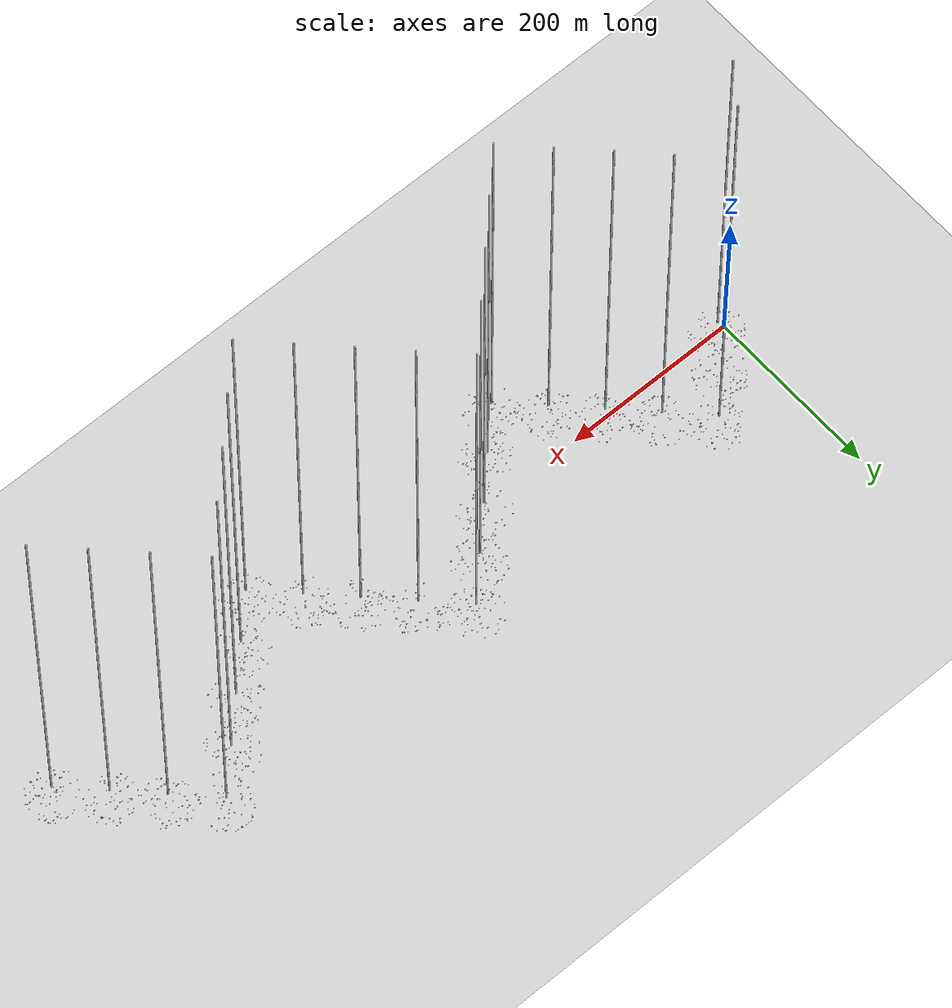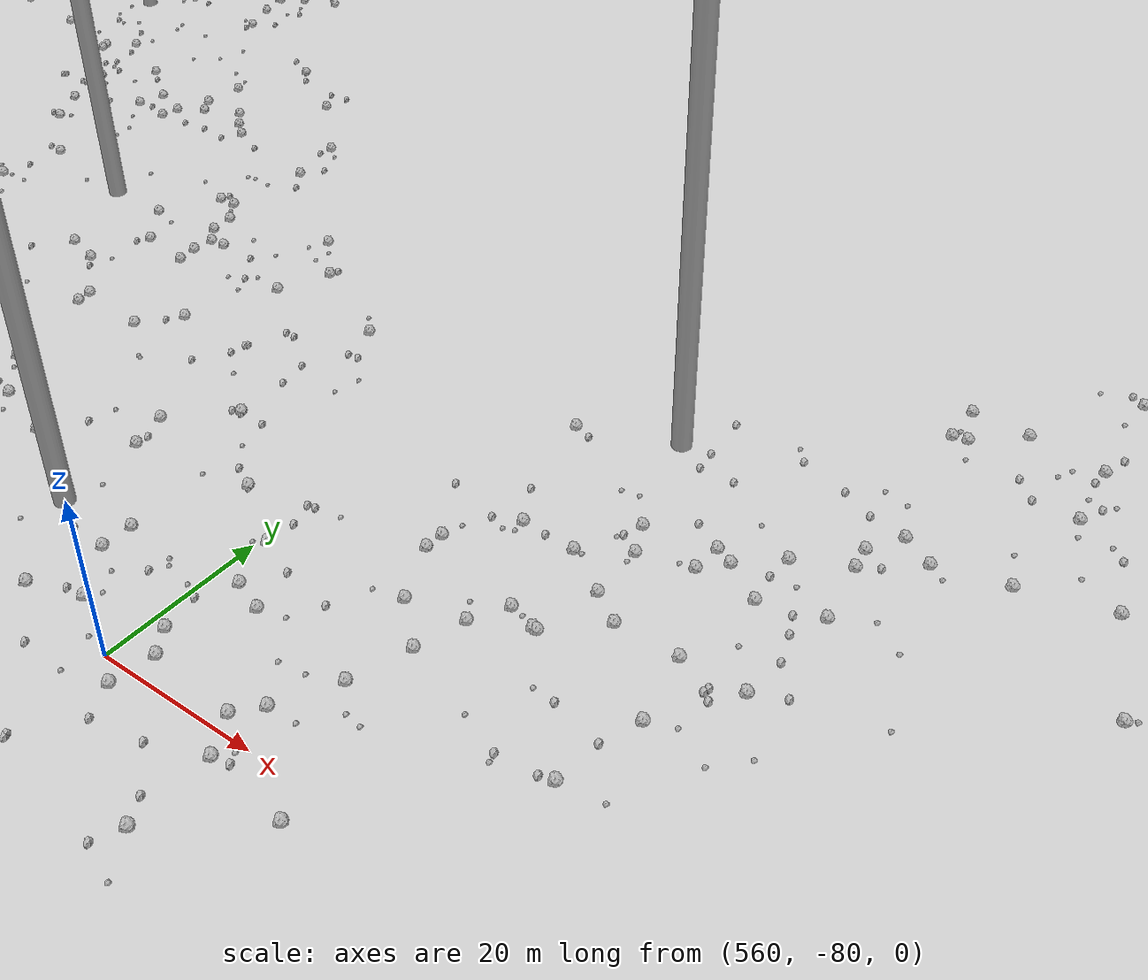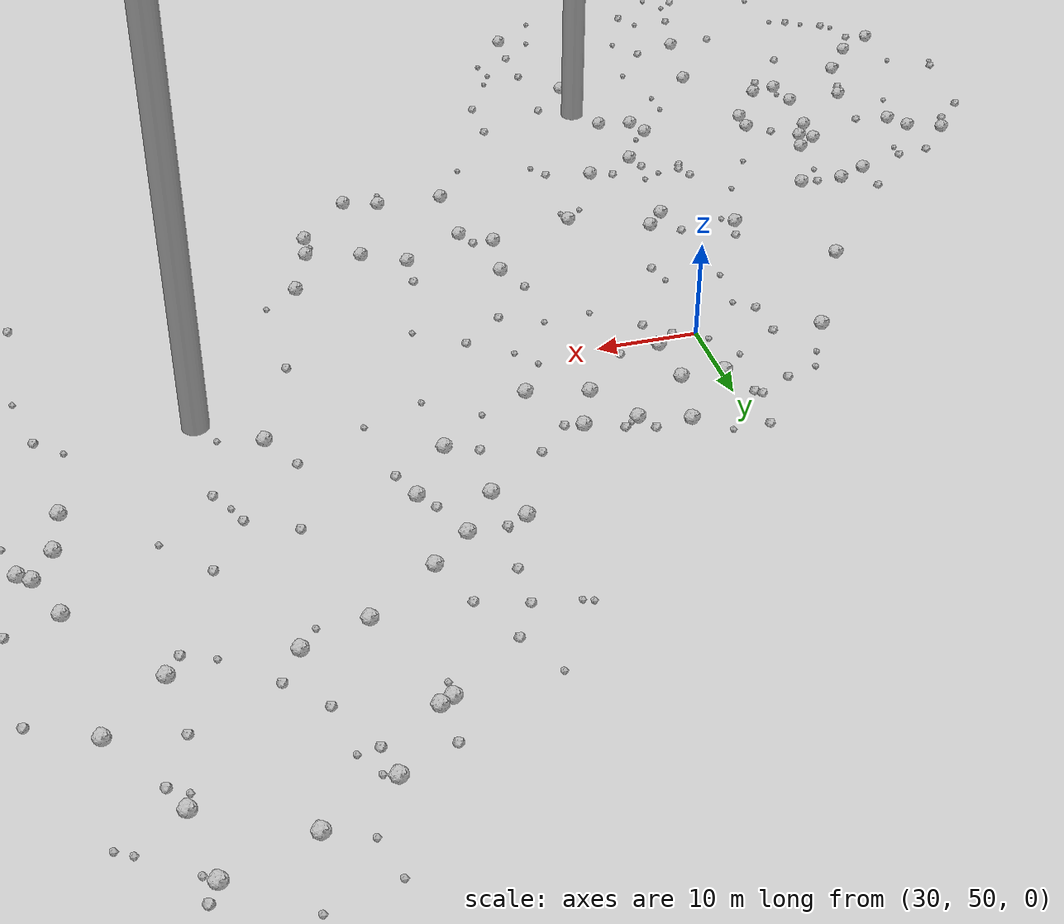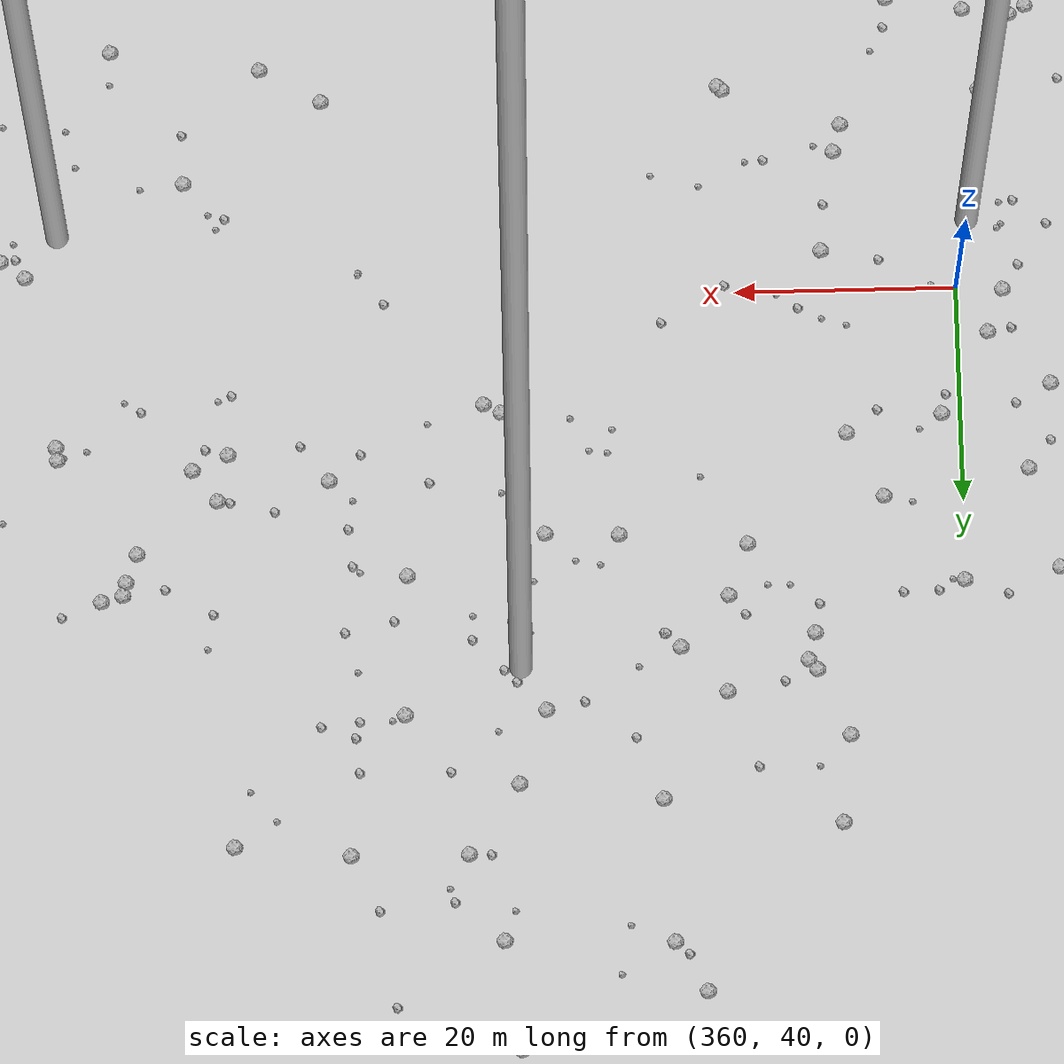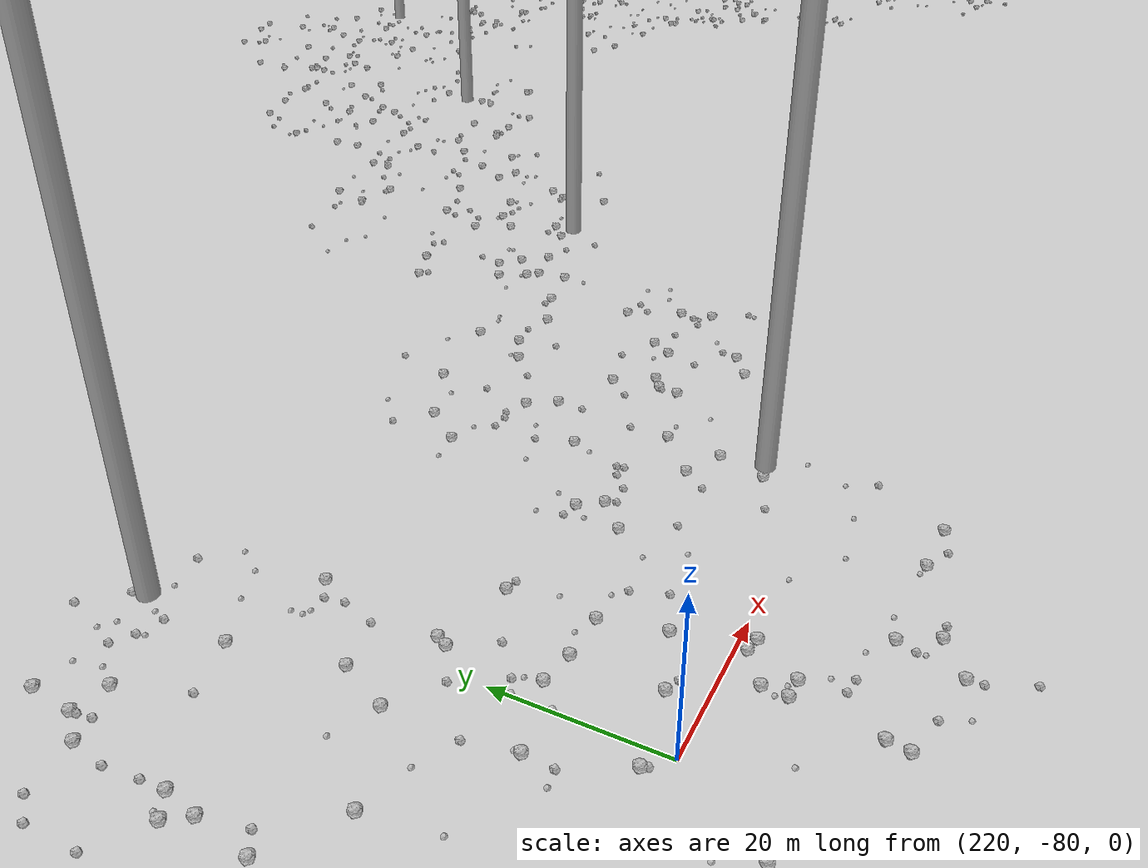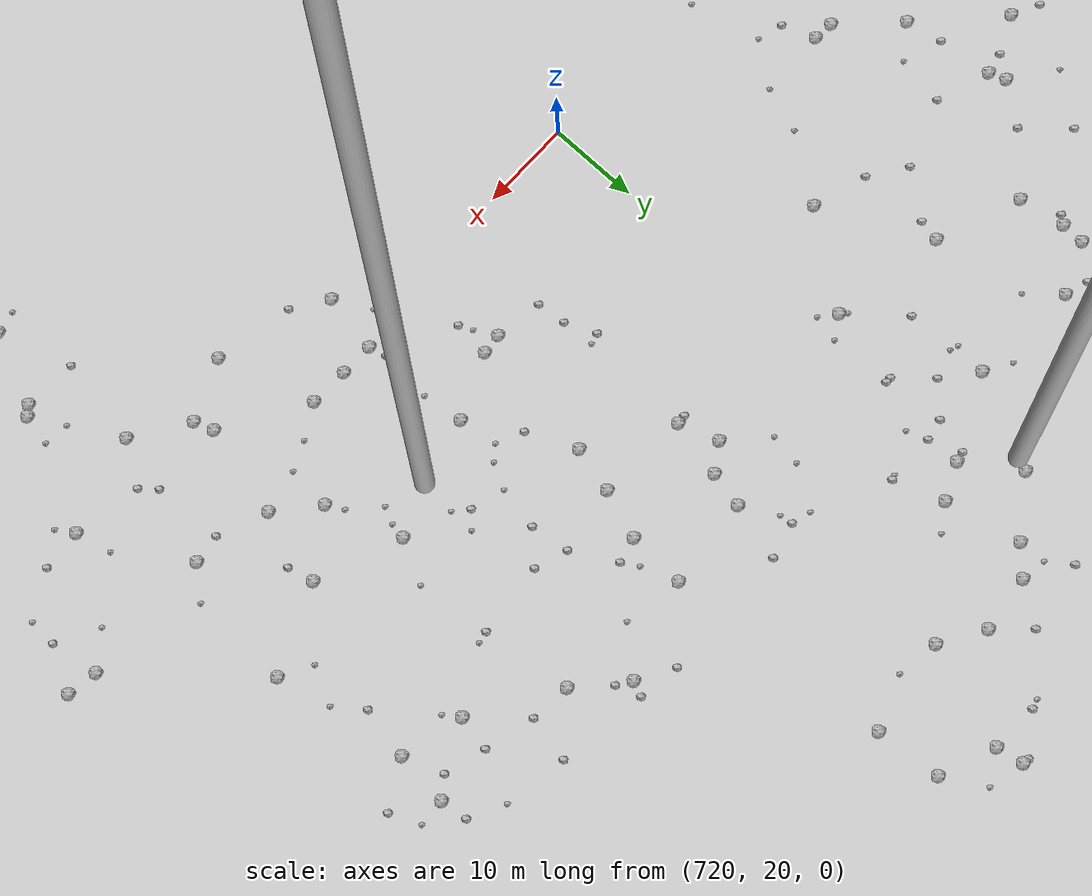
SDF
<sdf version="1.6">
 <world name="default">
  <include><uri>model://custom_ground</uri></include>
  <include><uri>model://sun</uri></include>
  <spherical_coordinates>
   <surface_model>EARTH_WGS84</surface_model>
   <latitude_deg>38.161479</latitude_deg>
   <longitude_deg>-122.454630</longitude_deg>
   <elevation>488.0</elevation>
   <heading_deg>90</heading_deg>
  </spherical_coordinates>
  <model name="rock1_0_0">
   <include><uri>model://rock1</uri><pose>4.436751652446244 14.410133604049683 0.5 0 0 0</pose></include>
  </model>
  <model name="rock1_0_1">
   <include><uri>model://rock1</uri><pose>5.451547144910947 2.469839490165114 0.5 0 0 0</pose></include>
  </model>
  <model name="rock1_0_2">
   <include><uri>model://rock1</uri><pose>2.039369760646231 5.7592562745307205 0.5 0 0 0</pose></include>
  </model>
  <model name="rock1_0_3">
   <include><uri>model://rock1</uri><pose>9.557093165146753 10.754722590684267 0.5 0 0 0</pose></include>
  </model>
  <model name="rock1_0_4">
   <include><uri>model://rock1</uri><pose>8.569090244645242 24.957271792820713 0.5 0 0 0</pose></include>
  </model>
  <model name="rock1_0_5">
   <include><uri>model://rock1</uri><pose>25.19521828155984 14.6509421780056 0.5 0 0 0</pose></include>
  </model>
  <model name="rock1_0_6">
   <include><uri>model://rock1</uri><pose>26.00777376279452 5.7297127285745475 0.5 0 0 0</pose></include>
  </model>
  <model name="rock1_0_7">
   <include><uri>model://rock1</uri><pose>31.463860327236787 -19.443692855537986 0.5 0 0 0</pose></include>
  </model>
  <model name="rock1_0_8">
   <include><uri>model://rock1</uri><pose>0.6382978725062607 23.617270814070388 0.5 0 0 0</pose></include>
  </model>
  <model name="rock1_0_9">
   <include><uri>model://rock1</uri><pose>10.536346866945493 -12.95001865185105 0.5 0 0 0</pose></include>
  </model>
  <model name="rock1_0_10">
   <include><uri>model://rock1</uri><pose>-4.279022639600774 5.637594169594088 0.5 0 0 0</pose></include>
  </model>
  <model name="rock1_0_11">
   <include><uri>model://rock1</uri><pose>-14.343713115884073 -8.70272914112805 0.5 0 0 0</pose></include>
  </model>
  <model name="rock1_0_12">
   <include><uri>model://rock1</uri><pose>27.721575073597094 -4.463547059237165 0.5 0 0 0</pose></include>
  </model>
  <model name="rock1_0_13">
   <include><uri>model://rock1</uri><pose>22.438288939993384 6.450325348294726 0.5 0 0 0</pose></include>
  </model>
  <model name="rock1_0_14">
   <include><uri>model://rock1</uri><pose>-7.236137591150193 13.148492995167722 0.5 0 0 0</pose></include>
  </model>
  <model name="rock1_0_15">
   <include><uri>model://rock1</uri><pose>2.885902249728421 12.0091837374911 0.5 0 0 0</pose></include>
  </model>
  <model name="rock1_0_16">
   <include><uri>model://rock1</uri><pose>21.46803192961429 8.91738948610972 0.5 0 0 0</pose></include>
  </model>
  <model name="rock1_0_17">
   <include><uri>model://rock1</uri><pose>-6.357542372282143 -1.035538021041745 0.5 0 0 0</pose></include>
  </model>
  <model name="rock1_0_18">
   <include><uri>model://rock1</uri><pose>5.3826426561761025 17.063228064147395 0.5 0 0 0</pose></include>
  </model>
  <model name="rock1_0_19">
   <include><uri>model://rock1</uri><pose>-8.72861266490964 15.36341996497363 0.5 0 0 0</pose></include>
  </model>
  <model name="rock1_0_20">
   <include><uri>model://rock1</uri><pose>-10.033470325011988 -5.906808238683137 0.5 0 0 0</pose></include>
  </model>
  <model name="rock1_0_21">
   <include><uri>model://rock1</uri><pose>-12.388801369145355 16.816526027362585 0.5 0 0 0</pose></include>
  </model>
  <model name="rock1_0_22">
   <include><uri>model://rock1</uri><pose>3.9101027697612807 25.140264195898574 0.5 0 0 0</pose></include>
  </model>
  <model name="rock1_0_23">
   <include><uri>model://rock1</uri><pose>12.328918532682806 -3.3340040170427656 0.5 0 0 0</pose></include>
  </model>
  <model name="rock1_0_24">
   <include><uri>model://rock1</uri><pose>9.43279041967963 8.16219149374615 0.5 0 0 0</pose></include>
  </model>
  <model name="rock1_0_25">
   <include><uri>model://rock1</uri><pose>2.623323046523879 1.973246205890856 0.5 0 0 0</pose></include>
  </model>
  <model name="rock1_0_26">
   <include><uri>model://rock1</uri><pose>3.171417202744557 15.427488481348696 0.5 0 0 0</pose></include>
  </model>
  <model name="rock2_0_0">
   <include><uri>model://rock2</uri><pose>-13.634742730561396 14.472386346274511 0.3 0 0 0</pose></include>
  </model>
  <model name="rock2_0_1">
   <include><uri>model://rock2</uri><pose>31.653937200328826 -9.170126971119533 0.3 0 0 0</pose></include>
  </model>
  <model name="rock2_0_2">
   <include><uri>model://rock2</uri><pose>-6.347682483316726 -15.843913862670231 0.3 0 0 0</pose></include>
  </model>
  <model name="rock2_0_3">
   <include><uri>model://rock2</uri><pose>8.65630246268983 -20.20341482343067 0.3 0 0 0</pose></include>
  </model>
  <model name="rock2_0_4">
   <include><uri>model://rock2</uri><pose>15.363129498251588 -11.614956824108297 0.3 0 0 0</pose></include>
  </model>
  <model name="rock2_0_5">
   <include><uri>model://rock2</uri><pose>7.143466866413238 12.54947653820561 0.3 0 0 0</pose></include>
  </model>
  <model name="rock2_0_6">
   <include><uri>model://rock2</uri><pose>-0.5718435208473309 -5.451358076295001 0.3 0 0 0</pose></include>
  </model>
  <model name="rock2_0_7">
   <include><uri>model://rock2</uri><pose>-5.185281208812116 3.516838969603711 0.3 0 0 0</pose></include>
  </model>
  <model name="rock2_0_8">
   <include><uri>model://rock2</uri><pose>31.73814003964086 -14.675738689536594 0.3 0 0 0</pose></include>
  </model>
  <model name="rock2_0_9">
   <include><uri>model://rock2</uri><pose>31.794104935138968 0.29893528324365803 0.3 0 0 0</pose></include>
  </model>
  <model name="rock2_0_10">
   <include><uri>model://rock2</uri><pose>-16.905817389030556 11.472546958792158 0.3 0 0 0</pose></include>
  </model>
  <model name="rock2_0_11">
   <include><uri>model://rock2</uri><pose>20.565086074945405 18.315427423596844 0.3 0 0 0</pose></include>
  </model>
  <model name="rock2_0_12">
   <include><uri>model://rock2</uri><pose>-12.075251224398277 -9.495229649303294 0.3 0 0 0</pose></include>
  </model>
  <model name="rock2_0_13">
   <include><uri>model://rock2</uri><pose>-10.33960697015848 -13.644311204722815 0.3 0 0 0</pose></include>
  </model>
  <model name="rock2_0_14">
   <include><uri>model://rock2</uri><pose>-8.354175974686374 21.242082714067053 0.3 0 0 0</pose></include>
  </model>
  <model name="rock2_0_15">
   <include><uri>model://rock2</uri><pose>6.093797600066097 -25.88805142847471 0.3 0 0 0</pose></include>
  </model>
  <model name="rock2_0_16">
   <include><uri>model://rock2</uri><pose>20.220278876345205 17.42255028748636 0.3 0 0 0</pose></include>
  </model>
  <model name="rock2_0_17">
   <include><uri>model://rock2</uri><pose>-3.709807445781159 12.240345106915825 0.3 0 0 0</pose></include>
  </model>
  <model name="rock2_0_18">
   <include><uri>model://rock2</uri><pose>5.397978634082719 -13.524539263917923 0.3 0 0 0</pose></include>
  </model>
  <model name="rock2_0_19">
   <include><uri>model://rock2</uri><pose>4.133253933275281 -0.04876332923991811 0.3 0 0 0</pose></include>
  </model>
  <model name="rock2_0_20">
   <include><uri>model://rock2</uri><pose>39.293594061914035 -1.9893136835711474 0.3 0 0 0</pose></include>
  </model>
  <model name="rock2_0_21">
   <include><uri>model://rock2</uri><pose>0.5238871929838034 27.586370560110552 0.3 0 0 0</pose></include>
  </model>
  <model name="rock2_0_22">
   <include><uri>model://rock2</uri><pose>-18.73554846529414 1.053708532696497 0.3 0 0 0</pose></include>
  </model>
  <model name="rock2_0_23">
   <include><uri>model://rock2</uri><pose>39.3551393578617 3.948600704092975 0.3 0 0 0</pose></include>
  </model>
  <model name="rock2_0_24">
   <include><uri>model://rock2</uri><pose>6.626157747977672 24.977075043020996 0.3 0 0 0</pose></include>
  </model>
  <model name="rock2_0_25">
   <include><uri>model://rock2</uri><pose>-4.801363539373693 21.651254442495862 0.3 0 0 0</pose></include>
  </model>
  <model name="rock2_0_26">
   <include><uri>model://rock2</uri><pose>14.33115412496587 -22.722570753375116 0.3 0 0 0</pose></include>
  </model>
  <model name="rock3_0_0">
   <include><uri>model://rock3</uri><pose>-9.11054216891653 8.23558673030226 0.2 0 0 0</pose></include>
  </model>
  <model name="rock3_0_1">
   <include><uri>model://rock3</uri><pose>26.446973227016002 -24.13894323538928 0.2 0 0 0</pose></include>
  </model>
  <model name="rock3_0_2">
   <include><uri>model://rock3</uri><pose>-19.321364664483006 -0.3095375663214952 0.2 0 0 0</pose></include>
  </model>
  <model name="rock3_0_3">
   <include><uri>model://rock3</uri><pose>35.18048044829002 -10.571178731496179 0.2 0 0 0</pose></include>
  </model>
  <model name="rock3_0_4">
   <include><uri>model://rock3</uri><pose>-5.114025809378489 19.71614674543607 0.2 0 0 0</pose></include>
  </model>
  <model name="rock3_0_5">
   <include><uri>model://rock3</uri><pose>36.500058359051614 13.800045555039574 0.2 0 0 0</pose></include>
  </model>
  <model name="rock3_0_6">
   <include><uri>model://rock3</uri><pose>19.052700948824345 -6.234025556087744 0.2 0 0 0</pose></include>
  </model>
  <model name="rock3_0_7">
   <include><uri>model://rock3</uri><pose>17.6508096533913 3.6043165236830745 0.2 0 0 0</pose></include>
  </model>
  <model name="rock3_0_8">
   <include><uri>model://rock3</uri><pose>28.030526483543667 -18.49327971322173 0.2 0 0 0</pose></include>
  </model>
  <model name="rock3_0_9">
   <include><uri>model://rock3</uri><pose>17.654369967737125 0.5694014930076783 0.2 0 0 0</pose></include>
  </model>
  <model name="rock3_0_10">
   <include><uri>model://rock3</uri><pose>-1.6099524395832496 -27.248615685026632 0.2 0 0 0</pose></include>
  </model>
  <model name="rock3_0_11">
   <include><uri>model://rock3</uri><pose>35.7051491535571 -13.334254256157926 0.2 0 0 0</pose></include>
  </model>
  <model name="rock3_0_12">
   <include><uri>model://rock3</uri><pose>-8.092463990774455 -14.904798996329323 0.2 0 0 0</pose></include>
  </model>
  <model name="rock3_0_13">
   <include><uri>model://rock3</uri><pose>7.715776517532721 -24.607271864287224 0.2 0 0 0</pose></include>
  </model>
  <model name="rock3_0_14">
   <include><uri>model://rock3</uri><pose>2.713054051190195 3.500746939879697 0.2 0 0 0</pose></include>
  </model>
  <model name="rock3_0_15">
   <include><uri>model://rock3</uri><pose>12.82192453483647 18.378750674593967 0.2 0 0 0</pose></include>
  </model>
  <model name="rock3_0_16">
   <include><uri>model://rock3</uri><pose>9.370090647910189 -27.358771356186104 0.2 0 0 0</pose></include>
  </model>
  <model name="rock3_0_17">
   <include><uri>model://rock3</uri><pose>-14.333968836641876 -1.8848237765501068 0.2 0 0 0</pose></include>
  </model>
  <model name="rock3_0_18">
   <include><uri>model://rock3</uri><pose>17.50422073058825 -15.199672178329994 0.2 0 0 0</pose></include>
  </model>
  <model name="rock3_0_19">
   <include><uri>model://rock3</uri><pose>22.84684874729996 10.247602838339063 0.2 0 0 0</pose></include>
  </model>
  <model name="rock3_0_20">
   <include><uri>model://rock3</uri><pose>-7.539325764918095 -1.9886127075443802 0.2 0 0 0</pose></include>
  </model>
  <model name="rock3_0_21">
   <include><uri>model://rock3</uri><pose>5.835340328893391 22.237956590256175 0.2 0 0 0</pose></include>
  </model>
  <model name="rock3_0_22">
   <include><uri>model://rock3</uri><pose>36.21177615292311 -8.407801575331419 0.2 0 0 0</pose></include>
  </model>
  <model name="rock3_0_23">
   <include><uri>model://rock3</uri><pose>12.824320649199421 -20.402517838318456 0.2 0 0 0</pose></include>
  </model>
  <model name="rock3_0_24">
   <include><uri>model://rock3</uri><pose>-11.414756648012725 -12.933639563641528 0.2 0 0 0</pose></include>
  </model>
  <model name="rock3_0_25">
   <include><uri>model://rock3</uri><pose>-3.8279852975055206 -23.850356004552122 0.2 0 0 0</pose></include>
  </model>
  <model name="rock3_0_26">
   <include><uri>model://rock3</uri><pose>-4.458951247758357 -16.691735190340733 0.2 0 0 0</pose></include>
  </model>
  <model name="rock1_1_0">
   <include><uri>model://rock1</uri><pose>35.35226705611649 63.366263872783684 0.5 0 0 0</pose></include>
  </model>
  <model name="rock1_1_1">
   <include><uri>model://rock1</uri><pose>34.33410074821334 51.31426052043197 0.5 0 0 0</pose></include>
  </model>
  <model name="rock1_1_2">
   <include><uri>model://rock1</uri><pose>11.040526913812068 39.93375453965089 0.5 0 0 0</pose></include>
  </model>
  <model name="rock1_1_3">
   <include><uri>model://rock1</uri><pose>35.85502473038304 26.138070472267696 0.5 0 0 0</pose></include>
  </model>
  <model name="rock1_1_4">
   <include><uri>model://rock1</uri><pose>58.652580372431736 27.567263423318195 0.5 0 0 0</pose></include>
  </model>
  <model name="rock1_1_5">
   <include><uri>model://rock1</uri><pose>17.850736915240326 52.00551823210896 0.5 0 0 0</pose></include>
  </model>
  <model name="rock1_1_6">
   <include><uri>model://rock1</uri><pose>18.82478537637347 31.151847618197934 0.5 0 0 0</pose></include>
  </model>
  <model name="rock1_1_7">
   <include><uri>model://rock1</uri><pose>29.793337751319484 56.9719007837706 0.5 0 0 0</pose></include>
  </model>
  <model name="rock1_1_8">
   <include><uri>model://rock1</uri><pose>47.873192952205265 26.07613853387615 0.5 0 0 0</pose></include>
  </model>
  <model name="rock1_1_9">
   <include><uri>model://rock1</uri><pose>45.06779856955539 61.77338214146704 0.5 0 0 0</pose></include>
  </model>
  <model name="rock1_1_10">
   <include><uri>model://rock1</uri><pose>63.773844637950795 22.814425301449226 0.5 0 0 0</pose></include>
  </model>
  <model name="rock1_1_11">
   <include><uri>model://rock1</uri><pose>64.16531753470674 25.998454509366262 0.5 0 0 0</pose></include>
  </model>
  <model name="rock1_1_12">
   <include><uri>model://rock1</uri><pose>57.93800835402343 61.68080919251646 0.5 0 0 0</pose></include>
  </model>
  <model name="rock1_1_13">
   <include><uri>model://rock1</uri><pose>44.73087617153403 28.33740137212147 0.5 0 0 0</pose></include>
  </model>
  <model name="rock1_1_14">
   <include><uri>model://rock1</uri><pose>54.83695796967483 17.56207439082767 0.5 0 0 0</pose></include>
  </model>
  <model name="rock1_1_15">
   <include><uri>model://rock1</uri><pose>34.06441289374615 56.92015399116325 0.5 0 0 0</pose></include>
  </model>
  <model name="rock1_1_16">
   <include><uri>model://rock1</uri><pose>48.78481882734022 55.52348889659765 0.5 0 0 0</pose></include>
  </model>
  <model name="rock1_1_17">
   <include><uri>model://rock1</uri><pose>27.78648949131352 29.567956740003613 0.5 0 0 0</pose></include>
  </model>
  <model name="rock1_1_18">
   <include><uri>model://rock1</uri><pose>58.43508670546542 16.46754034616588 0.5 0 0 0</pose></include>
  </model>
  <model name="rock1_1_19">
   <include><uri>model://rock1</uri><pose>42.99878138594659 56.92819320181205 0.5 0 0 0</pose></include>
  </model>
  <model name="rock1_1_20">
   <include><uri>model://rock1</uri><pose>47.91974347791146 17.81384298537709 0.5 0 0 0</pose></include>
  </model>
  <model name="rock1_1_21">
   <include><uri>model://rock1</uri><pose>45.49102833992404 34.2222469425093 0.5 0 0 0</pose></include>
  </model>
  <model name="rock1_1_22">
   <include><uri>model://rock1</uri><pose>54.26773646173177 29.93406019326808 0.5 0 0 0</pose></include>
  </model>
  <model name="rock1_1_23">
   <include><uri>model://rock1</uri><pose>66.26312277371755 32.407710245962114 0.5 0 0 0</pose></include>
  </model>
  <model name="rock1_1_24">
   <include><uri>model://rock1</uri><pose>25.87777928525658 27.342712556246003 0.5 0 0 0</pose></include>
  </model>
  <model name="rock1_1_25">
   <include><uri>model://rock1</uri><pose>39.99103924039842 61.92002169632717 0.5 0 0 0</pose></include>
  </model>
  <model name="rock1_1_26">
   <include><uri>model://rock1</uri><pose>30.584040695971265 17.0842232829454 0.5 0 0 0</pose></include>
  </model>
  <model name="rock2_1_0">
   <include><uri>model://rock2</uri><pose>19.639623460128508 33.66468745940208 0.3 0 0 0</pose></include>
  </model>
  <model name="rock2_1_1">
   <include><uri>model://rock2</uri><pose>54.942689587162256 62.81505836322408 0.3 0 0 0</pose></include>
  </model>
  <model name="rock2_1_2">
   <include><uri>model://rock2</uri><pose>22.721652525674738 51.67620701077952 0.3 0 0 0</pose></include>
  </model>
  <model name="rock2_1_3">
   <include><uri>model://rock2</uri><pose>27.63203117090805 61.23768738987141 0.3 0 0 0</pose></include>
  </model>
  <model name="rock2_1_4">
   <include><uri>model://rock2</uri><pose>30.399540104107984 37.755225842191884 0.3 0 0 0</pose></include>
  </model>
  <model name="rock2_1_5">
   <include><uri>model://rock2</uri><pose>49.73843507038578 64.53310820307176 0.3 0 0 0</pose></include>
  </model>
  <model name="rock2_1_6">
   <include><uri>model://rock2</uri><pose>32.390841973182276 49.65692866723613 0.3 0 0 0</pose></include>
  </model>
  <model name="rock2_1_7">
   <include><uri>model://rock2</uri><pose>46.72297352501251 61.32135787598135 0.3 0 0 0</pose></include>
  </model>
  <model name="rock2_1_8">
   <include><uri>model://rock2</uri><pose>34.69061566462636 47.55248749936148 0.3 0 0 0</pose></include>
  </model>
  <model name="rock2_1_9">
   <include><uri>model://rock2</uri><pose>38.82846529703201 63.68272093739675 0.3 0 0 0</pose></include>
  </model>
  <model name="rock2_1_10">
   <include><uri>model://rock2</uri><pose>28.231097243819 60.72452946565971 0.3 0 0 0</pose></include>
  </model>
  <model name="rock2_1_11">
   <include><uri>model://rock2</uri><pose>24.363271532639523 59.40888718556212 0.3 0 0 0</pose></include>
  </model>
  <model name="rock2_1_12">
   <include><uri>model://rock2</uri><pose>28.092398577836647 17.640125700391394 0.3 0 0 0</pose></include>
  </model>
  <model name="rock2_1_13">
   <include><uri>model://rock2</uri><pose>47.88728800284326 42.57843783026332 0.3 0 0 0</pose></include>
  </model>
  <model name="rock2_1_14">
   <include><uri>model://rock2</uri><pose>24.380260779630518 16.65807206638962 0.3 0 0 0</pose></include>
  </model>
  <model name="rock2_1_15">
   <include><uri>model://rock2</uri><pose>38.35679621158805 51.78356765615451 0.3 0 0 0</pose></include>
  </model>
  <model name="rock2_1_16">
   <include><uri>model://rock2</uri><pose>41.48959058078508 62.95981888103555 0.3 0 0 0</pose></include>
  </model>
  <model name="rock2_1_17">
   <include><uri>model://rock2</uri><pose>19.819314226440913 19.950204203441054 0.3 0 0 0</pose></include>
  </model>
  <model name="rock2_1_18">
   <include><uri>model://rock2</uri><pose>43.88586534422056 37.7497822041003 0.3 0 0 0</pose></include>
  </model>
  <model name="rock2_1_19">
   <include><uri>model://rock2</uri><pose>52.02227738336423 46.11572159094917 0.3 0 0 0</pose></include>
  </model>
  <model name="rock2_1_20">
   <include><uri>model://rock2</uri><pose>28.718467970193608 65.78945473158562 0.3 0 0 0</pose></include>
  </model>
  <model name="rock2_1_21">
   <include><uri>model://rock2</uri><pose>54.46190598931455 33.90167432577273 0.3 0 0 0</pose></include>
  </model>
  <model name="rock2_1_22">
   <include><uri>model://rock2</uri><pose>24.848225253325083 31.27865705303754 0.3 0 0 0</pose></include>
  </model>
  <model name="rock2_1_23">
   <include><uri>model://rock2</uri><pose>46.81404382920569 28.084853156425748 0.3 0 0 0</pose></include>
  </model>
  <model name="rock2_1_24">
   <include><uri>model://rock2</uri><pose>69.38613428165283 45.806255072355654 0.3 0 0 0</pose></include>
  </model>
  <model name="rock2_1_25">
   <include><uri>model://rock2</uri><pose>22.857727350571942 47.4654667920823 0.3 0 0 0</pose></include>
  </model>
  <model name="rock2_1_26">
   <include><uri>model://rock2</uri><pose>35.33658894306298 15.797592549688158 0.3 0 0 0</pose></include>
  </model>
  <model name="rock3_1_0">
   <include><uri>model://rock3</uri><pose>58.29038868949814 54.35806506458478 0.2 0 0 0</pose></include>
  </model>
  <model name="rock3_1_1">
   <include><uri>model://rock3</uri><pose>46.22618516965944 51.12256619416149 0.2 0 0 0</pose></include>
  </model>
  <model name="rock3_1_2">
   <include><uri>model://rock3</uri><pose>24.008704855654983 40.64866561128684 0.2 0 0 0</pose></include>
  </model>
  <model name="rock3_1_3">
   <include><uri>model://rock3</uri><pose>69.56884553977841 35.01492249007375 0.2 0 0 0</pose></include>
  </model>
  <model name="rock3_1_4">
   <include><uri>model://rock3</uri><pose>19.812576583938977 29.94885353498601 0.2 0 0 0</pose></include>
  </model>
  <model name="rock3_1_5">
   <include><uri>model://rock3</uri><pose>40.65561853189389 62.22648745540667 0.2 0 0 0</pose></include>
  </model>
  <model name="rock3_1_6">
   <include><uri>model://rock3</uri><pose>24.851925332978205 19.443814746583485 0.2 0 0 0</pose></include>
  </model>
  <model name="rock3_1_7">
   <include><uri>model://rock3</uri><pose>27.275267618030853 54.59406550599174 0.2 0 0 0</pose></include>
  </model>
  <model name="rock3_1_8">
   <include><uri>model://rock3</uri><pose>32.164784712455955 65.6989458149107 0.2 0 0 0</pose></include>
  </model>
  <model name="rock3_1_9">
   <include><uri>model://rock3</uri><pose>16.348740907183398 23.968750093182578 0.2 0 0 0</pose></include>
  </model>
  <model name="rock3_1_10">
   <include><uri>model://rock3</uri><pose>33.937269383281176 24.122071323490477 0.2 0 0 0</pose></include>
  </model>
  <model name="rock3_1_11">
   <include><uri>model://rock3</uri><pose>22.974716869211704 18.49091217865772 0.2 0 0 0</pose></include>
  </model>
  <model name="rock3_1_12">
   <include><uri>model://rock3</uri><pose>43.69080451780156 44.376907529265715 0.2 0 0 0</pose></include>
  </model>
  <model name="rock3_1_13">
   <include><uri>model://rock3</uri><pose>54.38605634345221 15.381638333309152 0.2 0 0 0</pose></include>
  </model>
  <model name="rock3_1_14">
   <include><uri>model://rock3</uri><pose>20.027208858538437 56.070950831732375 0.2 0 0 0</pose></include>
  </model>
  <model name="rock3_1_15">
   <include><uri>model://rock3</uri><pose>38.96380562317545 43.95884279709874 0.2 0 0 0</pose></include>
  </model>
  <model name="rock3_1_16">
   <include><uri>model://rock3</uri><pose>63.40866948500841 24.434250124448603 0.2 0 0 0</pose></include>
  </model>
  <model name="rock3_1_17">
   <include><uri>model://rock3</uri><pose>24.630472653320496 45.86123469130718 0.2 0 0 0</pose></include>
  </model>
  <model name="rock3_1_18">
   <include><uri>model://rock3</uri><pose>21.10333630585101 58.3523780832859 0.2 0 0 0</pose></include>
  </model>
  <model name="rock3_1_19">
   <include><uri>model://rock3</uri><pose>29.185021922294997 51.29995033596118 0.2 0 0 0</pose></include>
  </model>
  <model name="rock3_1_20">
   <include><uri>model://rock3</uri><pose>53.40409341266511 57.66883285771955 0.2 0 0 0</pose></include>
  </model>
  <model name="rock3_1_21">
   <include><uri>model://rock3</uri><pose>29.69871061271476 40.13714681150278 0.2 0 0 0</pose></include>
  </model>
  <model name="rock3_1_22">
   <include><uri>model://rock3</uri><pose>47.95284022922493 48.87278711002959 0.2 0 0 0</pose></include>
  </model>
  <model name="rock3_1_23">
   <include><uri>model://rock3</uri><pose>36.12059416949305 24.4702485338467 0.2 0 0 0</pose></include>
  </model>
  <model name="rock3_1_24">
   <include><uri>model://rock3</uri><pose>56.587547041407895 42.90317347643065 0.2 0 0 0</pose></include>
  </model>
  <model name="rock3_1_25">
   <include><uri>model://rock3</uri><pose>66.30735284575591 32.49421323842624 0.2 0 0 0</pose></include>
  </model>
  <model name="rock3_1_26">
   <include><uri>model://rock3</uri><pose>44.56844234879892 12.194622428991252 0.2 0 0 0</pose></include>
  </model>
  <model name="rock1_2_0">
   <include><uri>model://rock1</uri><pose>103.38072470240624 69.73197908518549 0.5 0 0 0</pose></include>
  </model>
  <model name="rock1_2_1">
   <include><uri>model://rock1</uri><pose>100.77951804324888 97.495819674693 0.5 0 0 0</pose></include>
  </model>
  <model name="rock1_2_2">
   <include><uri>model://rock1</uri><pose>55.54250988487458 68.96553598297328 0.5 0 0 0</pose></include>
  </model>
  <model name="rock1_2_3">
   <include><uri>model://rock1</uri><pose>61.743527646908305 67.69497679129476 0.5 0 0 0</pose></include>
  </model>
  <model name="rock1_2_4">
   <include><uri>model://rock1</uri><pose>98.31245794782247 90.98682103461269 0.5 0 0 0</pose></include>
  </model>
  <model name="rock1_2_5">
   <include><uri>model://rock1</uri><pose>74.49584590706559 83.65994267751907 0.5 0 0 0</pose></include>
  </model>
  <model name="rock1_2_6">
   <include><uri>model://rock1</uri><pose>65.48547385361006 92.18668036324206 0.5 0 0 0</pose></include>
  </model>
  <model name="rock1_2_7">
   <include><uri>model://rock1</uri><pose>69.90171100438592 98.15988816933037 0.5 0 0 0</pose></include>
  </model>
  <model name="rock1_2_8">
   <include><uri>model://rock1</uri><pose>105.37235218430058 79.28615749442149 0.5 0 0 0</pose></include>
  </model>
  <model name="rock1_2_9">
   <include><uri>model://rock1</uri><pose>73.09793981036334 56.52187425320696 0.5 0 0 0</pose></include>
  </model>
  <model name="rock1_2_10">
   <include><uri>model://rock1</uri><pose>83.43934427655776 104.06074234394265 0.5 0 0 0</pose></include>
  </model>
  <model name="rock1_2_11">
   <include><uri>model://rock1</uri><pose>64.36818598585663 91.58558924061968 0.5 0 0 0</pose></include>
  </model>
  <model name="rock1_2_12">
   <include><uri>model://rock1</uri><pose>91.94539231899077 74.87519709364608 0.5 0 0 0</pose></include>
  </model>
  <model name="rock1_2_13">
   <include><uri>model://rock1</uri><pose>100.90289989955053 60.22443014672055 0.5 0 0 0</pose></include>
  </model>
  <model name="rock1_2_14">
   <include><uri>model://rock1</uri><pose>76.10732315310166 101.70029913460728 0.5 0 0 0</pose></include>
  </model>
  <model name="rock1_2_15">
   <include><uri>model://rock1</uri><pose>84.69291979778376 97.3644364863074 0.5 0 0 0</pose></include>
  </model>
  <model name="rock1_2_16">
   <include><uri>model://rock1</uri><pose>68.65987000610053 81.66739023446209 0.5 0 0 0</pose></include>
  </model>
  <model name="rock1_2_17">
   <include><uri>model://rock1</uri><pose>62.316023083064444 76.83257253431364 0.5 0 0 0</pose></include>
  </model>
  <model name="rock1_2_18">
   <include><uri>model://rock1</uri><pose>58.76852782016552 73.55637236270226 0.5 0 0 0</pose></include>
  </model>
  <model name="rock1_2_19">
   <include><uri>model://rock1</uri><pose>89.88984507058925 89.02915951180483 0.5 0 0 0</pose></include>
  </model>
  <model name="rock1_2_20">
   <include><uri>model://rock1</uri><pose>95.08826524968562 69.33740827053019 0.5 0 0 0</pose></include>
  </model>
  <model name="rock1_2_21">
   <include><uri>model://rock1</uri><pose>92.09518381543309 66.95516229079614 0.5 0 0 0</pose></include>
  </model>
  <model name="rock1_2_22">
   <include><uri>model://rock1</uri><pose>53.42755477261012 72.71047345358619 0.5 0 0 0</pose></include>
  </model>
  <model name="rock1_2_23">
   <include><uri>model://rock1</uri><pose>78.75262734058431 52.82476245915853 0.5 0 0 0</pose></include>
  </model>
  <model name="rock1_2_24">
   <include><uri>model://rock1</uri><pose>93.93666845653055 70.22475187735401 0.5 0 0 0</pose></include>
  </model>
  <model name="rock1_2_25">
   <include><uri>model://rock1</uri><pose>91.36126323938916 62.23342514699495 0.5 0 0 0</pose></include>
  </model>
  <model name="rock1_2_26">
   <include><uri>model://rock1</uri><pose>84.71380044514274 83.86517031409534 0.5 0 0 0</pose></include>
  </model>
  <model name="rock2_2_0">
   <include><uri>model://rock2</uri><pose>55.892676129977026 78.91876358034858 0.3 0 0 0</pose></include>
  </model>
  <model name="rock2_2_1">
   <include><uri>model://rock2</uri><pose>95.34836716929505 86.43303497027827 0.3 0 0 0</pose></include>
  </model>
  <model name="rock2_2_2">
   <include><uri>model://rock2</uri><pose>72.01288276337219 69.43292520214912 0.3 0 0 0</pose></include>
  </model>
  <model name="rock2_2_3">
   <include><uri>model://rock2</uri><pose>83.45083323791417 81.84209744625561 0.3 0 0 0</pose></include>
  </model>
  <model name="rock2_2_4">
   <include><uri>model://rock2</uri><pose>76.46760815947962 67.09061969381887 0.3 0 0 0</pose></include>
  </model>
  <model name="rock2_2_5">
   <include><uri>model://rock2</uri><pose>57.89486048243197 86.7048850243938 0.3 0 0 0</pose></include>
  </model>
  <model name="rock2_2_6">
   <include><uri>model://rock2</uri><pose>76.38096355496191 86.80286224410052 0.3 0 0 0</pose></include>
  </model>
  <model name="rock2_2_7">
   <include><uri>model://rock2</uri><pose>104.97725351036672 90.34259690105901 0.3 0 0 0</pose></include>
  </model>
  <model name="rock2_2_8">
   <include><uri>model://rock2</uri><pose>90.44296654467637 106.9779536532637 0.3 0 0 0</pose></include>
  </model>
  <model name="rock2_2_9">
   <include><uri>model://rock2</uri><pose>70.56968162807554 95.0466713603749 0.3 0 0 0</pose></include>
  </model>
  <model name="rock2_2_10">
   <include><uri>model://rock2</uri><pose>55.962212506552234 83.13617761309916 0.3 0 0 0</pose></include>
  </model>
  <model name="rock2_2_11">
   <include><uri>model://rock2</uri><pose>65.06286007118234 96.10038328924821 0.3 0 0 0</pose></include>
  </model>
  <model name="rock2_2_12">
   <include><uri>model://rock2</uri><pose>108.24139906264332 71.58928689867649 0.3 0 0 0</pose></include>
  </model>
  <model name="rock2_2_13">
   <include><uri>model://rock2</uri><pose>97.93365589639397 74.10129285128431 0.3 0 0 0</pose></include>
  </model>
  <model name="rock2_2_14">
   <include><uri>model://rock2</uri><pose>73.27742538305073 90.12996601643971 0.3 0 0 0</pose></include>
  </model>
  <model name="rock2_2_15">
   <include><uri>model://rock2</uri><pose>70.80644753936659 60.58841235011292 0.3 0 0 0</pose></include>
  </model>
  <model name="rock2_2_16">
   <include><uri>model://rock2</uri><pose>60.43604939834087 69.53730141084517 0.3 0 0 0</pose></include>
  </model>
  <model name="rock2_2_17">
   <include><uri>model://rock2</uri><pose>78.52138417840375 63.11076652978222 0.3 0 0 0</pose></include>
  </model>
  <model name="rock2_2_18">
   <include><uri>model://rock2</uri><pose>84.27983091929522 105.69283335637823 0.3 0 0 0</pose></include>
  </model>
  <model name="rock2_2_19">
   <include><uri>model://rock2</uri><pose>96.4035092968174 76.35233082201219 0.3 0 0 0</pose></include>
  </model>
  <model name="rock2_2_20">
   <include><uri>model://rock2</uri><pose>62.8990179117492 64.52513015747822 0.3 0 0 0</pose></include>
  </model>
  <model name="rock2_2_21">
   <include><uri>model://rock2</uri><pose>79.71467562583398 72.74133520712282 0.3 0 0 0</pose></include>
  </model>
  <model name="rock2_2_22">
   <include><uri>model://rock2</uri><pose>55.28309531776444 73.52143159546502 0.3 0 0 0</pose></include>
  </model>
  <model name="rock2_2_23">
   <include><uri>model://rock2</uri><pose>60.345246517029985 81.82501614030315 0.3 0 0 0</pose></include>
  </model>
  <model name="rock2_2_24">
   <include><uri>model://rock2</uri><pose>98.9657906712467 57.54977941660578 0.3 0 0 0</pose></include>
  </model>
  <model name="rock2_2_25">
   <include><uri>model://rock2</uri><pose>83.822373588327 90.17967127581424 0.3 0 0 0</pose></include>
  </model>
  <model name="rock2_2_26">
   <include><uri>model://rock2</uri><pose>85.89247693905283 94.88676356006033 0.3 0 0 0</pose></include>
  </model>
  <model name="rock3_2_0">
   <include><uri>model://rock3</uri><pose>77.201033227575 65.11981741506894 0.2 0 0 0</pose></include>
  </model>
  <model name="rock3_2_1">
   <include><uri>model://rock3</uri><pose>51.864976228033754 83.7287837302168 0.2 0 0 0</pose></include>
  </model>
  <model name="rock3_2_2">
   <include><uri>model://rock3</uri><pose>84.35933988222526 103.17234399075573 0.2 0 0 0</pose></include>
  </model>
  <model name="rock3_2_3">
   <include><uri>model://rock3</uri><pose>71.38624976430152 106.88885649220609 0.2 0 0 0</pose></include>
  </model>
  <model name="rock3_2_4">
   <include><uri>model://rock3</uri><pose>88.61210286225852 100.29187140995427 0.2 0 0 0</pose></include>
  </model>
  <model name="rock3_2_5">
   <include><uri>model://rock3</uri><pose>77.15926193788928 108.35823382013425 0.2 0 0 0</pose></include>
  </model>
  <model name="rock3_2_6">
   <include><uri>model://rock3</uri><pose>104.79447161470802 93.71111683403447 0.2 0 0 0</pose></include>
  </model>
  <model name="rock3_2_7">
   <include><uri>model://rock3</uri><pose>80.696725154969 82.87070797911852 0.2 0 0 0</pose></include>
  </model>
  <model name="rock3_2_8">
   <include><uri>model://rock3</uri><pose>104.98603745536715 75.10321414122876 0.2 0 0 0</pose></include>
  </model>
  <model name="rock3_2_9">
   <include><uri>model://rock3</uri><pose>96.15907668868385 65.47251446861482 0.2 0 0 0</pose></include>
  </model>
  <model name="rock3_2_10">
   <include><uri>model://rock3</uri><pose>99.95071840922523 61.84927248238126 0.2 0 0 0</pose></include>
  </model>
  <model name="rock3_2_11">
   <include><uri>model://rock3</uri><pose>77.14454712241422 55.33611422944794 0.2 0 0 0</pose></include>
  </model>
  <model name="rock3_2_12">
   <include><uri>model://rock3</uri><pose>72.3193962195806 95.22892316682103 0.2 0 0 0</pose></include>
  </model>
  <model name="rock3_2_13">
   <include><uri>model://rock3</uri><pose>64.28757299838801 89.87515606779743 0.2 0 0 0</pose></include>
  </model>
  <model name="rock3_2_14">
   <include><uri>model://rock3</uri><pose>103.44827124860615 83.77836364587637 0.2 0 0 0</pose></include>
  </model>
  <model name="rock3_2_15">
   <include><uri>model://rock3</uri><pose>89.92056053726594 99.54383218780427 0.2 0 0 0</pose></include>
  </model>
  <model name="rock3_2_16">
   <include><uri>model://rock3</uri><pose>72.4636759770373 103.01521444287985 0.2 0 0 0</pose></include>
  </model>
  <model name="rock3_2_17">
   <include><uri>model://rock3</uri><pose>64.1187382403562 56.75221344601047 0.2 0 0 0</pose></include>
  </model>
  <model name="rock3_2_18">
   <include><uri>model://rock3</uri><pose>70.91687865486495 97.53687018101232 0.2 0 0 0</pose></include>
  </model>
  <model name="rock3_2_19">
   <include><uri>model://rock3</uri><pose>50.99040456424427 84.05469456904599 0.2 0 0 0</pose></include>
  </model>
  <model name="rock3_2_20">
   <include><uri>model://rock3</uri><pose>55.216099914649305 73.79301550979565 0.2 0 0 0</pose></include>
  </model>
  <model name="rock3_2_21">
   <include><uri>model://rock3</uri><pose>55.530834503506654 90.97196609892438 0.2 0 0 0</pose></include>
  </model>
  <model name="rock3_2_22">
   <include><uri>model://rock3</uri><pose>103.6146112835959 67.90766895068037 0.2 0 0 0</pose></include>
  </model>
  <model name="rock3_2_23">
   <include><uri>model://rock3</uri><pose>83.61340849498693 68.26167777748641 0.2 0 0 0</pose></include>
  </model>
  <model name="rock3_2_24">
   <include><uri>model://rock3</uri><pose>72.86277373527903 81.50150476729954 0.2 0 0 0</pose></include>
  </model>
  <model name="rock3_2_25">
   <include><uri>model://rock3</uri><pose>90.39050621180246 53.59805291627086 0.2 0 0 0</pose></include>
  </model>
  <model name="rock3_2_26">
   <include><uri>model://rock3</uri><pose>84.28548153334026 95.71418043147949 0.2 0 0 0</pose></include>
  </model>
  <model name="rock1_3_0">
   <include><uri>model://rock1</uri><pose>128.63809362182465 19.73973503342829 0.5 0 0 0</pose></include>
  </model>
  <model name="rock1_3_1">
   <include><uri>model://rock1</uri><pose>135.22903435148652 26.15929347804757 0.5 0 0 0</pose></include>
  </model>
  <model name="rock1_3_2">
   <include><uri>model://rock1</uri><pose>122.59320222063488 28.69451085073676 0.5 0 0 0</pose></include>
  </model>
  <model name="rock1_3_3">
   <include><uri>model://rock1</uri><pose>106.80771526044722 13.338993649264149 0.5 0 0 0</pose></include>
  </model>
  <model name="rock1_3_4">
   <include><uri>model://rock1</uri><pose>120.22731489649851 25.191537470185377 0.5 0 0 0</pose></include>
  </model>
  <model name="rock1_3_5">
   <include><uri>model://rock1</uri><pose>96.34015401896843 23.83532306193267 0.5 0 0 0</pose></include>
  </model>
  <model name="rock1_3_6">
   <include><uri>model://rock1</uri><pose>119.83150362719933 11.438225670037404 0.5 0 0 0</pose></include>
  </model>
  <model name="rock1_3_7">
   <include><uri>model://rock1</uri><pose>143.44526995165145 23.748227029572824 0.5 0 0 0</pose></include>
  </model>
  <model name="rock1_3_8">
   <include><uri>model://rock1</uri><pose>144.68611362950972 49.934446841684185 0.5 0 0 0</pose></include>
  </model>
  <model name="rock1_3_9">
   <include><uri>model://rock1</uri><pose>135.83795643910258 43.941245769251594 0.5 0 0 0</pose></include>
  </model>
  <model name="rock1_3_10">
   <include><uri>model://rock1</uri><pose>141.06231886649286 29.39413557592038 0.5 0 0 0</pose></include>
  </model>
  <model name="rock1_3_11">
   <include><uri>model://rock1</uri><pose>141.32784699587063 55.88979560390356 0.5 0 0 0</pose></include>
  </model>
  <model name="rock1_3_12">
   <include><uri>model://rock1</uri><pose>114.06627413826003 28.447702246448564 0.5 0 0 0</pose></include>
  </model>
  <model name="rock1_3_13">
   <include><uri>model://rock1</uri><pose>140.98487588112735 35.004313457051225 0.5 0 0 0</pose></include>
  </model>
  <model name="rock1_3_14">
   <include><uri>model://rock1</uri><pose>101.38503598381867 18.98959766966766 0.5 0 0 0</pose></include>
  </model>
  <model name="rock1_3_15">
   <include><uri>model://rock1</uri><pose>120.49545190944175 29.62674805113041 0.5 0 0 0</pose></include>
  </model>
  <model name="rock1_3_16">
   <include><uri>model://rock1</uri><pose>109.56664788882165 33.38514665922506 0.5 0 0 0</pose></include>
  </model>
  <model name="rock1_3_17">
   <include><uri>model://rock1</uri><pose>101.39246359043041 50.75727152896221 0.5 0 0 0</pose></include>
  </model>
  <model name="rock1_3_18">
   <include><uri>model://rock1</uri><pose>142.0254736342373 28.048515491259284 0.5 0 0 0</pose></include>
  </model>
  <model name="rock1_3_19">
   <include><uri>model://rock1</uri><pose>112.8809295953227 13.805248425604141 0.5 0 0 0</pose></include>
  </model>
  <model name="rock1_3_20">
   <include><uri>model://rock1</uri><pose>133.14909505662877 63.820865843815554 0.5 0 0 0</pose></include>
  </model>
  <model name="rock1_3_21">
   <include><uri>model://rock1</uri><pose>129.01982041315955 14.764159544643311 0.5 0 0 0</pose></include>
  </model>
  <model name="rock1_3_22">
   <include><uri>model://rock1</uri><pose>110.59705560597666 62.2550542965088 0.5 0 0 0</pose></include>
  </model>
  <model name="rock1_3_23">
   <include><uri>model://rock1</uri><pose>109.29198866910323 14.1599046882213 0.5 0 0 0</pose></include>
  </model>
  <model name="rock1_3_24">
   <include><uri>model://rock1</uri><pose>119.7994503786694 25.1031778089836 0.5 0 0 0</pose></include>
  </model>
  <model name="rock1_3_25">
   <include><uri>model://rock1</uri><pose>113.15906720064893 59.963144721821145 0.5 0 0 0</pose></include>
  </model>
  <model name="rock1_3_26">
   <include><uri>model://rock1</uri><pose>106.32925481814476 14.200692477545175 0.5 0 0 0</pose></include>
  </model>
  <model name="rock2_3_0">
   <include><uri>model://rock2</uri><pose>101.96737905631142 45.228331689545186 0.3 0 0 0</pose></include>
  </model>
  <model name="rock2_3_1">
   <include><uri>model://rock2</uri><pose>96.60295771863876 32.218993129693956 0.3 0 0 0</pose></include>
  </model>
  <model name="rock2_3_2">
   <include><uri>model://rock2</uri><pose>128.71906191390724 52.229908060466634 0.3 0 0 0</pose></include>
  </model>
  <model name="rock2_3_3">
   <include><uri>model://rock2</uri><pose>139.07198219555514 50.88192764691606 0.3 0 0 0</pose></include>
  </model>
  <model name="rock2_3_4">
   <include><uri>model://rock2</uri><pose>111.05303962065688 43.67528541048941 0.3 0 0 0</pose></include>
  </model>
  <model name="rock2_3_5">
   <include><uri>model://rock2</uri><pose>92.93559816359073 51.54185799751414 0.3 0 0 0</pose></include>
  </model>
  <model name="rock2_3_6">
   <include><uri>model://rock2</uri><pose>101.10812868263326 40.01913054979717 0.3 0 0 0</pose></include>
  </model>
  <model name="rock2_3_7">
   <include><uri>model://rock2</uri><pose>112.31278921665653 41.41092278658056 0.3 0 0 0</pose></include>
  </model>
  <model name="rock2_3_8">
   <include><uri>model://rock2</uri><pose>121.32105130573491 62.15423557057232 0.3 0 0 0</pose></include>
  </model>
  <model name="rock2_3_9">
   <include><uri>model://rock2</uri><pose>103.92080976836668 30.057640639497873 0.3 0 0 0</pose></include>
  </model>
  <model name="rock2_3_10">
   <include><uri>model://rock2</uri><pose>129.78447662133016 55.62130259329639 0.3 0 0 0</pose></include>
  </model>
  <model name="rock2_3_11">
   <include><uri>model://rock2</uri><pose>131.74692347563195 32.740984646975264 0.3 0 0 0</pose></include>
  </model>
  <model name="rock2_3_12">
   <include><uri>model://rock2</uri><pose>119.20053098164387 14.32544619064885 0.3 0 0 0</pose></include>
  </model>
  <model name="rock2_3_13">
   <include><uri>model://rock2</uri><pose>128.96036601282432 39.83292552263622 0.3 0 0 0</pose></include>
  </model>
  <model name="rock2_3_14">
   <include><uri>model://rock2</uri><pose>116.5342572190622 29.726831480901005 0.3 0 0 0</pose></include>
  </model>
  <model name="rock2_3_15">
   <include><uri>model://rock2</uri><pose>140.98394314945716 54.20375298687492 0.3 0 0 0</pose></include>
  </model>
  <model name="rock2_3_16">
   <include><uri>model://rock2</uri><pose>116.81096471998606 19.122896958333783 0.3 0 0 0</pose></include>
  </model>
  <model name="rock2_3_17">
   <include><uri>model://rock2</uri><pose>145.9935634800682 53.977494019193166 0.3 0 0 0</pose></include>
  </model>
  <model name="rock2_3_18">
   <include><uri>model://rock2</uri><pose>132.57804891964122 22.07845459506816 0.3 0 0 0</pose></include>
  </model>
  <model name="rock2_3_19">
   <include><uri>model://rock2</uri><pose>141.2032367568576 32.93344104115598 0.3 0 0 0</pose></include>
  </model>
  <model name="rock2_3_20">
   <include><uri>model://rock2</uri><pose>110.03506411464886 16.7360853023578 0.3 0 0 0</pose></include>
  </model>
  <model name="rock2_3_21">
   <include><uri>model://rock2</uri><pose>94.4331934086541 32.61605824011826 0.3 0 0 0</pose></include>
  </model>
  <model name="rock2_3_22">
   <include><uri>model://rock2</uri><pose>145.86378726329656 34.89888593553932 0.3 0 0 0</pose></include>
  </model>
  <model name="rock2_3_23">
   <include><uri>model://rock2</uri><pose>136.66703498623033 31.07350610077767 0.3 0 0 0</pose></include>
  </model>
  <model name="rock2_3_24">
   <include><uri>model://rock2</uri><pose>104.73166016360352 22.567778629505007 0.3 0 0 0</pose></include>
  </model>
  <model name="rock2_3_25">
   <include><uri>model://rock2</uri><pose>127.34347804889666 67.7435842222402 0.3 0 0 0</pose></include>
  </model>
  <model name="rock2_3_26">
   <include><uri>model://rock2</uri><pose>120.32570420079982 66.09720320146451 0.3 0 0 0</pose></include>
  </model>
  <model name="rock3_3_0">
   <include><uri>model://rock3</uri><pose>98.37005285845578 24.008834424827942 0.2 0 0 0</pose></include>
  </model>
  <model name="rock3_3_1">
   <include><uri>model://rock3</uri><pose>121.95775287889657 57.89516800179442 0.2 0 0 0</pose></include>
  </model>
  <model name="rock3_3_2">
   <include><uri>model://rock3</uri><pose>119.36317891730262 31.40721222328717 0.2 0 0 0</pose></include>
  </model>
  <model name="rock3_3_3">
   <include><uri>model://rock3</uri><pose>108.18724013760091 65.90926974445067 0.2 0 0 0</pose></include>
  </model>
  <model name="rock3_3_4">
   <include><uri>model://rock3</uri><pose>101.95531968101847 19.73672648558921 0.2 0 0 0</pose></include>
  </model>
  <model name="rock3_3_5">
   <include><uri>model://rock3</uri><pose>143.3855157441973 39.27555522994004 0.2 0 0 0</pose></include>
  </model>
  <model name="rock3_3_6">
   <include><uri>model://rock3</uri><pose>134.8748074745616 34.326448543153404 0.2 0 0 0</pose></include>
  </model>
  <model name="rock3_3_7">
   <include><uri>model://rock3</uri><pose>94.47078176794383 44.94961737725272 0.2 0 0 0</pose></include>
  </model>
  <model name="rock3_3_8">
   <include><uri>model://rock3</uri><pose>103.76442973426524 16.29883280747692 0.2 0 0 0</pose></include>
  </model>
  <model name="rock3_3_9">
   <include><uri>model://rock3</uri><pose>124.48682934608075 19.55111221295545 0.2 0 0 0</pose></include>
  </model>
  <model name="rock3_3_10">
   <include><uri>model://rock3</uri><pose>141.79356900435562 35.18675092279095 0.2 0 0 0</pose></include>
  </model>
  <model name="rock3_3_11">
   <include><uri>model://rock3</uri><pose>125.78567385375779 51.91338619402285 0.2 0 0 0</pose></include>
  </model>
  <model name="rock3_3_12">
   <include><uri>model://rock3</uri><pose>109.02630392155453 38.01350929376129 0.2 0 0 0</pose></include>
  </model>
  <model name="rock3_3_13">
   <include><uri>model://rock3</uri><pose>118.09769076892084 11.260920685012238 0.2 0 0 0</pose></include>
  </model>
  <model name="rock3_3_14">
   <include><uri>model://rock3</uri><pose>122.21768325564918 17.102253556682825 0.2 0 0 0</pose></include>
  </model>
  <model name="rock3_3_15">
   <include><uri>model://rock3</uri><pose>98.96710248002121 38.45979869450363 0.2 0 0 0</pose></include>
  </model>
  <model name="rock3_3_16">
   <include><uri>model://rock3</uri><pose>147.8857632834197 29.79572001571106 0.2 0 0 0</pose></include>
  </model>
  <model name="rock3_3_17">
   <include><uri>model://rock3</uri><pose>136.86435334082 31.334988137838387 0.2 0 0 0</pose></include>
  </model>
  <model name="rock3_3_18">
   <include><uri>model://rock3</uri><pose>110.52780047157825 67.49961868285368 0.2 0 0 0</pose></include>
  </model>
  <model name="rock3_3_19">
   <include><uri>model://rock3</uri><pose>112.14401120287634 43.73448080312636 0.2 0 0 0</pose></include>
  </model>
  <model name="rock3_3_20">
   <include><uri>model://rock3</uri><pose>117.09073495783794 53.734097794230124 0.2 0 0 0</pose></include>
  </model>
  <model name="rock3_3_21">
   <include><uri>model://rock3</uri><pose>95.15067981547207 23.818949171232127 0.2 0 0 0</pose></include>
  </model>
  <model name="rock3_3_22">
   <include><uri>model://rock3</uri><pose>141.73944781883063 42.86327600014551 0.2 0 0 0</pose></include>
  </model>
  <model name="rock3_3_23">
   <include><uri>model://rock3</uri><pose>131.80975309494195 31.944782417999605 0.2 0 0 0</pose></include>
  </model>
  <model name="rock3_3_24">
   <include><uri>model://rock3</uri><pose>97.11826761902789 36.1055259792517 0.2 0 0 0</pose></include>
  </model>
  <model name="rock3_3_25">
   <include><uri>model://rock3</uri><pose>138.4980106033217 46.54029731882167 0.2 0 0 0</pose></include>
  </model>
  <model name="rock3_3_26">
   <include><uri>model://rock3</uri><pose>98.1946086870616 54.06052325468765 0.2 0 0 0</pose></include>
  </model>
  <model name="rock1_4_0">
   <include><uri>model://rock1</uri><pose>144.41069014662094 -3.6157913491302587 0.5 0 0 0</pose></include>
  </model>
  <model name="rock1_4_1">
   <include><uri>model://rock1</uri><pose>182.17528672003672 16.06777622571321 0.5 0 0 0</pose></include>
  </model>
  <model name="rock1_4_2">
   <include><uri>model://rock1</uri><pose>157.60789174504504 20.058559618261228 0.5 0 0 0</pose></include>
  </model>
  <model name="rock1_4_3">
   <include><uri>model://rock1</uri><pose>161.18211179124535 6.605012106863853 0.5 0 0 0</pose></include>
  </model>
  <model name="rock1_4_4">
   <include><uri>model://rock1</uri><pose>146.21045782080296 24.531912952971403 0.5 0 0 0</pose></include>
  </model>
  <model name="rock1_4_5">
   <include><uri>model://rock1</uri><pose>173.74027752743558 8.387829142494091 0.5 0 0 0</pose></include>
  </model>
  <model name="rock1_4_6">
   <include><uri>model://rock1</uri><pose>156.87817567408436 3.407285437841253 0.5 0 0 0</pose></include>
  </model>
  <model name="rock1_4_7">
   <include><uri>model://rock1</uri><pose>151.46070976365036 3.7554290507521983 0.5 0 0 0</pose></include>
  </model>
  <model name="rock1_4_8">
   <include><uri>model://rock1</uri><pose>176.66210181869613 21.652198909399672 0.5 0 0 0</pose></include>
  </model>
  <model name="rock1_4_9">
   <include><uri>model://rock1</uri><pose>175.5603483320354 -12.127639127349909 0.5 0 0 0</pose></include>
  </model>
  <model name="rock1_4_10">
   <include><uri>model://rock1</uri><pose>145.75777485449362 22.59573301106102 0.5 0 0 0</pose></include>
  </model>
  <model name="rock1_4_11">
   <include><uri>model://rock1</uri><pose>179.98835259250376 -10.474924399043143 0.5 0 0 0</pose></include>
  </model>
  <model name="rock1_4_12">
   <include><uri>model://rock1</uri><pose>150.80629682331872 -25.27215997276545 0.5 0 0 0</pose></include>
  </model>
  <model name="rock1_4_13">
   <include><uri>model://rock1</uri><pose>143.43359116632908 11.524136163496536 0.5 0 0 0</pose></include>
  </model>
  <model name="rock1_4_14">
   <include><uri>model://rock1</uri><pose>153.8754551800162 19.588621370257478 0.5 0 0 0</pose></include>
  </model>
  <model name="rock1_4_15">
   <include><uri>model://rock1</uri><pose>177.61495738589434 -24.24307782663015 0.5 0 0 0</pose></include>
  </model>
  <model name="rock1_4_16">
   <include><uri>model://rock1</uri><pose>154.74107120370397 -16.33956237225828 0.5 0 0 0</pose></include>
  </model>
  <model name="rock1_4_17">
   <include><uri>model://rock1</uri><pose>146.54922542460844 -17.887143931969653 0.5 0 0 0</pose></include>
  </model>
  <model name="rock1_4_18">
   <include><uri>model://rock1</uri><pose>189.6029386868289 0.22885032430416885 0.5 0 0 0</pose></include>
  </model>
  <model name="rock1_4_19">
   <include><uri>model://rock1</uri><pose>181.65911343155514 6.4723949471592235 0.5 0 0 0</pose></include>
  </model>
  <model name="rock1_4_20">
   <include><uri>model://rock1</uri><pose>142.033079072268 -13.759289703348315 0.5 0 0 0</pose></include>
  </model>
  <model name="rock1_4_21">
   <include><uri>model://rock1</uri><pose>143.0710573936216 8.209400188862539 0.5 0 0 0</pose></include>
  </model>
  <model name="rock1_4_22">
   <include><uri>model://rock1</uri><pose>143.44864176032152 18.008179894511237 0.5 0 0 0</pose></include>
  </model>
  <model name="rock1_4_23">
   <include><uri>model://rock1</uri><pose>146.52642789392848 6.840763855574245 0.5 0 0 0</pose></include>
  </model>
  <model name="rock1_4_24">
   <include><uri>model://rock1</uri><pose>140.39910026842682 -18.86450334024388 0.5 0 0 0</pose></include>
  </model>
  <model name="rock1_4_25">
   <include><uri>model://rock1</uri><pose>150.27054871020562 -21.804975819639303 0.5 0 0 0</pose></include>
  </model>
  <model name="rock1_4_26">
   <include><uri>model://rock1</uri><pose>139.43969826417384 -7.354077211985 0.5 0 0 0</pose></include>
  </model>
  <model name="rock2_4_0">
   <include><uri>model://rock2</uri><pose>147.03906322359728 -4.438460357746962 0.3 0 0 0</pose></include>
  </model>
  <model name="rock2_4_1">
   <include><uri>model://rock2</uri><pose>164.18552162074343 1.4518883822038404 0.3 0 0 0</pose></include>
  </model>
  <model name="rock2_4_2">
   <include><uri>model://rock2</uri><pose>172.08849604123634 9.84479019435556 0.3 0 0 0</pose></include>
  </model>
  <model name="rock2_4_3">
   <include><uri>model://rock2</uri><pose>167.4897685851181 11.831224037326344 0.3 0 0 0</pose></include>
  </model>
  <model name="rock2_4_4">
   <include><uri>model://rock2</uri><pose>149.43521337345504 11.053027785606254 0.3 0 0 0</pose></include>
  </model>
  <model name="rock2_4_5">
   <include><uri>model://rock2</uri><pose>163.5721976757923 -16.574115173669203 0.3 0 0 0</pose></include>
  </model>
  <model name="rock2_4_6">
   <include><uri>model://rock2</uri><pose>181.87541090617987 1.0817025669588247 0.3 0 0 0</pose></include>
  </model>
  <model name="rock2_4_7">
   <include><uri>model://rock2</uri><pose>178.78571092173644 0.3429667459820891 0.3 0 0 0</pose></include>
  </model>
  <model name="rock2_4_8">
   <include><uri>model://rock2</uri><pose>172.15579553891874 -20.880771256028154 0.3 0 0 0</pose></include>
  </model>
  <model name="rock2_4_9">
   <include><uri>model://rock2</uri><pose>158.53179189002893 -21.73939775860244 0.3 0 0 0</pose></include>
  </model>
  <model name="rock2_4_10">
   <include><uri>model://rock2</uri><pose>155.3764084919078 -27.648393727603768 0.3 0 0 0</pose></include>
  </model>
  <model name="rock2_4_11">
   <include><uri>model://rock2</uri><pose>148.52732977212833 -26.419367628086455 0.3 0 0 0</pose></include>
  </model>
  <model name="rock2_4_12">
   <include><uri>model://rock2</uri><pose>145.11634774400378 23.493453513151614 0.3 0 0 0</pose></include>
  </model>
  <model name="rock2_4_13">
   <include><uri>model://rock2</uri><pose>173.77536126096683 12.358631466306335 0.3 0 0 0</pose></include>
  </model>
  <model name="rock2_4_14">
   <include><uri>model://rock2</uri><pose>167.42455866401784 -0.5946210492920798 0.3 0 0 0</pose></include>
  </model>
  <model name="rock2_4_15">
   <include><uri>model://rock2</uri><pose>163.55968857349686 15.059930421524342 0.3 0 0 0</pose></include>
  </model>
  <model name="rock2_4_16">
   <include><uri>model://rock2</uri><pose>173.86623715724912 -12.044133012836802 0.3 0 0 0</pose></include>
  </model>
  <model name="rock2_4_17">
   <include><uri>model://rock2</uri><pose>147.35957327198366 4.38465569368379 0.3 0 0 0</pose></include>
  </model>
  <model name="rock2_4_18">
   <include><uri>model://rock2</uri><pose>163.43914202772004 13.925457516500543 0.3 0 0 0</pose></include>
  </model>
  <model name="rock2_4_19">
   <include><uri>model://rock2</uri><pose>187.44843390250284 -5.3752073498136745 0.3 0 0 0</pose></include>
  </model>
  <model name="rock2_4_20">
   <include><uri>model://rock2</uri><pose>173.50493724228235 3.689969798644263 0.3 0 0 0</pose></include>
  </model>
  <model name="rock2_4_21">
   <include><uri>model://rock2</uri><pose>167.79436868629662 -22.11503813503641 0.3 0 0 0</pose></include>
  </model>
  <model name="rock2_4_22">
   <include><uri>model://rock2</uri><pose>133.55087987446558 -12.388312603014576 0.3 0 0 0</pose></include>
  </model>
  <model name="rock2_4_23">
   <include><uri>model://rock2</uri><pose>148.32519613511496 -6.410858460749541 0.3 0 0 0</pose></include>
  </model>
  <model name="rock2_4_24">
   <include><uri>model://rock2</uri><pose>151.63826952108542 -11.024239425922751 0.3 0 0 0</pose></include>
  </model>
  <model name="rock2_4_25">
   <include><uri>model://rock2</uri><pose>141.6290698011266 -2.6351624288358977 0.3 0 0 0</pose></include>
  </model>
  <model name="rock2_4_26">
   <include><uri>model://rock2</uri><pose>161.54632004555233 10.313193645783642 0.3 0 0 0</pose></include>
  </model>
  <model name="rock3_4_0">
   <include><uri>model://rock3</uri><pose>170.85227518038647 20.630585407629184 0.2 0 0 0</pose></include>
  </model>
  <model name="rock3_4_1">
   <include><uri>model://rock3</uri><pose>156.56272585122093 16.166424070973903 0.2 0 0 0</pose></include>
  </model>
  <model name="rock3_4_2">
   <include><uri>model://rock3</uri><pose>160.21113381318264 21.981305479511903 0.2 0 0 0</pose></include>
  </model>
  <model name="rock3_4_3">
   <include><uri>model://rock3</uri><pose>178.33140365294932 -9.123728402517916 0.2 0 0 0</pose></include>
  </model>
  <model name="rock3_4_4">
   <include><uri>model://rock3</uri><pose>147.37451543846086 21.766926212588537 0.2 0 0 0</pose></include>
  </model>
  <model name="rock3_4_5">
   <include><uri>model://rock3</uri><pose>172.16077940003728 22.70346784147894 0.2 0 0 0</pose></include>
  </model>
  <model name="rock3_4_6">
   <include><uri>model://rock3</uri><pose>131.85542305860784 4.4864371772876055 0.2 0 0 0</pose></include>
  </model>
  <model name="rock3_4_7">
   <include><uri>model://rock3</uri><pose>156.6293136682627 0.2672375283457029 0.2 0 0 0</pose></include>
  </model>
  <model name="rock3_4_8">
   <include><uri>model://rock3</uri><pose>141.62611728385886 21.473000156814315 0.2 0 0 0</pose></include>
  </model>
  <model name="rock3_4_9">
   <include><uri>model://rock3</uri><pose>172.96518417467618 22.144285958236253 0.2 0 0 0</pose></include>
  </model>
  <model name="rock3_4_10">
   <include><uri>model://rock3</uri><pose>154.94156787415793 -26.478022420168582 0.2 0 0 0</pose></include>
  </model>
  <model name="rock3_4_11">
   <include><uri>model://rock3</uri><pose>160.32535311631432 -6.095983526331185 0.2 0 0 0</pose></include>
  </model>
  <model name="rock3_4_12">
   <include><uri>model://rock3</uri><pose>167.68170562249188 13.872723629272805 0.2 0 0 0</pose></include>
  </model>
  <model name="rock3_4_13">
   <include><uri>model://rock3</uri><pose>144.30451642516832 3.793637134727703 0.2 0 0 0</pose></include>
  </model>
  <model name="rock3_4_14">
   <include><uri>model://rock3</uri><pose>177.5595856845972 -15.397842745404711 0.2 0 0 0</pose></include>
  </model>
  <model name="rock3_4_15">
   <include><uri>model://rock3</uri><pose>180.17079904399907 -2.693939981338275 0.2 0 0 0</pose></include>
  </model>
  <model name="rock3_4_16">
   <include><uri>model://rock3</uri><pose>177.52443359708872 -18.576858817897225 0.2 0 0 0</pose></include>
  </model>
  <model name="rock3_4_17">
   <include><uri>model://rock3</uri><pose>155.29220317084688 11.637843749086855 0.2 0 0 0</pose></include>
  </model>
  <model name="rock3_4_18">
   <include><uri>model://rock3</uri><pose>148.36039329817964 -5.456373581916228 0.2 0 0 0</pose></include>
  </model>
  <model name="rock3_4_19">
   <include><uri>model://rock3</uri><pose>172.4267694009437 -8.254829079208104 0.2 0 0 0</pose></include>
  </model>
  <model name="rock3_4_20">
   <include><uri>model://rock3</uri><pose>150.62992449965733 -13.273205177274306 0.2 0 0 0</pose></include>
  </model>
  <model name="rock3_4_21">
   <include><uri>model://rock3</uri><pose>167.16661684858767 26.84708122842971 0.2 0 0 0</pose></include>
  </model>
  <model name="rock3_4_22">
   <include><uri>model://rock3</uri><pose>165.76362025294011 -3.460442726803908 0.2 0 0 0</pose></include>
  </model>
  <model name="rock3_4_23">
   <include><uri>model://rock3</uri><pose>161.12718830466267 -27.253270717787643 0.2 0 0 0</pose></include>
  </model>
  <model name="rock3_4_24">
   <include><uri>model://rock3</uri><pose>156.7080819092024 24.017857041002358 0.2 0 0 0</pose></include>
  </model>
  <model name="rock3_4_25">
   <include><uri>model://rock3</uri><pose>148.46053743215037 25.536325247453753 0.2 0 0 0</pose></include>
  </model>
  <model name="rock3_4_26">
   <include><uri>model://rock3</uri><pose>158.37370034288395 -16.586589977477264 0.2 0 0 0</pose></include>
  </model>
  <model name="rock1_5_0">
   <include><uri>model://rock1</uri><pose>213.25592932784926 -33.42988300708748 0.5 0 0 0</pose></include>
  </model>
  <model name="rock1_5_1">
   <include><uri>model://rock1</uri><pose>183.0865100617226 -62.56287310057198 0.5 0 0 0</pose></include>
  </model>
  <model name="rock1_5_2">
   <include><uri>model://rock1</uri><pose>196.8836750285576 -29.324533479112468 0.5 0 0 0</pose></include>
  </model>
  <model name="rock1_5_3">
   <include><uri>model://rock1</uri><pose>175.00085784288157 -46.15073802840523 0.5 0 0 0</pose></include>
  </model>
  <model name="rock1_5_4">
   <include><uri>model://rock1</uri><pose>199.44908896846374 -26.22373055438228 0.5 0 0 0</pose></include>
  </model>
  <model name="rock1_5_5">
   <include><uri>model://rock1</uri><pose>200.07583529735413 -20.683152366123153 0.5 0 0 0</pose></include>
  </model>
  <model name="rock1_5_6">
   <include><uri>model://rock1</uri><pose>170.96174597471844 -43.48333919584939 0.5 0 0 0</pose></include>
  </model>
  <model name="rock1_5_7">
   <include><uri>model://rock1</uri><pose>222.83886527097528 -53.690639123873794 0.5 0 0 0</pose></include>
  </model>
  <model name="rock1_5_8">
   <include><uri>model://rock1</uri><pose>203.6015339125859 -27.26780719861882 0.5 0 0 0</pose></include>
  </model>
  <model name="rock1_5_9">
   <include><uri>model://rock1</uri><pose>196.49308997190775 -40.84293493854807 0.5 0 0 0</pose></include>
  </model>
  <model name="rock1_5_10">
   <include><uri>model://rock1</uri><pose>193.8160271414541 -42.50173663340525 0.5 0 0 0</pose></include>
  </model>
  <model name="rock1_5_11">
   <include><uri>model://rock1</uri><pose>223.54717358438367 -52.310960410032976 0.5 0 0 0</pose></include>
  </model>
  <model name="rock1_5_12">
   <include><uri>model://rock1</uri><pose>194.32550100559186 -51.738892348659526 0.5 0 0 0</pose></include>
  </model>
  <model name="rock1_5_13">
   <include><uri>model://rock1</uri><pose>194.15599137581535 -63.62885830272434 0.5 0 0 0</pose></include>
  </model>
  <model name="rock1_5_14">
   <include><uri>model://rock1</uri><pose>194.7886949917048 -14.724184342802765 0.5 0 0 0</pose></include>
  </model>
  <model name="rock1_5_15">
   <include><uri>model://rock1</uri><pose>213.15413582045966 -52.32865304107226 0.5 0 0 0</pose></include>
  </model>
  <model name="rock1_5_16">
   <include><uri>model://rock1</uri><pose>225.52644567141726 -36.906710082397964 0.5 0 0 0</pose></include>
  </model>
  <model name="rock1_5_17">
   <include><uri>model://rock1</uri><pose>194.08608799905224 -62.68460809367832 0.5 0 0 0</pose></include>
  </model>
  <model name="rock1_5_18">
   <include><uri>model://rock1</uri><pose>188.77214250621768 -61.680959430078644 0.5 0 0 0</pose></include>
  </model>
  <model name="rock1_5_19">
   <include><uri>model://rock1</uri><pose>194.05707029373016 -14.318458639393235 0.5 0 0 0</pose></include>
  </model>
  <model name="rock1_5_20">
   <include><uri>model://rock1</uri><pose>195.55399654909584 -44.9908497962229 0.5 0 0 0</pose></include>
  </model>
  <model name="rock1_5_21">
   <include><uri>model://rock1</uri><pose>185.830916355598 -22.702553024601926 0.5 0 0 0</pose></include>
  </model>
  <model name="rock1_5_22">
   <include><uri>model://rock1</uri><pose>177.01156385586788 -38.08893528082315 0.5 0 0 0</pose></include>
  </model>
  <model name="rock1_5_23">
   <include><uri>model://rock1</uri><pose>202.16291533374823 -57.089657520618836 0.5 0 0 0</pose></include>
  </model>
  <model name="rock1_5_24">
   <include><uri>model://rock1</uri><pose>216.03666726724668 -46.310385459249275 0.5 0 0 0</pose></include>
  </model>
  <model name="rock1_5_25">
   <include><uri>model://rock1</uri><pose>186.32547778683983 -45.51511517074856 0.5 0 0 0</pose></include>
  </model>
  <model name="rock1_5_26">
   <include><uri>model://rock1</uri><pose>193.69174142814182 -58.84211496048089 0.5 0 0 0</pose></include>
  </model>
  <model name="rock2_5_0">
   <include><uri>model://rock2</uri><pose>188.2829258767458 -38.460948698612796 0.3 0 0 0</pose></include>
  </model>
  <model name="rock2_5_1">
   <include><uri>model://rock2</uri><pose>180.24630401190151 -43.16231316240872 0.3 0 0 0</pose></include>
  </model>
  <model name="rock2_5_2">
   <include><uri>model://rock2</uri><pose>182.41971387109905 -51.38704029909496 0.3 0 0 0</pose></include>
  </model>
  <model name="rock2_5_3">
   <include><uri>model://rock2</uri><pose>214.65108433591757 -19.359783837334618 0.3 0 0 0</pose></include>
  </model>
  <model name="rock2_5_4">
   <include><uri>model://rock2</uri><pose>186.05945747557016 -48.033859055254474 0.3 0 0 0</pose></include>
  </model>
  <model name="rock2_5_5">
   <include><uri>model://rock2</uri><pose>196.3562421599491 -37.77990032525381 0.3 0 0 0</pose></include>
  </model>
  <model name="rock2_5_6">
   <include><uri>model://rock2</uri><pose>195.97030554312798 -33.60701215865989 0.3 0 0 0</pose></include>
  </model>
  <model name="rock2_5_7">
   <include><uri>model://rock2</uri><pose>176.13964611464883 -50.321438958810944 0.3 0 0 0</pose></include>
  </model>
  <model name="rock2_5_8">
   <include><uri>model://rock2</uri><pose>212.97165661264128 -61.17832151717088 0.3 0 0 0</pose></include>
  </model>
  <model name="rock2_5_9">
   <include><uri>model://rock2</uri><pose>187.369044231843 -58.88639585494051 0.3 0 0 0</pose></include>
  </model>
  <model name="rock2_5_10">
   <include><uri>model://rock2</uri><pose>190.59025649940975 -29.748157869686423 0.3 0 0 0</pose></include>
  </model>
  <model name="rock2_5_11">
   <include><uri>model://rock2</uri><pose>199.4724925874856 -26.85440499416631 0.3 0 0 0</pose></include>
  </model>
  <model name="rock2_5_12">
   <include><uri>model://rock2</uri><pose>210.04381487168286 -24.30416926916434 0.3 0 0 0</pose></include>
  </model>
  <model name="rock2_5_13">
   <include><uri>model://rock2</uri><pose>206.44941701547214 -35.08454329274512 0.3 0 0 0</pose></include>
  </model>
  <model name="rock2_5_14">
   <include><uri>model://rock2</uri><pose>223.4985159482282 -40.73661222561449 0.3 0 0 0</pose></include>
  </model>
  <model name="rock2_5_15">
   <include><uri>model://rock2</uri><pose>222.0669147133199 -21.951291258135186 0.3 0 0 0</pose></include>
  </model>
  <model name="rock2_5_16">
   <include><uri>model://rock2</uri><pose>177.69880438279046 -28.513585533010648 0.3 0 0 0</pose></include>
  </model>
  <model name="rock2_5_17">
   <include><uri>model://rock2</uri><pose>199.74424083482722 -28.64674153665281 0.3 0 0 0</pose></include>
  </model>
  <model name="rock2_5_18">
   <include><uri>model://rock2</uri><pose>207.82743250562493 -22.718601739485777 0.3 0 0 0</pose></include>
  </model>
  <model name="rock2_5_19">
   <include><uri>model://rock2</uri><pose>218.66601498441085 -56.266828291188396 0.3 0 0 0</pose></include>
  </model>
  <model name="rock2_5_20">
   <include><uri>model://rock2</uri><pose>212.95517432232873 -25.390996676022624 0.3 0 0 0</pose></include>
  </model>
  <model name="rock2_5_21">
   <include><uri>model://rock2</uri><pose>223.121634498238 -38.33708623872724 0.3 0 0 0</pose></include>
  </model>
  <model name="rock2_5_22">
   <include><uri>model://rock2</uri><pose>180.2861229092899 -29.02732313814289 0.3 0 0 0</pose></include>
  </model>
  <model name="rock2_5_23">
   <include><uri>model://rock2</uri><pose>210.7001134843685 -15.057523282631706 0.3 0 0 0</pose></include>
  </model>
  <model name="rock2_5_24">
   <include><uri>model://rock2</uri><pose>188.35026440926435 -32.132649729878494 0.3 0 0 0</pose></include>
  </model>
  <model name="rock2_5_25">
   <include><uri>model://rock2</uri><pose>196.6830860543152 -50.14628598764152 0.3 0 0 0</pose></include>
  </model>
  <model name="rock2_5_26">
   <include><uri>model://rock2</uri><pose>222.204985698766 -44.94217042708434 0.3 0 0 0</pose></include>
  </model>
  <model name="rock3_5_0">
   <include><uri>model://rock3</uri><pose>210.38633044288548 -25.26397907663062 0.2 0 0 0</pose></include>
  </model>
  <model name="rock3_5_1">
   <include><uri>model://rock3</uri><pose>179.33565310551904 -56.13819675601266 0.2 0 0 0</pose></include>
  </model>
  <model name="rock3_5_2">
   <include><uri>model://rock3</uri><pose>223.3280812607331 -28.963765076167157 0.2 0 0 0</pose></include>
  </model>
  <model name="rock3_5_3">
   <include><uri>model://rock3</uri><pose>186.54401505833326 -28.756921140408295 0.2 0 0 0</pose></include>
  </model>
  <model name="rock3_5_4">
   <include><uri>model://rock3</uri><pose>209.06914822961735 -19.966457825790833 0.2 0 0 0</pose></include>
  </model>
  <model name="rock3_5_5">
   <include><uri>model://rock3</uri><pose>194.04637309883805 -18.195627024813113 0.2 0 0 0</pose></include>
  </model>
  <model name="rock3_5_6">
   <include><uri>model://rock3</uri><pose>220.0348767790415 -36.355769843580205 0.2 0 0 0</pose></include>
  </model>
  <model name="rock3_5_7">
   <include><uri>model://rock3</uri><pose>208.37369190633586 -58.8166905278855 0.2 0 0 0</pose></include>
  </model>
  <model name="rock3_5_8">
   <include><uri>model://rock3</uri><pose>194.30164837022573 -41.333296370657 0.2 0 0 0</pose></include>
  </model>
  <model name="rock3_5_9">
   <include><uri>model://rock3</uri><pose>220.15203684877358 -37.78407471024223 0.2 0 0 0</pose></include>
  </model>
  <model name="rock3_5_10">
   <include><uri>model://rock3</uri><pose>204.394147256194 -21.372416153078362 0.2 0 0 0</pose></include>
  </model>
  <model name="rock3_5_11">
   <include><uri>model://rock3</uri><pose>217.52664679585342 -22.7306401453378 0.2 0 0 0</pose></include>
  </model>
  <model name="rock3_5_12">
   <include><uri>model://rock3</uri><pose>203.46883732225828 -65.27234905098052 0.2 0 0 0</pose></include>
  </model>
  <model name="rock3_5_13">
   <include><uri>model://rock3</uri><pose>177.3025905243536 -23.31475511702596 0.2 0 0 0</pose></include>
  </model>
  <model name="rock3_5_14">
   <include><uri>model://rock3</uri><pose>205.16398117151152 -24.638917272872447 0.2 0 0 0</pose></include>
  </model>
  <model name="rock3_5_15">
   <include><uri>model://rock3</uri><pose>214.2313625149718 -66.17292301628353 0.2 0 0 0</pose></include>
  </model>
  <model name="rock3_5_16">
   <include><uri>model://rock3</uri><pose>210.59768393016674 -21.21713596353083 0.2 0 0 0</pose></include>
  </model>
  <model name="rock3_5_17">
   <include><uri>model://rock3</uri><pose>219.12395152521074 -30.472589180919393 0.2 0 0 0</pose></include>
  </model>
  <model name="rock3_5_18">
   <include><uri>model://rock3</uri><pose>182.672871231037 -32.126713924338056 0.2 0 0 0</pose></include>
  </model>
  <model name="rock3_5_19">
   <include><uri>model://rock3</uri><pose>207.92199059557709 -49.793096083069685 0.2 0 0 0</pose></include>
  </model>
  <model name="rock3_5_20">
   <include><uri>model://rock3</uri><pose>213.5217809978848 -23.69018966859403 0.2 0 0 0</pose></include>
  </model>
  <model name="rock3_5_21">
   <include><uri>model://rock3</uri><pose>185.47042440964907 -53.13073176109938 0.2 0 0 0</pose></include>
  </model>
  <model name="rock3_5_22">
   <include><uri>model://rock3</uri><pose>184.84736895922782 -53.857678231350704 0.2 0 0 0</pose></include>
  </model>
  <model name="rock3_5_23">
   <include><uri>model://rock3</uri><pose>174.4287060204871 -44.73032214942934 0.2 0 0 0</pose></include>
  </model>
  <model name="rock3_5_24">
   <include><uri>model://rock3</uri><pose>225.37744287317264 -25.885247792138685 0.2 0 0 0</pose></include>
  </model>
  <model name="rock3_5_25">
   <include><uri>model://rock3</uri><pose>177.89249123823635 -34.26549492535874 0.2 0 0 0</pose></include>
  </model>
  <model name="rock3_5_26">
   <include><uri>model://rock3</uri><pose>220.94464890429853 -38.221154875352454 0.2 0 0 0</pose></include>
  </model>
  <model name="rock1_6_0">
   <include><uri>model://rock1</uri><pose>217.6245750555808 -77.3322491946453 0.5 0 0 0</pose></include>
  </model>
  <model name="rock1_6_1">
   <include><uri>model://rock1</uri><pose>222.99770904810765 -64.74744480171161 0.5 0 0 0</pose></include>
  </model>
  <model name="rock1_6_2">
   <include><uri>model://rock1</uri><pose>231.9189636339783 -83.94745807432082 0.5 0 0 0</pose></include>
  </model>
  <model name="rock1_6_3">
   <include><uri>model://rock1</uri><pose>230.2199323571002 -98.89899076350369 0.5 0 0 0</pose></include>
  </model>
  <model name="rock1_6_4">
   <include><uri>model://rock1</uri><pose>230.64128675772292 -96.4317508702441 0.5 0 0 0</pose></include>
  </model>
  <model name="rock1_6_5">
   <include><uri>model://rock1</uri><pose>237.8118051656874 -81.64819193955103 0.5 0 0 0</pose></include>
  </model>
  <model name="rock1_6_6">
   <include><uri>model://rock1</uri><pose>234.85333541944303 -73.2020714376903 0.5 0 0 0</pose></include>
  </model>
  <model name="rock1_6_7">
   <include><uri>model://rock1</uri><pose>227.17931956055335 -75.89426559629965 0.5 0 0 0</pose></include>
  </model>
  <model name="rock1_6_8">
   <include><uri>model://rock1</uri><pose>246.3673211648516 -98.55336952179948 0.5 0 0 0</pose></include>
  </model>
  <model name="rock1_6_9">
   <include><uri>model://rock1</uri><pose>241.67069146328424 -101.69592809027355 0.5 0 0 0</pose></include>
  </model>
  <model name="rock1_6_10">
   <include><uri>model://rock1</uri><pose>227.2729762428023 -65.50865848505995 0.5 0 0 0</pose></include>
  </model>
  <model name="rock1_6_11">
   <include><uri>model://rock1</uri><pose>232.9813392472127 -55.112567683075504 0.5 0 0 0</pose></include>
  </model>
  <model name="rock1_6_12">
   <include><uri>model://rock1</uri><pose>244.0183395186418 -94.28954456093403 0.5 0 0 0</pose></include>
  </model>
  <model name="rock1_6_13">
   <include><uri>model://rock1</uri><pose>214.19952528842856 -66.99213996407173 0.5 0 0 0</pose></include>
  </model>
  <model name="rock1_6_14">
   <include><uri>model://rock1</uri><pose>264.0105676422903 -95.19924481324907 0.5 0 0 0</pose></include>
  </model>
  <model name="rock1_6_15">
   <include><uri>model://rock1</uri><pose>251.48155816291563 -58.21152439116824 0.5 0 0 0</pose></include>
  </model>
  <model name="rock1_6_16">
   <include><uri>model://rock1</uri><pose>249.44726916062075 -55.397787719694605 0.5 0 0 0</pose></include>
  </model>
  <model name="rock1_6_17">
   <include><uri>model://rock1</uri><pose>233.15787372290046 -65.68201549049809 0.5 0 0 0</pose></include>
  </model>
  <model name="rock1_6_18">
   <include><uri>model://rock1</uri><pose>264.55353570097157 -73.3808847918151 0.5 0 0 0</pose></include>
  </model>
  <model name="rock1_6_19">
   <include><uri>model://rock1</uri><pose>213.35505057290226 -90.69099930148381 0.5 0 0 0</pose></include>
  </model>
  <model name="rock1_6_20">
   <include><uri>model://rock1</uri><pose>256.9648793729545 -94.66481763033828 0.5 0 0 0</pose></include>
  </model>
  <model name="rock1_6_21">
   <include><uri>model://rock1</uri><pose>231.69559584375475 -86.8261361245846 0.5 0 0 0</pose></include>
  </model>
  <model name="rock1_6_22">
   <include><uri>model://rock1</uri><pose>234.21612738478925 -86.98433308956095 0.5 0 0 0</pose></include>
  </model>
  <model name="rock1_6_23">
   <include><uri>model://rock1</uri><pose>235.90041744727958 -81.21554460029165 0.5 0 0 0</pose></include>
  </model>
  <model name="rock1_6_24">
   <include><uri>model://rock1</uri><pose>266.4441983110083 -67.20146524606307 0.5 0 0 0</pose></include>
  </model>
  <model name="rock1_6_25">
   <include><uri>model://rock1</uri><pose>261.50447652292985 -64.56839367600432 0.5 0 0 0</pose></include>
  </model>
  <model name="rock1_6_26">
   <include><uri>model://rock1</uri><pose>247.64892101182082 -61.7053674984066 0.5 0 0 0</pose></include>
  </model>
  <model name="rock2_6_0">
   <include><uri>model://rock2</uri><pose>243.94574077969452 -108.32176063624446 0.3 0 0 0</pose></include>
  </model>
  <model name="rock2_6_1">
   <include><uri>model://rock2</uri><pose>252.08756616116804 -59.40946566565663 0.3 0 0 0</pose></include>
  </model>
  <model name="rock2_6_2">
   <include><uri>model://rock2</uri><pose>225.81566969057263 -58.503322661653804 0.3 0 0 0</pose></include>
  </model>
  <model name="rock2_6_3">
   <include><uri>model://rock2</uri><pose>234.78930285936914 -91.71844186282951 0.3 0 0 0</pose></include>
  </model>
  <model name="rock2_6_4">
   <include><uri>model://rock2</uri><pose>241.71772041067453 -103.45631577747558 0.3 0 0 0</pose></include>
  </model>
  <model name="rock2_6_5">
   <include><uri>model://rock2</uri><pose>251.19550998594428 -67.54820014120459 0.3 0 0 0</pose></include>
  </model>
  <model name="rock2_6_6">
   <include><uri>model://rock2</uri><pose>248.33367321331582 -98.55945768949242 0.3 0 0 0</pose></include>
  </model>
  <model name="rock2_6_7">
   <include><uri>model://rock2</uri><pose>221.90831027783415 -61.72039125213916 0.3 0 0 0</pose></include>
  </model>
  <model name="rock2_6_8">
   <include><uri>model://rock2</uri><pose>269.2036862298746 -86.38576928159947 0.3 0 0 0</pose></include>
  </model>
  <model name="rock2_6_9">
   <include><uri>model://rock2</uri><pose>228.98860703947318 -76.56234730569244 0.3 0 0 0</pose></include>
  </model>
  <model name="rock2_6_10">
   <include><uri>model://rock2</uri><pose>247.1959946468928 -54.80033226384221 0.3 0 0 0</pose></include>
  </model>
  <model name="rock2_6_11">
   <include><uri>model://rock2</uri><pose>243.1800224001265 -96.55306669469726 0.3 0 0 0</pose></include>
  </model>
  <model name="rock2_6_12">
   <include><uri>model://rock2</uri><pose>234.55087536900828 -55.386520373254136 0.3 0 0 0</pose></include>
  </model>
  <model name="rock2_6_13">
   <include><uri>model://rock2</uri><pose>217.93213662088257 -77.98438086539656 0.3 0 0 0</pose></include>
  </model>
  <model name="rock2_6_14">
   <include><uri>model://rock2</uri><pose>238.58740838190568 -66.97555551062797 0.3 0 0 0</pose></include>
  </model>
  <model name="rock2_6_15">
   <include><uri>model://rock2</uri><pose>260.1864117797587 -96.41069623295672 0.3 0 0 0</pose></include>
  </model>
  <model name="rock2_6_16">
   <include><uri>model://rock2</uri><pose>240.05227016440637 -71.12284062260545 0.3 0 0 0</pose></include>
  </model>
  <model name="rock2_6_17">
   <include><uri>model://rock2</uri><pose>214.4937259351845 -90.21738284271973 0.3 0 0 0</pose></include>
  </model>
  <model name="rock2_6_18">
   <include><uri>model://rock2</uri><pose>259.1124033424899 -67.52989646901322 0.3 0 0 0</pose></include>
  </model>
  <model name="rock2_6_19">
   <include><uri>model://rock2</uri><pose>234.8413132760214 -73.2883606160267 0.3 0 0 0</pose></include>
  </model>
  <model name="rock2_6_20">
   <include><uri>model://rock2</uri><pose>258.6705131774185 -75.55027158891704 0.3 0 0 0</pose></include>
  </model>
  <model name="rock2_6_21">
   <include><uri>model://rock2</uri><pose>213.9373022866284 -70.52775461598532 0.3 0 0 0</pose></include>
  </model>
  <model name="rock2_6_22">
   <include><uri>model://rock2</uri><pose>220.01570405857402 -67.14980787747972 0.3 0 0 0</pose></include>
  </model>
  <model name="rock2_6_23">
   <include><uri>model://rock2</uri><pose>235.1489571813885 -100.34324672095758 0.3 0 0 0</pose></include>
  </model>
  <model name="rock2_6_24">
   <include><uri>model://rock2</uri><pose>254.8798327066338 -59.04627190038646 0.3 0 0 0</pose></include>
  </model>
  <model name="rock2_6_25">
   <include><uri>model://rock2</uri><pose>220.02196373342744 -62.6493616569308 0.3 0 0 0</pose></include>
  </model>
  <model name="rock2_6_26">
   <include><uri>model://rock2</uri><pose>236.82249143198652 -92.07689552191727 0.3 0 0 0</pose></include>
  </model>
  <model name="rock3_6_0">
   <include><uri>model://rock3</uri><pose>237.8803535555734 -81.11413872022477 0.2 0 0 0</pose></include>
  </model>
  <model name="rock3_6_1">
   <include><uri>model://rock3</uri><pose>255.40165239910704 -94.35013778007084 0.2 0 0 0</pose></include>
  </model>
  <model name="rock3_6_2">
   <include><uri>model://rock3</uri><pose>211.8752467946346 -70.85713038935727 0.2 0 0 0</pose></include>
  </model>
  <model name="rock3_6_3">
   <include><uri>model://rock3</uri><pose>234.62606026606534 -60.69122527520452 0.2 0 0 0</pose></include>
  </model>
  <model name="rock3_6_4">
   <include><uri>model://rock3</uri><pose>223.8660383356997 -89.91283725234416 0.2 0 0 0</pose></include>
  </model>
  <model name="rock3_6_5">
   <include><uri>model://rock3</uri><pose>254.30231856072396 -86.40551897324961 0.2 0 0 0</pose></include>
  </model>
  <model name="rock3_6_6">
   <include><uri>model://rock3</uri><pose>233.11553346351815 -86.34408754226088 0.2 0 0 0</pose></include>
  </model>
  <model name="rock3_6_7">
   <include><uri>model://rock3</uri><pose>222.64985726758806 -62.76043384847914 0.2 0 0 0</pose></include>
  </model>
  <model name="rock3_6_8">
   <include><uri>model://rock3</uri><pose>244.38978410479967 -66.12586056318457 0.2 0 0 0</pose></include>
  </model>
  <model name="rock3_6_9">
   <include><uri>model://rock3</uri><pose>211.342771640298 -86.51060398420131 0.2 0 0 0</pose></include>
  </model>
  <model name="rock3_6_10">
   <include><uri>model://rock3</uri><pose>247.1272788875378 -70.43540741357566 0.2 0 0 0</pose></include>
  </model>
  <model name="rock3_6_11">
   <include><uri>model://rock3</uri><pose>230.48167308808604 -64.47913139694542 0.2 0 0 0</pose></include>
  </model>
  <model name="rock3_6_12">
   <include><uri>model://rock3</uri><pose>215.92473769545097 -91.74195196754262 0.2 0 0 0</pose></include>
  </model>
  <model name="rock3_6_13">
   <include><uri>model://rock3</uri><pose>247.80368425205066 -57.22167884617541 0.2 0 0 0</pose></include>
  </model>
  <model name="rock3_6_14">
   <include><uri>model://rock3</uri><pose>269.6052325236267 -77.555011267469 0.2 0 0 0</pose></include>
  </model>
  <model name="rock3_6_15">
   <include><uri>model://rock3</uri><pose>248.08837998021932 -81.80401123756084 0.2 0 0 0</pose></include>
  </model>
  <model name="rock3_6_16">
   <include><uri>model://rock3</uri><pose>237.27136539187416 -65.55952716577221 0.2 0 0 0</pose></include>
  </model>
  <model name="rock3_6_17">
   <include><uri>model://rock3</uri><pose>236.64918324253398 -103.25946072805975 0.2 0 0 0</pose></include>
  </model>
  <model name="rock3_6_18">
   <include><uri>model://rock3</uri><pose>231.3238142714689 -85.58075667475893 0.2 0 0 0</pose></include>
  </model>
  <model name="rock3_6_19">
   <include><uri>model://rock3</uri><pose>246.52907887054675 -51.59684996490564 0.2 0 0 0</pose></include>
  </model>
  <model name="rock3_6_20">
   <include><uri>model://rock3</uri><pose>235.9514766413756 -89.8578285832204 0.2 0 0 0</pose></include>
  </model>
  <model name="rock3_6_21">
   <include><uri>model://rock3</uri><pose>243.3099950780237 -97.53832363582148 0.2 0 0 0</pose></include>
  </model>
  <model name="rock3_6_22">
   <include><uri>model://rock3</uri><pose>267.45646425153404 -82.88810422931047 0.2 0 0 0</pose></include>
  </model>
  <model name="rock3_6_23">
   <include><uri>model://rock3</uri><pose>247.33601911748968 -93.38883149757112 0.2 0 0 0</pose></include>
  </model>
  <model name="rock3_6_24">
   <include><uri>model://rock3</uri><pose>250.7124058692635 -52.45975822231868 0.2 0 0 0</pose></include>
  </model>
  <model name="rock3_6_25">
   <include><uri>model://rock3</uri><pose>261.70082733993183 -85.38026459503453 0.2 0 0 0</pose></include>
  </model>
  <model name="rock3_6_26">
   <include><uri>model://rock3</uri><pose>241.00139045099735 -92.00308324365251 0.2 0 0 0</pose></include>
  </model>
  <model name="rock1_7_0">
   <include><uri>model://rock1</uri><pose>288.8171131317531 -48.95563871092486 0.5 0 0 0</pose></include>
  </model>
  <model name="rock1_7_1">
   <include><uri>model://rock1</uri><pose>279.9068804089228 -52.85590185979805 0.5 0 0 0</pose></include>
  </model>
  <model name="rock1_7_2">
   <include><uri>model://rock1</uri><pose>280.5920702712685 -31.019355137706086 0.5 0 0 0</pose></include>
  </model>
  <model name="rock1_7_3">
   <include><uri>model://rock1</uri><pose>301.5849277341719 -28.012929188856162 0.5 0 0 0</pose></include>
  </model>
  <model name="rock1_7_4">
   <include><uri>model://rock1</uri><pose>254.83124580209648 -35.08638558994448 0.5 0 0 0</pose></include>
  </model>
  <model name="rock1_7_5">
   <include><uri>model://rock1</uri><pose>258.78530583632795 -30.071452896919666 0.5 0 0 0</pose></include>
  </model>
  <model name="rock1_7_6">
   <include><uri>model://rock1</uri><pose>276.83121808696245 -47.74322843527827 0.5 0 0 0</pose></include>
  </model>
  <model name="rock1_7_7">
   <include><uri>model://rock1</uri><pose>288.01584768650844 -31.87290376474438 0.5 0 0 0</pose></include>
  </model>
  <model name="rock1_7_8">
   <include><uri>model://rock1</uri><pose>276.3900405235121 -33.18228288405896 0.5 0 0 0</pose></include>
  </model>
  <model name="rock1_7_9">
   <include><uri>model://rock1</uri><pose>286.93107297965537 -51.85092290807532 0.5 0 0 0</pose></include>
  </model>
  <model name="rock1_7_10">
   <include><uri>model://rock1</uri><pose>261.0385995716038 -49.53970104561305 0.5 0 0 0</pose></include>
  </model>
  <model name="rock1_7_11">
   <include><uri>model://rock1</uri><pose>267.6452291303329 -26.044160871922344 0.5 0 0 0</pose></include>
  </model>
  <model name="rock1_7_12">
   <include><uri>model://rock1</uri><pose>295.497315200431 -41.72633636131238 0.5 0 0 0</pose></include>
  </model>
  <model name="rock1_7_13">
   <include><uri>model://rock1</uri><pose>298.7860749659187 -49.190943382713826 0.5 0 0 0</pose></include>
  </model>
  <model name="rock1_7_14">
   <include><uri>model://rock1</uri><pose>266.2685832008012 -39.81367070832958 0.5 0 0 0</pose></include>
  </model>
  <model name="rock1_7_15">
   <include><uri>model://rock1</uri><pose>286.3048302193201 -63.50691718032466 0.5 0 0 0</pose></include>
  </model>
  <model name="rock1_7_16">
   <include><uri>model://rock1</uri><pose>299.965874615015 -53.62083196152325 0.5 0 0 0</pose></include>
  </model>
  <model name="rock1_7_17">
   <include><uri>model://rock1</uri><pose>278.00477004908464 -54.148663206088216 0.5 0 0 0</pose></include>
  </model>
  <model name="rock1_7_18">
   <include><uri>model://rock1</uri><pose>294.333321704545 -29.310320028426233 0.5 0 0 0</pose></include>
  </model>
  <model name="rock1_7_19">
   <include><uri>model://rock1</uri><pose>267.3316569451651 -59.78436504109121 0.5 0 0 0</pose></include>
  </model>
  <model name="rock1_7_20">
   <include><uri>model://rock1</uri><pose>283.0668600970401 -68.21402844811769 0.5 0 0 0</pose></include>
  </model>
  <model name="rock1_7_21">
   <include><uri>model://rock1</uri><pose>268.5056783279531 -43.51318117795406 0.5 0 0 0</pose></include>
  </model>
  <model name="rock1_7_22">
   <include><uri>model://rock1</uri><pose>280.2660634428144 -24.720161020245158 0.5 0 0 0</pose></include>
  </model>
  <model name="rock1_7_23">
   <include><uri>model://rock1</uri><pose>277.5632185260815 -56.9455721267571 0.5 0 0 0</pose></include>
  </model>
  <model name="rock1_7_24">
   <include><uri>model://rock1</uri><pose>299.90334456662333 -22.027700895287985 0.5 0 0 0</pose></include>
  </model>
  <model name="rock1_7_25">
   <include><uri>model://rock1</uri><pose>290.07586375648896 -61.02852286575677 0.5 0 0 0</pose></include>
  </model>
  <model name="rock1_7_26">
   <include><uri>model://rock1</uri><pose>301.18719866966325 -23.563976947535615 0.5 0 0 0</pose></include>
  </model>
  <model name="rock2_7_0">
   <include><uri>model://rock2</uri><pose>257.0310501490381 -57.220183865682 0.3 0 0 0</pose></include>
  </model>
  <model name="rock2_7_1">
   <include><uri>model://rock2</uri><pose>272.5406845918602 -36.590963857347255 0.3 0 0 0</pose></include>
  </model>
  <model name="rock2_7_2">
   <include><uri>model://rock2</uri><pose>263.21070104053075 -38.34271529082855 0.3 0 0 0</pose></include>
  </model>
  <model name="rock2_7_3">
   <include><uri>model://rock2</uri><pose>296.6417294324485 -52.61110568205484 0.3 0 0 0</pose></include>
  </model>
  <model name="rock2_7_4">
   <include><uri>model://rock2</uri><pose>298.22319566922215 -51.25234093282127 0.3 0 0 0</pose></include>
  </model>
  <model name="rock2_7_5">
   <include><uri>model://rock2</uri><pose>259.73230053438687 -38.663737158435 0.3 0 0 0</pose></include>
  </model>
  <model name="rock2_7_6">
   <include><uri>model://rock2</uri><pose>267.34567749897695 -54.52330442974119 0.3 0 0 0</pose></include>
  </model>
  <model name="rock2_7_7">
   <include><uri>model://rock2</uri><pose>277.5700698365179 -54.620783003876454 0.3 0 0 0</pose></include>
  </model>
  <model name="rock2_7_8">
   <include><uri>model://rock2</uri><pose>267.1265747127575 -33.21705058960171 0.3 0 0 0</pose></include>
  </model>
  <model name="rock2_7_9">
   <include><uri>model://rock2</uri><pose>284.18616676436534 -30.530095334801494 0.3 0 0 0</pose></include>
  </model>
  <model name="rock2_7_10">
   <include><uri>model://rock2</uri><pose>298.71508156545417 -42.43900829867694 0.3 0 0 0</pose></include>
  </model>
  <model name="rock2_7_11">
   <include><uri>model://rock2</uri><pose>297.11381800684603 -44.22404789324989 0.3 0 0 0</pose></include>
  </model>
  <model name="rock2_7_12">
   <include><uri>model://rock2</uri><pose>269.5787165871793 -18.397774389146413 0.3 0 0 0</pose></include>
  </model>
  <model name="rock2_7_13">
   <include><uri>model://rock2</uri><pose>283.6096280278206 -46.04518745113732 0.3 0 0 0</pose></include>
  </model>
  <model name="rock2_7_14">
   <include><uri>model://rock2</uri><pose>268.331583053714 -47.043158154020574 0.3 0 0 0</pose></include>
  </model>
  <model name="rock2_7_15">
   <include><uri>model://rock2</uri><pose>254.78724761642232 -26.080296763783167 0.3 0 0 0</pose></include>
  </model>
  <model name="rock2_7_16">
   <include><uri>model://rock2</uri><pose>259.4702578615655 -44.64393716928453 0.3 0 0 0</pose></include>
  </model>
  <model name="rock2_7_17">
   <include><uri>model://rock2</uri><pose>290.6247702633225 -58.756572851847906 0.3 0 0 0</pose></include>
  </model>
  <model name="rock2_7_18">
   <include><uri>model://rock2</uri><pose>285.61680455350603 -56.31615513035439 0.3 0 0 0</pose></include>
  </model>
  <model name="rock2_7_19">
   <include><uri>model://rock2</uri><pose>258.6544886461596 -56.47539632321647 0.3 0 0 0</pose></include>
  </model>
  <model name="rock2_7_20">
   <include><uri>model://rock2</uri><pose>302.8662209100271 -58.44396535665406 0.3 0 0 0</pose></include>
  </model>
  <model name="rock2_7_21">
   <include><uri>model://rock2</uri><pose>258.7959659900593 -57.409948281034204 0.3 0 0 0</pose></include>
  </model>
  <model name="rock2_7_22">
   <include><uri>model://rock2</uri><pose>292.55756239862967 -29.085160551940767 0.3 0 0 0</pose></include>
  </model>
  <model name="rock2_7_23">
   <include><uri>model://rock2</uri><pose>274.0333418793535 -50.71011163791091 0.3 0 0 0</pose></include>
  </model>
  <model name="rock2_7_24">
   <include><uri>model://rock2</uri><pose>292.2864827642477 -50.72806784202367 0.3 0 0 0</pose></include>
  </model>
  <model name="rock2_7_25">
   <include><uri>model://rock2</uri><pose>281.5758919705586 -36.49532983935812 0.3 0 0 0</pose></include>
  </model>
  <model name="rock2_7_26">
   <include><uri>model://rock2</uri><pose>261.96911582064007 -38.82177080874531 0.3 0 0 0</pose></include>
  </model>
  <model name="rock3_7_0">
   <include><uri>model://rock3</uri><pose>273.78128352636173 -63.194415238541325 0.2 0 0 0</pose></include>
  </model>
  <model name="rock3_7_1">
   <include><uri>model://rock3</uri><pose>298.5347541034521 -51.77084343804411 0.2 0 0 0</pose></include>
  </model>
  <model name="rock3_7_2">
   <include><uri>model://rock3</uri><pose>258.9399488161859 -22.5744331371732 0.2 0 0 0</pose></include>
  </model>
  <model name="rock3_7_3">
   <include><uri>model://rock3</uri><pose>302.4611988066588 -45.6992148647564 0.2 0 0 0</pose></include>
  </model>
  <model name="rock3_7_4">
   <include><uri>model://rock3</uri><pose>270.12160859171877 -59.81617502732571 0.2 0 0 0</pose></include>
  </model>
  <model name="rock3_7_5">
   <include><uri>model://rock3</uri><pose>284.6486662901352 -25.294934114134634 0.2 0 0 0</pose></include>
  </model>
  <model name="rock3_7_6">
   <include><uri>model://rock3</uri><pose>250.89909718329235 -35.50757769814324 0.2 0 0 0</pose></include>
  </model>
  <model name="rock3_7_7">
   <include><uri>model://rock3</uri><pose>301.60155701956876 -31.30899458561486 0.2 0 0 0</pose></include>
  </model>
  <model name="rock3_7_8">
   <include><uri>model://rock3</uri><pose>276.52601396359466 -21.307107374385204 0.2 0 0 0</pose></include>
  </model>
  <model name="rock3_7_9">
   <include><uri>model://rock3</uri><pose>276.6865204142591 -31.782170802943604 0.2 0 0 0</pose></include>
  </model>
  <model name="rock3_7_10">
   <include><uri>model://rock3</uri><pose>302.7895358200488 -59.39172079840644 0.2 0 0 0</pose></include>
  </model>
  <model name="rock3_7_11">
   <include><uri>model://rock3</uri><pose>284.9414207871486 -50.414364672896944 0.2 0 0 0</pose></include>
  </model>
  <model name="rock3_7_12">
   <include><uri>model://rock3</uri><pose>298.32898271487744 -52.261757657137636 0.2 0 0 0</pose></include>
  </model>
  <model name="rock3_7_13">
   <include><uri>model://rock3</uri><pose>294.6983331912481 -21.024742971547475 0.2 0 0 0</pose></include>
  </model>
  <model name="rock3_7_14">
   <include><uri>model://rock3</uri><pose>300.89732847936216 -53.82372167253726 0.2 0 0 0</pose></include>
  </model>
  <model name="rock3_7_15">
   <include><uri>model://rock3</uri><pose>260.0306635544513 -52.11200382904304 0.2 0 0 0</pose></include>
  </model>
  <model name="rock3_7_16">
   <include><uri>model://rock3</uri><pose>276.8990155477073 -33.31973433958598 0.2 0 0 0</pose></include>
  </model>
  <model name="rock3_7_17">
   <include><uri>model://rock3</uri><pose>255.10829176916727 -45.691227857907876 0.2 0 0 0</pose></include>
  </model>
  <model name="rock3_7_18">
   <include><uri>model://rock3</uri><pose>303.6782683079774 -41.57101110952456 0.2 0 0 0</pose></include>
  </model>
  <model name="rock3_7_19">
   <include><uri>model://rock3</uri><pose>264.12365429180176 -29.396722545299234 0.2 0 0 0</pose></include>
  </model>
  <model name="rock3_7_20">
   <include><uri>model://rock3</uri><pose>258.4219808926738 -36.260167046342794 0.2 0 0 0</pose></include>
  </model>
  <model name="rock3_7_21">
   <include><uri>model://rock3</uri><pose>262.2888699272163 -43.310544776104976 0.2 0 0 0</pose></include>
  </model>
  <model name="rock3_7_22">
   <include><uri>model://rock3</uri><pose>305.53623634307536 -44.629107008719394 0.2 0 0 0</pose></include>
  </model>
  <model name="rock3_7_23">
   <include><uri>model://rock3</uri><pose>285.8425089386601 -24.786401366631544 0.2 0 0 0</pose></include>
  </model>
  <model name="rock3_7_24">
   <include><uri>model://rock3</uri><pose>290.5167629102166 -66.83247519805819 0.2 0 0 0</pose></include>
  </model>
  <model name="rock3_7_25">
   <include><uri>model://rock3</uri><pose>299.47337589274645 -21.194400810823126 0.2 0 0 0</pose></include>
  </model>
  <model name="rock3_7_26">
   <include><uri>model://rock3</uri><pose>293.07511559181853 -57.0122435639303 0.2 0 0 0</pose></include>
  </model>
  <model name="rock1_8_0">
   <include><uri>model://rock1</uri><pose>314.5999380127692 25.203081235904477 0.5 0 0 0</pose></include>
  </model>
  <model name="rock1_8_1">
   <include><uri>model://rock1</uri><pose>343.8285486534373 4.64104017705413 0.5 0 0 0</pose></include>
  </model>
  <model name="rock1_8_2">
   <include><uri>model://rock1</uri><pose>329.1154911438835 27.490126721496516 0.5 0 0 0</pose></include>
  </model>
  <model name="rock1_8_3">
   <include><uri>model://rock1</uri><pose>324.16263596418617 -5.755421498926236 0.5 0 0 0</pose></include>
  </model>
  <model name="rock1_8_4">
   <include><uri>model://rock1</uri><pose>318.2609165748545 -7.482752415171262 0.5 0 0 0</pose></include>
  </model>
  <model name="rock1_8_5">
   <include><uri>model://rock1</uri><pose>315.408701973036 -20.46107476593751 0.5 0 0 0</pose></include>
  </model>
  <model name="rock1_8_6">
   <include><uri>model://rock1</uri><pose>319.38790958289763 17.159504375727487 0.5 0 0 0</pose></include>
  </model>
  <model name="rock1_8_7">
   <include><uri>model://rock1</uri><pose>325.7029588082616 5.776676434443843 0.5 0 0 0</pose></include>
  </model>
  <model name="rock1_8_8">
   <include><uri>model://rock1</uri><pose>306.98592913644455 -22.35839859624045 0.5 0 0 0</pose></include>
  </model>
  <model name="rock1_8_9">
   <include><uri>model://rock1</uri><pose>315.91746300209974 2.7169268665077766 0.5 0 0 0</pose></include>
  </model>
  <model name="rock1_8_10">
   <include><uri>model://rock1</uri><pose>312.9124825277134 19.00085851618092 0.5 0 0 0</pose></include>
  </model>
  <model name="rock1_8_11">
   <include><uri>model://rock1</uri><pose>332.0631622165641 -20.82513311182428 0.5 0 0 0</pose></include>
  </model>
  <model name="rock1_8_12">
   <include><uri>model://rock1</uri><pose>298.40766659695055 -3.978379278470939 0.5 0 0 0</pose></include>
  </model>
  <model name="rock1_8_13">
   <include><uri>model://rock1</uri><pose>318.44412994425994 -17.95188273567946 0.5 0 0 0</pose></include>
  </model>
  <model name="rock1_8_14">
   <include><uri>model://rock1</uri><pose>332.2247894324901 -10.380397122794513 0.5 0 0 0</pose></include>
  </model>
  <model name="rock1_8_15">
   <include><uri>model://rock1</uri><pose>336.96617144973936 0.10807472657979389 0.5 0 0 0</pose></include>
  </model>
  <model name="rock1_8_16">
   <include><uri>model://rock1</uri><pose>330.4017745505367 -13.305210191748792 0.5 0 0 0</pose></include>
  </model>
  <model name="rock1_8_17">
   <include><uri>model://rock1</uri><pose>304.2348308592254 -18.782575064444693 0.5 0 0 0</pose></include>
  </model>
  <model name="rock1_8_18">
   <include><uri>model://rock1</uri><pose>329.0266703994303 24.103706429518233 0.5 0 0 0</pose></include>
  </model>
  <model name="rock1_8_19">
   <include><uri>model://rock1</uri><pose>312.3574799308565 -5.212708604003307 0.5 0 0 0</pose></include>
  </model>
  <model name="rock1_8_20">
   <include><uri>model://rock1</uri><pose>301.5205772672519 -16.029105234360685 0.5 0 0 0</pose></include>
  </model>
  <model name="rock1_8_21">
   <include><uri>model://rock1</uri><pose>337.22176500458386 7.658528571356783 0.5 0 0 0</pose></include>
  </model>
  <model name="rock1_8_22">
   <include><uri>model://rock1</uri><pose>292.53524541638154 -6.248647385861389 0.5 0 0 0</pose></include>
  </model>
  <model name="rock1_8_23">
   <include><uri>model://rock1</uri><pose>314.9547609268542 -10.847458720381656 0.5 0 0 0</pose></include>
  </model>
  <model name="rock1_8_24">
   <include><uri>model://rock1</uri><pose>342.4044773455796 14.815903500502031 0.5 0 0 0</pose></include>
  </model>
  <model name="rock1_8_25">
   <include><uri>model://rock1</uri><pose>297.71339923636333 -18.112915198290768 0.5 0 0 0</pose></include>
  </model>
  <model name="rock1_8_26">
   <include><uri>model://rock1</uri><pose>333.57916789023227 1.8757163443829654 0.5 0 0 0</pose></include>
  </model>
  <model name="rock2_8_0">
   <include><uri>model://rock2</uri><pose>320.41826919849046 -8.08620892107507 0.3 0 0 0</pose></include>
  </model>
  <model name="rock2_8_1">
   <include><uri>model://rock2</uri><pose>324.09393915827116 21.826882418187324 0.3 0 0 0</pose></include>
  </model>
  <model name="rock2_8_2">
   <include><uri>model://rock2</uri><pose>293.53197161786863 -7.257562777479798 0.3 0 0 0</pose></include>
  </model>
  <model name="rock2_8_3">
   <include><uri>model://rock2</uri><pose>343.96068339654755 -14.265772831271379 0.3 0 0 0</pose></include>
  </model>
  <model name="rock2_8_4">
   <include><uri>model://rock2</uri><pose>299.6016020650423 20.482820602761763 0.3 0 0 0</pose></include>
  </model>
  <model name="rock2_8_5">
   <include><uri>model://rock2</uri><pose>304.40221840993104 -3.52933328859255 0.3 0 0 0</pose></include>
  </model>
  <model name="rock2_8_6">
   <include><uri>model://rock2</uri><pose>317.87055022971776 -0.8189238013327191 0.3 0 0 0</pose></include>
  </model>
  <model name="rock2_8_7">
   <include><uri>model://rock2</uri><pose>312.14863584321154 18.697489154518998 0.3 0 0 0</pose></include>
  </model>
  <model name="rock2_8_8">
   <include><uri>model://rock2</uri><pose>330.6018563724693 25.509762900353273 0.3 0 0 0</pose></include>
  </model>
  <model name="rock2_8_9">
   <include><uri>model://rock2</uri><pose>340.04835144139884 20.55677537905752 0.3 0 0 0</pose></include>
  </model>
  <model name="rock2_8_10">
   <include><uri>model://rock2</uri><pose>329.3408411741633 -13.252596070821347 0.3 0 0 0</pose></include>
  </model>
  <model name="rock2_8_11">
   <include><uri>model://rock2</uri><pose>318.4486087105033 17.658899570595693 0.3 0 0 0</pose></include>
  </model>
  <model name="rock2_8_12">
   <include><uri>model://rock2</uri><pose>343.1620096846197 -9.833845272762627 0.3 0 0 0</pose></include>
  </model>
  <model name="rock2_8_13">
   <include><uri>model://rock2</uri><pose>347.51135853734013 1.0401612276801977 0.3 0 0 0</pose></include>
  </model>
  <model name="rock2_8_14">
   <include><uri>model://rock2</uri><pose>320.4746341299744 3.3964888435886422 0.3 0 0 0</pose></include>
  </model>
  <model name="rock2_8_15">
   <include><uri>model://rock2</uri><pose>315.9465668618161 -17.609484734813535 0.3 0 0 0</pose></include>
  </model>
  <model name="rock2_8_16">
   <include><uri>model://rock2</uri><pose>308.53787924248485 22.017309368331894 0.3 0 0 0</pose></include>
  </model>
  <model name="rock2_8_17">
   <include><uri>model://rock2</uri><pose>303.2106380636073 -2.27277949644386 0.3 0 0 0</pose></include>
  </model>
  <model name="rock2_8_18">
   <include><uri>model://rock2</uri><pose>315.71368167252206 -3.7867459158740786 0.3 0 0 0</pose></include>
  </model>
  <model name="rock2_8_19">
   <include><uri>model://rock2</uri><pose>315.01237692910854 0.5853926166927934 0.3 0 0 0</pose></include>
  </model>
  <model name="rock2_8_20">
   <include><uri>model://rock2</uri><pose>314.7420759795755 -27.088910084600787 0.3 0 0 0</pose></include>
  </model>
  <model name="rock2_8_21">
   <include><uri>model://rock2</uri><pose>302.4503566791535 -12.291233682255239 0.3 0 0 0</pose></include>
  </model>
  <model name="rock2_8_22">
   <include><uri>model://rock2</uri><pose>338.9259106279597 12.547111978814051 0.3 0 0 0</pose></include>
  </model>
  <model name="rock2_8_23">
   <include><uri>model://rock2</uri><pose>332.6884553393891 11.56164552801011 0.3 0 0 0</pose></include>
  </model>
  <model name="rock2_8_24">
   <include><uri>model://rock2</uri><pose>331.54500879169916 9.627019478834754 0.3 0 0 0</pose></include>
  </model>
  <model name="rock2_8_25">
   <include><uri>model://rock2</uri><pose>310.9335493414799 -23.58826681654999 0.3 0 0 0</pose></include>
  </model>
  <model name="rock2_8_26">
   <include><uri>model://rock2</uri><pose>332.659994621997 26.173526855666047 0.3 0 0 0</pose></include>
  </model>
  <model name="rock3_8_0">
   <include><uri>model://rock3</uri><pose>307.28286559392 -15.532072956847925 0.2 0 0 0</pose></include>
  </model>
  <model name="rock3_8_1">
   <include><uri>model://rock3</uri><pose>322.6153447854979 12.173977372036347 0.2 0 0 0</pose></include>
  </model>
  <model name="rock3_8_2">
   <include><uri>model://rock3</uri><pose>317.5489151132785 -6.84015214243529 0.2 0 0 0</pose></include>
  </model>
  <model name="rock3_8_3">
   <include><uri>model://rock3</uri><pose>333.74792759425804 -3.3604032271524034 0.2 0 0 0</pose></include>
  </model>
  <model name="rock3_8_4">
   <include><uri>model://rock3</uri><pose>329.4858431166337 11.19719055563062 0.2 0 0 0</pose></include>
  </model>
  <model name="rock3_8_5">
   <include><uri>model://rock3</uri><pose>321.92040555238805 27.231983088458655 0.2 0 0 0</pose></include>
  </model>
  <model name="rock3_8_6">
   <include><uri>model://rock3</uri><pose>332.84451472741455 -9.646542688001041 0.2 0 0 0</pose></include>
  </model>
  <model name="rock3_8_7">
   <include><uri>model://rock3</uri><pose>308.66561174465176 11.29035812653391 0.2 0 0 0</pose></include>
  </model>
  <model name="rock3_8_8">
   <include><uri>model://rock3</uri><pose>297.90796491874363 11.94133674931993 0.2 0 0 0</pose></include>
  </model>
  <model name="rock3_8_9">
   <include><uri>model://rock3</uri><pose>310.55848555329214 22.22937855016805 0.2 0 0 0</pose></include>
  </model>
  <model name="rock3_8_10">
   <include><uri>model://rock3</uri><pose>316.8260911958187 21.57711210784315 0.2 0 0 0</pose></include>
  </model>
  <model name="rock3_8_11">
   <include><uri>model://rock3</uri><pose>336.7910195086233 -2.4333319051231044 0.2 0 0 0</pose></include>
  </model>
  <model name="rock3_8_12">
   <include><uri>model://rock3</uri><pose>339.1941343424531 19.852707718745116 0.2 0 0 0</pose></include>
  </model>
  <model name="rock3_8_13">
   <include><uri>model://rock3</uri><pose>307.0623007385607 -14.808747011695182 0.2 0 0 0</pose></include>
  </model>
  <model name="rock3_8_14">
   <include><uri>model://rock3</uri><pose>322.3514213150032 -17.00646026160471 0.2 0 0 0</pose></include>
  </model>
  <model name="rock3_8_15">
   <include><uri>model://rock3</uri><pose>326.9094486232199 20.083872725514723 0.2 0 0 0</pose></include>
  </model>
  <model name="rock3_8_16">
   <include><uri>model://rock3</uri><pose>306.80547994522686 0.19735930369096621 0.2 0 0 0</pose></include>
  </model>
  <model name="rock3_8_17">
   <include><uri>model://rock3</uri><pose>325.1576332289873 -6.532597267460723 0.2 0 0 0</pose></include>
  </model>
  <model name="rock3_8_18">
   <include><uri>model://rock3</uri><pose>325.6453069959497 -9.11094044072415 0.2 0 0 0</pose></include>
  </model>
  <model name="rock3_8_19">
   <include><uri>model://rock3</uri><pose>337.49216750047196 -3.9377670395189206 0.2 0 0 0</pose></include>
  </model>
  <model name="rock3_8_20">
   <include><uri>model://rock3</uri><pose>322.82526974790113 -8.018176366368024 0.2 0 0 0</pose></include>
  </model>
  <model name="rock3_8_21">
   <include><uri>model://rock3</uri><pose>338.82092707997384 0.865746105632482 0.2 0 0 0</pose></include>
  </model>
  <model name="rock3_8_22">
   <include><uri>model://rock3</uri><pose>345.7421454615206 4.289803189512767 0.2 0 0 0</pose></include>
  </model>
  <model name="rock3_8_23">
   <include><uri>model://rock3</uri><pose>300.4839010665945 9.747684602672813 0.2 0 0 0</pose></include>
  </model>
  <model name="rock3_8_24">
   <include><uri>model://rock3</uri><pose>292.8760750050431 12.108437310847563 0.2 0 0 0</pose></include>
  </model>
  <model name="rock3_8_25">
   <include><uri>model://rock3</uri><pose>322.9253544889527 -8.201011379395947 0.2 0 0 0</pose></include>
  </model>
  <model name="rock3_8_26">
   <include><uri>model://rock3</uri><pose>344.7315954291282 11.448542993608179 0.2 0 0 0</pose></include>
  </model>
  <model name="rock1_9_0">
   <include><uri>model://rock1</uri><pose>348.8846936967422 41.13727687724821 0.5 0 0 0</pose></include>
  </model>
  <model name="rock1_9_1">
   <include><uri>model://rock1</uri><pose>340.5343491221295 24.567324968678633 0.5 0 0 0</pose></include>
  </model>
  <model name="rock1_9_2">
   <include><uri>model://rock1</uri><pose>335.83065278079687 51.35879215995898 0.5 0 0 0</pose></include>
  </model>
  <model name="rock1_9_3">
   <include><uri>model://rock1</uri><pose>343.2802913154842 64.09458796222407 0.5 0 0 0</pose></include>
  </model>
  <model name="rock1_9_4">
   <include><uri>model://rock1</uri><pose>354.0419626968048 57.16575122591369 0.5 0 0 0</pose></include>
  </model>
  <model name="rock1_9_5">
   <include><uri>model://rock1</uri><pose>335.618336200021 35.85222639943683 0.5 0 0 0</pose></include>
  </model>
  <model name="rock1_9_6">
   <include><uri>model://rock1</uri><pose>347.2226234290412 18.961929461526164 0.5 0 0 0</pose></include>
  </model>
  <model name="rock1_9_7">
   <include><uri>model://rock1</uri><pose>345.7780280236076 31.393568477944548 0.5 0 0 0</pose></include>
  </model>
  <model name="rock1_9_8">
   <include><uri>model://rock1</uri><pose>372.13269673559586 36.31148968392894 0.5 0 0 0</pose></include>
  </model>
  <model name="rock1_9_9">
   <include><uri>model://rock1</uri><pose>367.12488128328425 59.51751715865537 0.5 0 0 0</pose></include>
  </model>
  <model name="rock1_9_10">
   <include><uri>model://rock1</uri><pose>361.7034810399882 51.899597825960505 0.5 0 0 0</pose></include>
  </model>
  <model name="rock1_9_11">
   <include><uri>model://rock1</uri><pose>351.56536680890673 66.43480578079811 0.5 0 0 0</pose></include>
  </model>
  <model name="rock1_9_12">
   <include><uri>model://rock1</uri><pose>335.4240022992227 40.685366881457256 0.5 0 0 0</pose></include>
  </model>
  <model name="rock1_9_13">
   <include><uri>model://rock1</uri><pose>355.84521385118677 40.294982034268756 0.5 0 0 0</pose></include>
  </model>
  <model name="rock1_9_14">
   <include><uri>model://rock1</uri><pose>357.2997758670995 44.278008310745925 0.5 0 0 0</pose></include>
  </model>
  <model name="rock1_9_15">
   <include><uri>model://rock1</uri><pose>352.8920997042646 13.247804444534301 0.5 0 0 0</pose></include>
  </model>
  <model name="rock1_9_16">
   <include><uri>model://rock1</uri><pose>357.41475114324317 21.206728639950853 0.5 0 0 0</pose></include>
  </model>
  <model name="rock1_9_17">
   <include><uri>model://rock1</uri><pose>370.3145051462693 53.55228584599833 0.5 0 0 0</pose></include>
  </model>
  <model name="rock1_9_18">
   <include><uri>model://rock1</uri><pose>365.5708553615673 12.330334454202736 0.5 0 0 0</pose></include>
  </model>
  <model name="rock1_9_19">
   <include><uri>model://rock1</uri><pose>370.744594726827 26.92468445595592 0.5 0 0 0</pose></include>
  </model>
  <model name="rock1_9_20">
   <include><uri>model://rock1</uri><pose>351.8186595271067 49.23551231435051 0.5 0 0 0</pose></include>
  </model>
  <model name="rock1_9_21">
   <include><uri>model://rock1</uri><pose>380.6804991719424 20.828898603575794 0.5 0 0 0</pose></include>
  </model>
  <model name="rock1_9_22">
   <include><uri>model://rock1</uri><pose>354.36867869246515 14.028430202863882 0.5 0 0 0</pose></include>
  </model>
  <model name="rock1_9_23">
   <include><uri>model://rock1</uri><pose>381.08560916310523 20.441691774292398 0.5 0 0 0</pose></include>
  </model>
  <model name="rock1_9_24">
   <include><uri>model://rock1</uri><pose>358.5996704662242 13.500030263533453 0.5 0 0 0</pose></include>
  </model>
  <model name="rock1_9_25">
   <include><uri>model://rock1</uri><pose>370.04052795750823 24.348210720703285 0.5 0 0 0</pose></include>
  </model>
  <model name="rock1_9_26">
   <include><uri>model://rock1</uri><pose>360.1344402077859 67.43224514895464 0.5 0 0 0</pose></include>
  </model>
  <model name="rock2_9_0">
   <include><uri>model://rock2</uri><pose>350.15346872040027 20.25165604780689 0.3 0 0 0</pose></include>
  </model>
  <model name="rock2_9_1">
   <include><uri>model://rock2</uri><pose>355.150790901454 43.90227494944878 0.3 0 0 0</pose></include>
  </model>
  <model name="rock2_9_2">
   <include><uri>model://rock2</uri><pose>356.2434543647763 68.77556777360817 0.3 0 0 0</pose></include>
  </model>
  <model name="rock2_9_3">
   <include><uri>model://rock2</uri><pose>380.9360126752052 39.42101339520123 0.3 0 0 0</pose></include>
  </model>
  <model name="rock2_9_4">
   <include><uri>model://rock2</uri><pose>341.69076978223126 60.487051152989785 0.3 0 0 0</pose></include>
  </model>
  <model name="rock2_9_5">
   <include><uri>model://rock2</uri><pose>365.6365470704807 68.4315491796857 0.3 0 0 0</pose></include>
  </model>
  <model name="rock2_9_6">
   <include><uri>model://rock2</uri><pose>337.25728669925974 58.49201839542422 0.3 0 0 0</pose></include>
  </model>
  <model name="rock2_9_7">
   <include><uri>model://rock2</uri><pose>371.80767193239717 31.904783753446196 0.3 0 0 0</pose></include>
  </model>
  <model name="rock2_9_8">
   <include><uri>model://rock2</uri><pose>354.62327195987854 31.83739779166642 0.3 0 0 0</pose></include>
  </model>
  <model name="rock2_9_9">
   <include><uri>model://rock2</uri><pose>345.6447097787903 43.43923279465823 0.3 0 0 0</pose></include>
  </model>
  <model name="rock2_9_10">
   <include><uri>model://rock2</uri><pose>354.3653249595512 37.9434324828311 0.3 0 0 0</pose></include>
  </model>
  <model name="rock2_9_11">
   <include><uri>model://rock2</uri><pose>338.3531910741188 50.94907939329591 0.3 0 0 0</pose></include>
  </model>
  <model name="rock2_9_12">
   <include><uri>model://rock2</uri><pose>365.86543198453387 15.054601218553039 0.3 0 0 0</pose></include>
  </model>
  <model name="rock2_9_13">
   <include><uri>model://rock2</uri><pose>386.7114243679083 42.82316635495285 0.3 0 0 0</pose></include>
  </model>
  <model name="rock2_9_14">
   <include><uri>model://rock2</uri><pose>351.97338606726447 54.510844680707564 0.3 0 0 0</pose></include>
  </model>
  <model name="rock2_9_15">
   <include><uri>model://rock2</uri><pose>334.23588398512385 29.647778691356237 0.3 0 0 0</pose></include>
  </model>
  <model name="rock2_9_16">
   <include><uri>model://rock2</uri><pose>367.4795229968427 51.40291445293562 0.3 0 0 0</pose></include>
  </model>
  <model name="rock2_9_17">
   <include><uri>model://rock2</uri><pose>351.67567738936305 34.08688415853693 0.3 0 0 0</pose></include>
  </model>
  <model name="rock2_9_18">
   <include><uri>model://rock2</uri><pose>377.1140625225112 27.575889206550016 0.3 0 0 0</pose></include>
  </model>
  <model name="rock2_9_19">
   <include><uri>model://rock2</uri><pose>361.2798786158324 50.06626613018311 0.3 0 0 0</pose></include>
  </model>
  <model name="rock2_9_20">
   <include><uri>model://rock2</uri><pose>354.97519212025435 50.990619998776125 0.3 0 0 0</pose></include>
  </model>
  <model name="rock2_9_21">
   <include><uri>model://rock2</uri><pose>346.0640544985138 48.473371481174325 0.3 0 0 0</pose></include>
  </model>
  <model name="rock2_9_22">
   <include><uri>model://rock2</uri><pose>374.34819519537 41.676305947392 0.3 0 0 0</pose></include>
  </model>
  <model name="rock2_9_23">
   <include><uri>model://rock2</uri><pose>362.44212771152576 68.33625667987869 0.3 0 0 0</pose></include>
  </model>
  <model name="rock2_9_24">
   <include><uri>model://rock2</uri><pose>366.94108567797684 37.23865793233662 0.3 0 0 0</pose></include>
  </model>
  <model name="rock2_9_25">
   <include><uri>model://rock2</uri><pose>348.95554917102726 31.885741312243898 0.3 0 0 0</pose></include>
  </model>
  <model name="rock2_9_26">
   <include><uri>model://rock2</uri><pose>355.0864125520948 13.417188270908127 0.3 0 0 0</pose></include>
  </model>
  <model name="rock3_9_0">
   <include><uri>model://rock3</uri><pose>376.2277391923 40.30815874683928 0.2 0 0 0</pose></include>
  </model>
  <model name="rock3_9_1">
   <include><uri>model://rock3</uri><pose>346.0931854739023 21.882468031081334 0.2 0 0 0</pose></include>
  </model>
  <model name="rock3_9_2">
   <include><uri>model://rock3</uri><pose>336.7505864149235 26.718174391383585 0.2 0 0 0</pose></include>
  </model>
  <model name="rock3_9_3">
   <include><uri>model://rock3</uri><pose>378.746988906898 27.652312032625552 0.2 0 0 0</pose></include>
  </model>
  <model name="rock3_9_4">
   <include><uri>model://rock3</uri><pose>362.2290472271873 39.64895193669698 0.2 0 0 0</pose></include>
  </model>
  <model name="rock3_9_5">
   <include><uri>model://rock3</uri><pose>367.0587558250438 17.236934181718503 0.2 0 0 0</pose></include>
  </model>
  <model name="rock3_9_6">
   <include><uri>model://rock3</uri><pose>340.8432576162447 32.00365291482281 0.2 0 0 0</pose></include>
  </model>
  <model name="rock3_9_7">
   <include><uri>model://rock3</uri><pose>387.3338901360541 28.77941842470375 0.2 0 0 0</pose></include>
  </model>
  <model name="rock3_9_8">
   <include><uri>model://rock3</uri><pose>369.98098371265195 43.291517021012126 0.2 0 0 0</pose></include>
  </model>
  <model name="rock3_9_9">
   <include><uri>model://rock3</uri><pose>342.3781106237991 49.385054208441844 0.2 0 0 0</pose></include>
  </model>
  <model name="rock3_9_10">
   <include><uri>model://rock3</uri><pose>338.7255826132809 25.155795128911368 0.2 0 0 0</pose></include>
  </model>
  <model name="rock3_9_11">
   <include><uri>model://rock3</uri><pose>382.99652907750414 29.894288602727755 0.2 0 0 0</pose></include>
  </model>
  <model name="rock3_9_12">
   <include><uri>model://rock3</uri><pose>346.83008651698776 32.200866189818186 0.2 0 0 0</pose></include>
  </model>
  <model name="rock3_9_13">
   <include><uri>model://rock3</uri><pose>372.48249157197125 26.241991794477734 0.2 0 0 0</pose></include>
  </model>
  <model name="rock3_9_14">
   <include><uri>model://rock3</uri><pose>361.14105032198523 67.26364043006345 0.2 0 0 0</pose></include>
  </model>
  <model name="rock3_9_15">
   <include><uri>model://rock3</uri><pose>344.49378784663634 42.35309055263435 0.2 0 0 0</pose></include>
  </model>
  <model name="rock3_9_16">
   <include><uri>model://rock3</uri><pose>344.0969156545321 53.12856228439596 0.2 0 0 0</pose></include>
  </model>
  <model name="rock3_9_17">
   <include><uri>model://rock3</uri><pose>355.85680641764765 31.930370480726 0.2 0 0 0</pose></include>
  </model>
  <model name="rock3_9_18">
   <include><uri>model://rock3</uri><pose>347.2086575552979 48.31831722491091 0.2 0 0 0</pose></include>
  </model>
  <model name="rock3_9_19">
   <include><uri>model://rock3</uri><pose>356.1072896032916 34.35358570041381 0.2 0 0 0</pose></include>
  </model>
  <model name="rock3_9_20">
   <include><uri>model://rock3</uri><pose>363.6964696441078 53.209430440862334 0.2 0 0 0</pose></include>
  </model>
  <model name="rock3_9_21">
   <include><uri>model://rock3</uri><pose>383.524946724037 57.27239942757673 0.2 0 0 0</pose></include>
  </model>
  <model name="rock3_9_22">
   <include><uri>model://rock3</uri><pose>355.73521299535014 33.99105283932495 0.2 0 0 0</pose></include>
  </model>
  <model name="rock3_9_23">
   <include><uri>model://rock3</uri><pose>346.0894097436186 23.337063302336304 0.2 0 0 0</pose></include>
  </model>
  <model name="rock3_9_24">
   <include><uri>model://rock3</uri><pose>364.5351726890473 59.99344732750721 0.2 0 0 0</pose></include>
  </model>
  <model name="rock3_9_25">
   <include><uri>model://rock3</uri><pose>335.10228513121086 52.68651064998909 0.2 0 0 0</pose></include>
  </model>
  <model name="rock3_9_26">
   <include><uri>model://rock3</uri><pose>372.2039352045158 42.64555010470158 0.2 0 0 0</pose></include>
  </model>
  <model name="rock1_10_0">
   <include><uri>model://rock1</uri><pose>397.75625358074205 78.70730460314434 0.5 0 0 0</pose></include>
  </model>
  <model name="rock1_10_1">
   <include><uri>model://rock1</uri><pose>373.64448003161294 72.07294606005377 0.5 0 0 0</pose></include>
  </model>
  <model name="rock1_10_2">
   <include><uri>model://rock1</uri><pose>410.35187686236503 78.9438742826867 0.5 0 0 0</pose></include>
  </model>
  <model name="rock1_10_3">
   <include><uri>model://rock1</uri><pose>400.3653481873658 70.5135358012132 0.5 0 0 0</pose></include>
  </model>
  <model name="rock1_10_4">
   <include><uri>model://rock1</uri><pose>401.2977981937224 51.01610337948341 0.5 0 0 0</pose></include>
  </model>
  <model name="rock1_10_5">
   <include><uri>model://rock1</uri><pose>415.3515791608324 91.74283315315611 0.5 0 0 0</pose></include>
  </model>
  <model name="rock1_10_6">
   <include><uri>model://rock1</uri><pose>397.5725323080344 62.40670334447047 0.5 0 0 0</pose></include>
  </model>
  <model name="rock1_10_7">
   <include><uri>model://rock1</uri><pose>400.29186846605813 85.44722773108559 0.5 0 0 0</pose></include>
  </model>
  <model name="rock1_10_8">
   <include><uri>model://rock1</uri><pose>385.6595722376632 73.15275511190961 0.5 0 0 0</pose></include>
  </model>
  <model name="rock1_10_9">
   <include><uri>model://rock1</uri><pose>402.84840692039313 50.209293723313465 0.5 0 0 0</pose></include>
  </model>
  <model name="rock1_10_10">
   <include><uri>model://rock1</uri><pose>381.26620178946877 68.46072219048885 0.5 0 0 0</pose></include>
  </model>
  <model name="rock1_10_11">
   <include><uri>model://rock1</uri><pose>404.8754920827841 91.79706754452754 0.5 0 0 0</pose></include>
  </model>
  <model name="rock1_10_12">
   <include><uri>model://rock1</uri><pose>381.599921850654 77.34745413763713 0.5 0 0 0</pose></include>
  </model>
  <model name="rock1_10_13">
   <include><uri>model://rock1</uri><pose>395.3609712519985 108.35024970232897 0.5 0 0 0</pose></include>
  </model>
  <model name="rock1_10_14">
   <include><uri>model://rock1</uri><pose>370.7667833809014 81.54675069686482 0.5 0 0 0</pose></include>
  </model>
  <model name="rock1_10_15">
   <include><uri>model://rock1</uri><pose>374.29829110154395 74.54957011842924 0.5 0 0 0</pose></include>
  </model>
  <model name="rock1_10_16">
   <include><uri>model://rock1</uri><pose>425.6559583935436 90.74348174892464 0.5 0 0 0</pose></include>
  </model>
  <model name="rock1_10_17">
   <include><uri>model://rock1</uri><pose>386.820789237505 100.10703611861115 0.5 0 0 0</pose></include>
  </model>
  <model name="rock1_10_18">
   <include><uri>model://rock1</uri><pose>384.05193029019125 104.63245534767475 0.5 0 0 0</pose></include>
  </model>
  <model name="rock1_10_19">
   <include><uri>model://rock1</uri><pose>400.50263510002935 109.60707318968916 0.5 0 0 0</pose></include>
  </model>
  <model name="rock1_10_20">
   <include><uri>model://rock1</uri><pose>373.53792881103925 75.46714096002582 0.5 0 0 0</pose></include>
  </model>
  <model name="rock1_10_21">
   <include><uri>model://rock1</uri><pose>379.46978236750704 63.69838007950848 0.5 0 0 0</pose></include>
  </model>
  <model name="rock1_10_22">
   <include><uri>model://rock1</uri><pose>409.9464327700153 66.09163757191116 0.5 0 0 0</pose></include>
  </model>
  <model name="rock1_10_23">
   <include><uri>model://rock1</uri><pose>371.62710315917235 89.54412366582451 0.5 0 0 0</pose></include>
  </model>
  <model name="rock1_10_24">
   <include><uri>model://rock1</uri><pose>401.8742511328776 99.72154104358118 0.5 0 0 0</pose></include>
  </model>
  <model name="rock1_10_25">
   <include><uri>model://rock1</uri><pose>387.5190236007663 87.08682330988435 0.5 0 0 0</pose></include>
  </model>
  <model name="rock1_10_26">
   <include><uri>model://rock1</uri><pose>390.94051521040535 62.634956252961075 0.5 0 0 0</pose></include>
  </model>
  <model name="rock2_10_0">
   <include><uri>model://rock2</uri><pose>414.8110980480366 65.08417091279526 0.3 0 0 0</pose></include>
  </model>
  <model name="rock2_10_1">
   <include><uri>model://rock2</uri><pose>394.3076849393988 77.99292638413914 0.3 0 0 0</pose></include>
  </model>
  <model name="rock2_10_2">
   <include><uri>model://rock2</uri><pose>400.3175587901997 76.06845223559206 0.3 0 0 0</pose></include>
  </model>
  <model name="rock2_10_3">
   <include><uri>model://rock2</uri><pose>387.1297847011936 71.8206073278832 0.3 0 0 0</pose></include>
  </model>
  <model name="rock2_10_4">
   <include><uri>model://rock2</uri><pose>414.37460147032925 79.45859989463644 0.3 0 0 0</pose></include>
  </model>
  <model name="rock2_10_5">
   <include><uri>model://rock2</uri><pose>411.45812135417873 105.54451110303835 0.3 0 0 0</pose></include>
  </model>
  <model name="rock2_10_6">
   <include><uri>model://rock2</uri><pose>411.17219751884613 70.2427017405058 0.3 0 0 0</pose></include>
  </model>
  <model name="rock2_10_7">
   <include><uri>model://rock2</uri><pose>376.4241507706911 76.45898267318537 0.3 0 0 0</pose></include>
  </model>
  <model name="rock2_10_8">
   <include><uri>model://rock2</uri><pose>406.19661616458274 96.12858169904571 0.3 0 0 0</pose></include>
  </model>
  <model name="rock2_10_9">
   <include><uri>model://rock2</uri><pose>404.239760182903 72.09350224205389 0.3 0 0 0</pose></include>
  </model>
  <model name="rock2_10_10">
   <include><uri>model://rock2</uri><pose>415.1550478922845 61.61535005494988 0.3 0 0 0</pose></include>
  </model>
  <model name="rock2_10_11">
   <include><uri>model://rock2</uri><pose>414.7633196835101 80.94137051330165 0.3 0 0 0</pose></include>
  </model>
  <model name="rock2_10_12">
   <include><uri>model://rock2</uri><pose>417.82987880542464 79.86584319432168 0.3 0 0 0</pose></include>
  </model>
  <model name="rock2_10_13">
   <include><uri>model://rock2</uri><pose>386.8998546499053 71.81171709122223 0.3 0 0 0</pose></include>
  </model>
  <model name="rock2_10_14">
   <include><uri>model://rock2</uri><pose>414.4579389701902 84.15159566397344 0.3 0 0 0</pose></include>
  </model>
  <model name="rock2_10_15">
   <include><uri>model://rock2</uri><pose>406.33811453728754 84.21207223086444 0.3 0 0 0</pose></include>
  </model>
  <model name="rock2_10_16">
   <include><uri>model://rock2</uri><pose>407.8319331219136 57.42331073868989 0.3 0 0 0</pose></include>
  </model>
  <model name="rock2_10_17">
   <include><uri>model://rock2</uri><pose>415.5861704322391 71.21787289759568 0.3 0 0 0</pose></include>
  </model>
  <model name="rock2_10_18">
   <include><uri>model://rock2</uri><pose>402.8779496200879 91.84177195759176 0.3 0 0 0</pose></include>
  </model>
  <model name="rock2_10_19">
   <include><uri>model://rock2</uri><pose>401.44634775790513 74.93283106452186 0.3 0 0 0</pose></include>
  </model>
  <model name="rock2_10_20">
   <include><uri>model://rock2</uri><pose>427.3143709976131 69.287522585678 0.3 0 0 0</pose></include>
  </model>
  <model name="rock2_10_21">
   <include><uri>model://rock2</uri><pose>385.56821157223504 101.20258107337025 0.3 0 0 0</pose></include>
  </model>
  <model name="rock2_10_22">
   <include><uri>model://rock2</uri><pose>389.80806043573455 81.37084273451913 0.3 0 0 0</pose></include>
  </model>
  <model name="rock2_10_23">
   <include><uri>model://rock2</uri><pose>379.7945782071653 70.21080990156717 0.3 0 0 0</pose></include>
  </model>
  <model name="rock2_10_24">
   <include><uri>model://rock2</uri><pose>412.86512353512813 96.79096200382435 0.3 0 0 0</pose></include>
  </model>
  <model name="rock2_10_25">
   <include><uri>model://rock2</uri><pose>378.95332145071285 84.26699742562559 0.3 0 0 0</pose></include>
  </model>
  <model name="rock2_10_26">
   <include><uri>model://rock2</uri><pose>373.15982322366403 69.36497160640214 0.3 0 0 0</pose></include>
  </model>
  <model name="rock3_10_0">
   <include><uri>model://rock3</uri><pose>414.4625768751802 74.83685098209546 0.2 0 0 0</pose></include>
  </model>
  <model name="rock3_10_1">
   <include><uri>model://rock3</uri><pose>427.8271321319542 72.44100364089181 0.2 0 0 0</pose></include>
  </model>
  <model name="rock3_10_2">
   <include><uri>model://rock3</uri><pose>414.15329333923034 65.60157098278533 0.2 0 0 0</pose></include>
  </model>
  <model name="rock3_10_3">
   <include><uri>model://rock3</uri><pose>406.5932801589104 94.81140196143194 0.2 0 0 0</pose></include>
  </model>
  <model name="rock3_10_4">
   <include><uri>model://rock3</uri><pose>394.85327173046284 64.87653431993184 0.2 0 0 0</pose></include>
  </model>
  <model name="rock3_10_5">
   <include><uri>model://rock3</uri><pose>392.63199793290005 65.28559325124692 0.2 0 0 0</pose></include>
  </model>
  <model name="rock3_10_6">
   <include><uri>model://rock3</uri><pose>391.572836158632 102.88255648925535 0.2 0 0 0</pose></include>
  </model>
  <model name="rock3_10_7">
   <include><uri>model://rock3</uri><pose>373.52172147492615 84.26579854393361 0.2 0 0 0</pose></include>
  </model>
  <model name="rock3_10_8">
   <include><uri>model://rock3</uri><pose>398.63530462337116 66.70231934134864 0.2 0 0 0</pose></include>
  </model>
  <model name="rock3_10_9">
   <include><uri>model://rock3</uri><pose>404.1520699899963 69.81654274058147 0.2 0 0 0</pose></include>
  </model>
  <model name="rock3_10_10">
   <include><uri>model://rock3</uri><pose>375.73247973699057 67.49872855133182 0.2 0 0 0</pose></include>
  </model>
  <model name="rock3_10_11">
   <include><uri>model://rock3</uri><pose>414.71239550933467 58.886659406677 0.2 0 0 0</pose></include>
  </model>
  <model name="rock3_10_12">
   <include><uri>model://rock3</uri><pose>421.8560363492257 88.36852419833865 0.2 0 0 0</pose></include>
  </model>
  <model name="rock3_10_13">
   <include><uri>model://rock3</uri><pose>402.04272188832493 80.52001079052921 0.2 0 0 0</pose></include>
  </model>
  <model name="rock3_10_14">
   <include><uri>model://rock3</uri><pose>424.167888606786 85.63330133029298 0.2 0 0 0</pose></include>
  </model>
  <model name="rock3_10_15">
   <include><uri>model://rock3</uri><pose>391.33149228158396 52.69647933959678 0.2 0 0 0</pose></include>
  </model>
  <model name="rock3_10_16">
   <include><uri>model://rock3</uri><pose>399.07295898655053 71.45433670456049 0.2 0 0 0</pose></include>
  </model>
  <model name="rock3_10_17">
   <include><uri>model://rock3</uri><pose>377.74228730040227 67.45225732550614 0.2 0 0 0</pose></include>
  </model>
  <model name="rock3_10_18">
   <include><uri>model://rock3</uri><pose>391.78934468308427 54.850585849591745 0.2 0 0 0</pose></include>
  </model>
  <model name="rock3_10_19">
   <include><uri>model://rock3</uri><pose>390.65882527421303 98.45019156388905 0.2 0 0 0</pose></include>
  </model>
  <model name="rock3_10_20">
   <include><uri>model://rock3</uri><pose>395.0882749085382 51.58913829654617 0.2 0 0 0</pose></include>
  </model>
  <model name="rock3_10_21">
   <include><uri>model://rock3</uri><pose>411.4505943971553 79.3497050695233 0.2 0 0 0</pose></include>
  </model>
  <model name="rock3_10_22">
   <include><uri>model://rock3</uri><pose>400.84225049613127 96.93256459476365 0.2 0 0 0</pose></include>
  </model>
  <model name="rock3_10_23">
   <include><uri>model://rock3</uri><pose>407.88988209865727 51.85920843040391 0.2 0 0 0</pose></include>
  </model>
  <model name="rock3_10_24">
   <include><uri>model://rock3</uri><pose>393.44417485090923 54.6431246874036 0.2 0 0 0</pose></include>
  </model>
  <model name="rock3_10_25">
   <include><uri>model://rock3</uri><pose>389.4060633355889 74.79779655201642 0.2 0 0 0</pose></include>
  </model>
  <model name="rock3_10_26">
   <include><uri>model://rock3</uri><pose>401.36264171865423 58.415893564648286 0.2 0 0 0</pose></include>
  </model>
  <model name="rock1_11_0">
   <include><uri>model://rock1</uri><pose>466.6583005807475 50.193365815317364 0.5 0 0 0</pose></include>
  </model>
  <model name="rock1_11_1">
   <include><uri>model://rock1</uri><pose>459.2611710544639 44.52890556452176 0.5 0 0 0</pose></include>
  </model>
  <model name="rock1_11_2">
   <include><uri>model://rock1</uri><pose>468.11665184909026 48.96859199268079 0.5 0 0 0</pose></include>
  </model>
  <model name="rock1_11_3">
   <include><uri>model://rock1</uri><pose>416.81614303911215 57.0884309757963 0.5 0 0 0</pose></include>
  </model>
  <model name="rock1_11_4">
   <include><uri>model://rock1</uri><pose>437.3057480143446 67.93831474305901 0.5 0 0 0</pose></include>
  </model>
  <model name="rock1_11_5">
   <include><uri>model://rock1</uri><pose>434.090354112185 63.58582266125037 0.5 0 0 0</pose></include>
  </model>
  <model name="rock1_11_6">
   <include><uri>model://rock1</uri><pose>429.6459097644911 28.79688009207593 0.5 0 0 0</pose></include>
  </model>
  <model name="rock1_11_7">
   <include><uri>model://rock1</uri><pose>449.33356331927564 12.226246590539475 0.5 0 0 0</pose></include>
  </model>
  <model name="rock1_11_8">
   <include><uri>model://rock1</uri><pose>441.16680827477126 54.65934265424047 0.5 0 0 0</pose></include>
  </model>
  <model name="rock1_11_9">
   <include><uri>model://rock1</uri><pose>462.71792324210344 34.02700882568105 0.5 0 0 0</pose></include>
  </model>
  <model name="rock1_11_10">
   <include><uri>model://rock1</uri><pose>448.9702251640562 13.35358768290214 0.5 0 0 0</pose></include>
  </model>
  <model name="rock1_11_11">
   <include><uri>model://rock1</uri><pose>425.8606765088394 54.4914780457483 0.5 0 0 0</pose></include>
  </model>
  <model name="rock1_11_12">
   <include><uri>model://rock1</uri><pose>426.8481092384513 58.784265464264244 0.5 0 0 0</pose></include>
  </model>
  <model name="rock1_11_13">
   <include><uri>model://rock1</uri><pose>446.2152235136289 35.87308859220041 0.5 0 0 0</pose></include>
  </model>
  <model name="rock1_11_14">
   <include><uri>model://rock1</uri><pose>441.29268703913976 53.47478621155367 0.5 0 0 0</pose></include>
  </model>
  <model name="rock1_11_15">
   <include><uri>model://rock1</uri><pose>444.00063758683393 37.45036084721784 0.5 0 0 0</pose></include>
  </model>
  <model name="rock1_11_16">
   <include><uri>model://rock1</uri><pose>435.09606454988307 66.18886379212374 0.5 0 0 0</pose></include>
  </model>
  <model name="rock1_11_17">
   <include><uri>model://rock1</uri><pose>451.30051836331234 41.04385546558656 0.5 0 0 0</pose></include>
  </model>
  <model name="rock1_11_18">
   <include><uri>model://rock1</uri><pose>460.38477274041065 39.72893113640436 0.5 0 0 0</pose></include>
  </model>
  <model name="rock1_11_19">
   <include><uri>model://rock1</uri><pose>422.6439392216271 18.064861904160768 0.5 0 0 0</pose></include>
  </model>
  <model name="rock1_11_20">
   <include><uri>model://rock1</uri><pose>417.104202945596 21.217344059888404 0.5 0 0 0</pose></include>
  </model>
  <model name="rock1_11_21">
   <include><uri>model://rock1</uri><pose>452.8273765200523 16.4762741334944 0.5 0 0 0</pose></include>
  </model>
  <model name="rock1_11_22">
   <include><uri>model://rock1</uri><pose>429.0760729398279 55.88878558469565 0.5 0 0 0</pose></include>
  </model>
  <model name="rock1_11_23">
   <include><uri>model://rock1</uri><pose>435.38494787539673 67.38551500822905 0.5 0 0 0</pose></include>
  </model>
  <model name="rock1_11_24">
   <include><uri>model://rock1</uri><pose>456.20459024952333 56.63132011580772 0.5 0 0 0</pose></include>
  </model>
  <model name="rock1_11_25">
   <include><uri>model://rock1</uri><pose>462.72216213904574 46.82132343647013 0.5 0 0 0</pose></include>
  </model>
  <model name="rock1_11_26">
   <include><uri>model://rock1</uri><pose>436.1660435153047 16.094312099787764 0.5 0 0 0</pose></include>
  </model>
  <model name="rock2_11_0">
   <include><uri>model://rock2</uri><pose>444.8612449940349 35.664895309624995 0.3 0 0 0</pose></include>
  </model>
  <model name="rock2_11_1">
   <include><uri>model://rock2</uri><pose>425.4772150146001 48.915937619434686 0.3 0 0 0</pose></include>
  </model>
  <model name="rock2_11_2">
   <include><uri>model://rock2</uri><pose>451.33943560757916 41.82463450204844 0.3 0 0 0</pose></include>
  </model>
  <model name="rock2_11_3">
   <include><uri>model://rock2</uri><pose>449.6214003427941 35.89513994853258 0.3 0 0 0</pose></include>
  </model>
  <model name="rock2_11_4">
   <include><uri>model://rock2</uri><pose>465.88692038176947 36.35172802444672 0.3 0 0 0</pose></include>
  </model>
  <model name="rock2_11_5">
   <include><uri>model://rock2</uri><pose>458.26945464757114 44.411052881531376 0.3 0 0 0</pose></include>
  </model>
  <model name="rock2_11_6">
   <include><uri>model://rock2</uri><pose>448.5936851811487 51.248774394083824 0.3 0 0 0</pose></include>
  </model>
  <model name="rock2_11_7">
   <include><uri>model://rock2</uri><pose>425.957532789228 32.17910278212193 0.3 0 0 0</pose></include>
  </model>
  <model name="rock2_11_8">
   <include><uri>model://rock2</uri><pose>462.67999901622363 32.58095348568349 0.3 0 0 0</pose></include>
  </model>
  <model name="rock2_11_9">
   <include><uri>model://rock2</uri><pose>463.8864626832385 51.80130092579561 0.3 0 0 0</pose></include>
  </model>
  <model name="rock2_11_10">
   <include><uri>model://rock2</uri><pose>431.59825938733405 66.89812060327199 0.3 0 0 0</pose></include>
  </model>
  <model name="rock2_11_11">
   <include><uri>model://rock2</uri><pose>421.71675531823166 59.86127431096446 0.3 0 0 0</pose></include>
  </model>
  <model name="rock2_11_12">
   <include><uri>model://rock2</uri><pose>454.22942337051575 51.86417505383438 0.3 0 0 0</pose></include>
  </model>
  <model name="rock2_11_13">
   <include><uri>model://rock2</uri><pose>425.7137346463404 58.92124552203586 0.3 0 0 0</pose></include>
  </model>
  <model name="rock2_11_14">
   <include><uri>model://rock2</uri><pose>466.1358754981228 42.022002036450324 0.3 0 0 0</pose></include>
  </model>
  <model name="rock2_11_15">
   <include><uri>model://rock2</uri><pose>449.8049728720594 20.152940593145594 0.3 0 0 0</pose></include>
  </model>
  <model name="rock2_11_16">
   <include><uri>model://rock2</uri><pose>413.9422959140671 54.67308352846414 0.3 0 0 0</pose></include>
  </model>
  <model name="rock2_11_17">
   <include><uri>model://rock2</uri><pose>411.68175921618047 40.54845263386367 0.3 0 0 0</pose></include>
  </model>
  <model name="rock2_11_18">
   <include><uri>model://rock2</uri><pose>440.85134890808484 69.3057846962443 0.3 0 0 0</pose></include>
  </model>
  <model name="rock2_11_19">
   <include><uri>model://rock2</uri><pose>433.62011477083837 50.2852805343842 0.3 0 0 0</pose></include>
  </model>
  <model name="rock2_11_20">
   <include><uri>model://rock2</uri><pose>429.7571105181933 24.128745332905456 0.3 0 0 0</pose></include>
  </model>
  <model name="rock2_11_21">
   <include><uri>model://rock2</uri><pose>427.89004570339483 53.93410724268718 0.3 0 0 0</pose></include>
  </model>
  <model name="rock2_11_22">
   <include><uri>model://rock2</uri><pose>459.066314907966 41.005193045346964 0.3 0 0 0</pose></include>
  </model>
  <model name="rock2_11_23">
   <include><uri>model://rock2</uri><pose>419.3583638813606 53.77526849108184 0.3 0 0 0</pose></include>
  </model>
  <model name="rock2_11_24">
   <include><uri>model://rock2</uri><pose>442.52634155899733 21.494290776398632 0.3 0 0 0</pose></include>
  </model>
  <model name="rock2_11_25">
   <include><uri>model://rock2</uri><pose>447.5818186265508 51.98940583092958 0.3 0 0 0</pose></include>
  </model>
  <model name="rock2_11_26">
   <include><uri>model://rock2</uri><pose>451.53497220063986 63.20999901239892 0.3 0 0 0</pose></include>
  </model>
  <model name="rock3_11_0">
   <include><uri>model://rock3</uri><pose>426.72886831361507 33.08692127673497 0.2 0 0 0</pose></include>
  </model>
  <model name="rock3_11_1">
   <include><uri>model://rock3</uri><pose>448.4107782649328 40.8411616538035 0.2 0 0 0</pose></include>
  </model>
  <model name="rock3_11_2">
   <include><uri>model://rock3</uri><pose>453.69676939706176 19.20448746667011 0.2 0 0 0</pose></include>
  </model>
  <model name="rock3_11_3">
   <include><uri>model://rock3</uri><pose>460.2044013316397 34.6975959643007 0.2 0 0 0</pose></include>
  </model>
  <model name="rock3_11_4">
   <include><uri>model://rock3</uri><pose>445.91819406791035 22.9457676955178 0.2 0 0 0</pose></include>
  </model>
  <model name="rock3_11_5">
   <include><uri>model://rock3</uri><pose>443.8211186333705 21.294115508943772 0.2 0 0 0</pose></include>
  </model>
  <model name="rock3_11_6">
   <include><uri>model://rock3</uri><pose>435.09606274536975 49.328317010964675 0.2 0 0 0</pose></include>
  </model>
  <model name="rock3_11_7">
   <include><uri>model://rock3</uri><pose>413.9673689367222 37.67799457860198 0.2 0 0 0</pose></include>
  </model>
  <model name="rock3_11_8">
   <include><uri>model://rock3</uri><pose>464.20044031250296 40.9240962775345 0.2 0 0 0</pose></include>
  </model>
  <model name="rock3_11_9">
   <include><uri>model://rock3</uri><pose>453.4454123777047 25.008364964355042 0.2 0 0 0</pose></include>
  </model>
  <model name="rock3_11_10">
   <include><uri>model://rock3</uri><pose>440.2554052325074 23.469209093083396 0.2 0 0 0</pose></include>
  </model>
  <model name="rock3_11_11">
   <include><uri>model://rock3</uri><pose>452.7346423606004 26.785418566920733 0.2 0 0 0</pose></include>
  </model>
  <model name="rock3_11_12">
   <include><uri>model://rock3</uri><pose>433.5633303939488 29.15536690814909 0.2 0 0 0</pose></include>
  </model>
  <model name="rock3_11_13">
   <include><uri>model://rock3</uri><pose>445.0260515565706 34.10929020910744 0.2 0 0 0</pose></include>
  </model>
  <model name="rock3_11_14">
   <include><uri>model://rock3</uri><pose>459.33759406120527 26.088269168015998 0.2 0 0 0</pose></include>
  </model>
  <model name="rock3_11_15">
   <include><uri>model://rock3</uri><pose>440.585755249842 54.358551878330196 0.2 0 0 0</pose></include>
  </model>
  <model name="rock3_11_16">
   <include><uri>model://rock3</uri><pose>464.19940364408626 44.1733018424926 0.2 0 0 0</pose></include>
  </model>
  <model name="rock3_11_17">
   <include><uri>model://rock3</uri><pose>457.5399932886479 55.75363869929218 0.2 0 0 0</pose></include>
  </model>
  <model name="rock3_11_18">
   <include><uri>model://rock3</uri><pose>443.4264208435402 16.2457196564465 0.2 0 0 0</pose></include>
  </model>
  <model name="rock3_11_19">
   <include><uri>model://rock3</uri><pose>439.3849783758637 26.93029631727755 0.2 0 0 0</pose></include>
  </model>
  <model name="rock3_11_20">
   <include><uri>model://rock3</uri><pose>436.2363771638221 19.094079994495406 0.2 0 0 0</pose></include>
  </model>
  <model name="rock3_11_21">
   <include><uri>model://rock3</uri><pose>446.0820109042016 60.361505797743696 0.2 0 0 0</pose></include>
  </model>
  <model name="rock3_11_22">
   <include><uri>model://rock3</uri><pose>438.512145893172 53.81404846683995 0.2 0 0 0</pose></include>
  </model>
  <model name="rock3_11_23">
   <include><uri>model://rock3</uri><pose>413.9211069586724 37.467544158539795 0.2 0 0 0</pose></include>
  </model>
  <model name="rock3_11_24">
   <include><uri>model://rock3</uri><pose>426.6826493542252 49.34270900895252 0.2 0 0 0</pose></include>
  </model>
  <model name="rock3_11_25">
   <include><uri>model://rock3</uri><pose>427.41288146897256 31.708155739897446 0.2 0 0 0</pose></include>
  </model>
  <model name="rock3_11_26">
   <include><uri>model://rock3</uri><pose>455.2365323796595 62.14371538064632 0.2 0 0 0</pose></include>
  </model>
  <model name="rock1_12_0">
   <include><uri>model://rock1</uri><pose>488.3797431007198 6.343678776173576 0.5 0 0 0</pose></include>
  </model>
  <model name="rock1_12_1">
   <include><uri>model://rock1</uri><pose>505.3162901871439 9.08390982459013 0.5 0 0 0</pose></include>
  </model>
  <model name="rock1_12_2">
   <include><uri>model://rock1</uri><pose>473.2887088357608 -15.859771393735587 0.5 0 0 0</pose></include>
  </model>
  <model name="rock1_12_3">
   <include><uri>model://rock1</uri><pose>495.06102785062734 18.78211397472326 0.5 0 0 0</pose></include>
  </model>
  <model name="rock1_12_4">
   <include><uri>model://rock1</uri><pose>471.36104056907527 6.050210888982292 0.5 0 0 0</pose></include>
  </model>
  <model name="rock1_12_5">
   <include><uri>model://rock1</uri><pose>478.76868388906405 8.903853906503208 0.5 0 0 0</pose></include>
  </model>
  <model name="rock1_12_6">
   <include><uri>model://rock1</uri><pose>457.83878295264645 4.9948373600488765 0.5 0 0 0</pose></include>
  </model>
  <model name="rock1_12_7">
   <include><uri>model://rock1</uri><pose>460.46586613701265 -2.742641388975155 0.5 0 0 0</pose></include>
  </model>
  <model name="rock1_12_8">
   <include><uri>model://rock1</uri><pose>470.351278402274 2.1186349019745094 0.5 0 0 0</pose></include>
  </model>
  <model name="rock1_12_9">
   <include><uri>model://rock1</uri><pose>507.0753366408726 0.7231620644472763 0.5 0 0 0</pose></include>
  </model>
  <model name="rock1_12_10">
   <include><uri>model://rock1</uri><pose>480.53572404445316 6.43052323183602 0.5 0 0 0</pose></include>
  </model>
  <model name="rock1_12_11">
   <include><uri>model://rock1</uri><pose>467.8716765319678 -3.972153425664935 0.5 0 0 0</pose></include>
  </model>
  <model name="rock1_12_12">
   <include><uri>model://rock1</uri><pose>457.3965826949176 4.32541002630159 0.5 0 0 0</pose></include>
  </model>
  <model name="rock1_12_13">
   <include><uri>model://rock1</uri><pose>471.9230799213407 -25.161354905077538 0.5 0 0 0</pose></include>
  </model>
  <model name="rock1_12_14">
   <include><uri>model://rock1</uri><pose>467.70711286674066 -3.5597149841650157 0.5 0 0 0</pose></include>
  </model>
  <model name="rock1_12_15">
   <include><uri>model://rock1</uri><pose>483.6634454758435 25.825370726982186 0.5 0 0 0</pose></include>
  </model>
  <model name="rock1_12_16">
   <include><uri>model://rock1</uri><pose>476.93783422157725 4.044356399383126 0.5 0 0 0</pose></include>
  </model>
  <model name="rock1_12_17">
   <include><uri>model://rock1</uri><pose>485.83623242918026 8.861280731764921 0.5 0 0 0</pose></include>
  </model>
  <model name="rock1_12_18">
   <include><uri>model://rock1</uri><pose>468.8936200609207 -27.61095923810352 0.5 0 0 0</pose></include>
  </model>
  <model name="rock1_12_19">
   <include><uri>model://rock1</uri><pose>503.30509382106027 -11.418678980211503 0.5 0 0 0</pose></include>
  </model>
  <model name="rock1_12_20">
   <include><uri>model://rock1</uri><pose>459.62605527403 -21.170173810294656 0.5 0 0 0</pose></include>
  </model>
  <model name="rock1_12_21">
   <include><uri>model://rock1</uri><pose>505.83951447488585 -11.348501610359033 0.5 0 0 0</pose></include>
  </model>
  <model name="rock1_12_22">
   <include><uri>model://rock1</uri><pose>479.21406090691954 14.915938360250685 0.5 0 0 0</pose></include>
  </model>
  <model name="rock1_12_23">
   <include><uri>model://rock1</uri><pose>463.68976310308847 -8.254880812382336 0.5 0 0 0</pose></include>
  </model>
  <model name="rock1_12_24">
   <include><uri>model://rock1</uri><pose>463.7643658399691 11.21751685782521 0.5 0 0 0</pose></include>
  </model>
  <model name="rock1_12_25">
   <include><uri>model://rock1</uri><pose>476.4420566014053 1.4045820426635451 0.5 0 0 0</pose></include>
  </model>
  <model name="rock1_12_26">
   <include><uri>model://rock1</uri><pose>490.97230682055886 4.365982718158378 0.5 0 0 0</pose></include>
  </model>
  <model name="rock2_12_0">
   <include><uri>model://rock2</uri><pose>458.44778986991975 7.981524854761837 0.3 0 0 0</pose></include>
  </model>
  <model name="rock2_12_1">
   <include><uri>model://rock2</uri><pose>483.87840286030644 25.691613514750586 0.3 0 0 0</pose></include>
  </model>
  <model name="rock2_12_2">
   <include><uri>model://rock2</uri><pose>454.57610614464784 13.877512864296605 0.3 0 0 0</pose></include>
  </model>
  <model name="rock2_12_3">
   <include><uri>model://rock2</uri><pose>454.5011756201307 8.519750213125299 0.3 0 0 0</pose></include>
  </model>
  <model name="rock2_12_4">
   <include><uri>model://rock2</uri><pose>481.25148882067396 1.748116437044068 0.3 0 0 0</pose></include>
  </model>
  <model name="rock2_12_5">
   <include><uri>model://rock2</uri><pose>509.44968086201055 -2.544757934324174 0.3 0 0 0</pose></include>
  </model>
  <model name="rock2_12_6">
   <include><uri>model://rock2</uri><pose>465.8816618208147 -0.20004062366965414 0.3 0 0 0</pose></include>
  </model>
  <model name="rock2_12_7">
   <include><uri>model://rock2</uri><pose>470.80751870103506 -15.558193084105636 0.3 0 0 0</pose></include>
  </model>
  <model name="rock2_12_8">
   <include><uri>model://rock2</uri><pose>455.55044017416236 9.969320385016402 0.3 0 0 0</pose></include>
  </model>
  <model name="rock2_12_9">
   <include><uri>model://rock2</uri><pose>452.06970242195564 1.7438709498887377 0.3 0 0 0</pose></include>
  </model>
  <model name="rock2_12_10">
   <include><uri>model://rock2</uri><pose>485.7981851492084 23.631603740027302 0.3 0 0 0</pose></include>
  </model>
  <model name="rock2_12_11">
   <include><uri>model://rock2</uri><pose>509.2148221593548 3.554522785819458 0.3 0 0 0</pose></include>
  </model>
  <model name="rock2_12_12">
   <include><uri>model://rock2</uri><pose>495.8784403442657 2.3324235838118668 0.3 0 0 0</pose></include>
  </model>
  <model name="rock2_12_13">
   <include><uri>model://rock2</uri><pose>462.02062076825285 -8.13283718444901 0.3 0 0 0</pose></include>
  </model>
  <model name="rock2_12_14">
   <include><uri>model://rock2</uri><pose>452.49944588861564 2.0413325709898515 0.3 0 0 0</pose></include>
  </model>
  <model name="rock2_12_15">
   <include><uri>model://rock2</uri><pose>492.8017580264762 22.2343790959479 0.3 0 0 0</pose></include>
  </model>
  <model name="rock2_12_16">
   <include><uri>model://rock2</uri><pose>456.72708722553807 1.9176081660125242 0.3 0 0 0</pose></include>
  </model>
  <model name="rock2_12_17">
   <include><uri>model://rock2</uri><pose>472.9256884488113 -21.18891608221432 0.3 0 0 0</pose></include>
  </model>
  <model name="rock2_12_18">
   <include><uri>model://rock2</uri><pose>466.0970682658183 9.450528162836449 0.3 0 0 0</pose></include>
  </model>
  <model name="rock2_12_19">
   <include><uri>model://rock2</uri><pose>503.6265912322074 -10.05272526123628 0.3 0 0 0</pose></include>
  </model>
  <model name="rock2_12_20">
   <include><uri>model://rock2</uri><pose>495.74132538859186 22.609702223022346 0.3 0 0 0</pose></include>
  </model>
  <model name="rock2_12_21">
   <include><uri>model://rock2</uri><pose>457.52056472392866 2.0070081187566444 0.3 0 0 0</pose></include>
  </model>
  <model name="rock2_12_22">
   <include><uri>model://rock2</uri><pose>489.3800799694777 1.6729181947796903 0.3 0 0 0</pose></include>
  </model>
  <model name="rock2_12_23">
   <include><uri>model://rock2</uri><pose>485.12428172289447 2.1578826591746463 0.3 0 0 0</pose></include>
  </model>
  <model name="rock2_12_24">
   <include><uri>model://rock2</uri><pose>505.03790664288186 7.064168834815753 0.3 0 0 0</pose></include>
  </model>
  <model name="rock2_12_25">
   <include><uri>model://rock2</uri><pose>472.86953240488344 2.4794074104833967 0.3 0 0 0</pose></include>
  </model>
  <model name="rock2_12_26">
   <include><uri>model://rock2</uri><pose>479.3876205114004 27.901007305385384 0.3 0 0 0</pose></include>
  </model>
  <model name="rock3_12_0">
   <include><uri>model://rock3</uri><pose>475.79721611668947 -24.629404058378302 0.2 0 0 0</pose></include>
  </model>
  <model name="rock3_12_1">
   <include><uri>model://rock3</uri><pose>501.44090054335015 -4.406661315198875 0.2 0 0 0</pose></include>
  </model>
  <model name="rock3_12_2">
   <include><uri>model://rock3</uri><pose>483.08709314312136 -19.061487705101484 0.2 0 0 0</pose></include>
  </model>
  <model name="rock3_12_3">
   <include><uri>model://rock3</uri><pose>505.3307354518541 -4.30537915503708 0.2 0 0 0</pose></include>
  </model>
  <model name="rock3_12_4">
   <include><uri>model://rock3</uri><pose>461.33660135723335 -18.454478112320615 0.2 0 0 0</pose></include>
  </model>
  <model name="rock3_12_5">
   <include><uri>model://rock3</uri><pose>464.66976059798895 18.497093369104753 0.2 0 0 0</pose></include>
  </model>
  <model name="rock3_12_6">
   <include><uri>model://rock3</uri><pose>469.39283954255757 -23.625505099970738 0.2 0 0 0</pose></include>
  </model>
  <model name="rock3_12_7">
   <include><uri>model://rock3</uri><pose>475.89675827839847 -28.57239413199408 0.2 0 0 0</pose></include>
  </model>
  <model name="rock3_12_8">
   <include><uri>model://rock3</uri><pose>460.2229272296626 3.727530180406042 0.2 0 0 0</pose></include>
  </model>
  <model name="rock3_12_9">
   <include><uri>model://rock3</uri><pose>474.4250860231111 18.859999158004086 0.2 0 0 0</pose></include>
  </model>
  <model name="rock3_12_10">
   <include><uri>model://rock3</uri><pose>473.02189852669164 -24.575920088739082 0.2 0 0 0</pose></include>
  </model>
  <model name="rock3_12_11">
   <include><uri>model://rock3</uri><pose>456.39616566804847 8.596564638637155 0.2 0 0 0</pose></include>
  </model>
  <model name="rock3_12_12">
   <include><uri>model://rock3</uri><pose>470.0901585826922 -27.498546557630675 0.2 0 0 0</pose></include>
  </model>
  <model name="rock3_12_13">
   <include><uri>model://rock3</uri><pose>489.1700408350996 -12.217643395863579 0.2 0 0 0</pose></include>
  </model>
  <model name="rock3_12_14">
   <include><uri>model://rock3</uri><pose>455.1391424345417 6.290264945013142 0.2 0 0 0</pose></include>
  </model>
  <model name="rock3_12_15">
   <include><uri>model://rock3</uri><pose>507.29278330087004 7.622545098410583 0.2 0 0 0</pose></include>
  </model>
  <model name="rock3_12_16">
   <include><uri>model://rock3</uri><pose>463.32506219149946 7.020200355135941 0.2 0 0 0</pose></include>
  </model>
  <model name="rock3_12_17">
   <include><uri>model://rock3</uri><pose>477.9160671175586 17.467401118519177 0.2 0 0 0</pose></include>
  </model>
  <model name="rock3_12_18">
   <include><uri>model://rock3</uri><pose>468.1582840866607 21.17906258736633 0.2 0 0 0</pose></include>
  </model>
  <model name="rock3_12_19">
   <include><uri>model://rock3</uri><pose>472.7120658446057 -1.4769889718449676 0.2 0 0 0</pose></include>
  </model>
  <model name="rock3_12_20">
   <include><uri>model://rock3</uri><pose>502.68183240791564 -4.164212381440414 0.2 0 0 0</pose></include>
  </model>
  <model name="rock3_12_21">
   <include><uri>model://rock3</uri><pose>506.577519218868 -12.73378211339362 0.2 0 0 0</pose></include>
  </model>
  <model name="rock3_12_22">
   <include><uri>model://rock3</uri><pose>464.8067702906797 -7.089994665562859 0.2 0 0 0</pose></include>
  </model>
  <model name="rock3_12_23">
   <include><uri>model://rock3</uri><pose>475.34871492556573 -4.422373597235023 0.2 0 0 0</pose></include>
  </model>
  <model name="rock3_12_24">
   <include><uri>model://rock3</uri><pose>469.0850855528634 25.55437231409438 0.2 0 0 0</pose></include>
  </model>
  <model name="rock3_12_25">
   <include><uri>model://rock3</uri><pose>497.4126265032763 -9.122198738388061 0.2 0 0 0</pose></include>
  </model>
  <model name="rock3_12_26">
   <include><uri>model://rock3</uri><pose>475.68026845130555 -7.14906847034338 0.2 0 0 0</pose></include>
  </model>
  <model name="rock1_13_0">
   <include><uri>model://rock1</uri><pose>525.6337492516266 -61.22046519551408 0.5 0 0 0</pose></include>
  </model>
  <model name="rock1_13_1">
   <include><uri>model://rock1</uri><pose>535.506137187027 -51.18979004376799 0.5 0 0 0</pose></include>
  </model>
  <model name="rock1_13_2">
   <include><uri>model://rock1</uri><pose>510.75031376866116 -58.55726919581599 0.5 0 0 0</pose></include>
  </model>
  <model name="rock1_13_3">
   <include><uri>model://rock1</uri><pose>510.8716338444601 -25.937602468002737 0.5 0 0 0</pose></include>
  </model>
  <model name="rock1_13_4">
   <include><uri>model://rock1</uri><pose>512.9051781355148 -19.98481451216574 0.5 0 0 0</pose></include>
  </model>
  <model name="rock1_13_5">
   <include><uri>model://rock1</uri><pose>526.6819217700669 -23.395495242377294 0.5 0 0 0</pose></include>
  </model>
  <model name="rock1_13_6">
   <include><uri>model://rock1</uri><pose>521.7354185349373 -34.973587433316354 0.5 0 0 0</pose></include>
  </model>
  <model name="rock1_13_7">
   <include><uri>model://rock1</uri><pose>498.82143532002056 -19.085603045547813 0.5 0 0 0</pose></include>
  </model>
  <model name="rock1_13_8">
   <include><uri>model://rock1</uri><pose>529.5986695523312 -16.585205177147138 0.5 0 0 0</pose></include>
  </model>
  <model name="rock1_13_9">
   <include><uri>model://rock1</uri><pose>508.57850294446223 -54.53260433601048 0.5 0 0 0</pose></include>
  </model>
  <model name="rock1_13_10">
   <include><uri>model://rock1</uri><pose>517.1979981997122 -58.70423774222458 0.5 0 0 0</pose></include>
  </model>
  <model name="rock1_13_11">
   <include><uri>model://rock1</uri><pose>536.9768773542276 -56.126809274374004 0.5 0 0 0</pose></include>
  </model>
  <model name="rock1_13_12">
   <include><uri>model://rock1</uri><pose>507.65171895245226 -38.6634319862641 0.5 0 0 0</pose></include>
  </model>
  <model name="rock1_13_13">
   <include><uri>model://rock1</uri><pose>510.7436420561805 -20.1455553114519 0.5 0 0 0</pose></include>
  </model>
  <model name="rock1_13_14">
   <include><uri>model://rock1</uri><pose>500.7104842406395 -32.78223845683829 0.5 0 0 0</pose></include>
  </model>
  <model name="rock1_13_15">
   <include><uri>model://rock1</uri><pose>502.69682574496386 -57.08793030309038 0.5 0 0 0</pose></include>
  </model>
  <model name="rock1_13_16">
   <include><uri>model://rock1</uri><pose>517.7749485573585 -39.87813758920797 0.5 0 0 0</pose></include>
  </model>
  <model name="rock1_13_17">
   <include><uri>model://rock1</uri><pose>523.8041579247747 -10.8287764900533 0.5 0 0 0</pose></include>
  </model>
  <model name="rock1_13_18">
   <include><uri>model://rock1</uri><pose>543.0394141370251 -23.447359069545982 0.5 0 0 0</pose></include>
  </model>
  <model name="rock1_13_19">
   <include><uri>model://rock1</uri><pose>511.7160411018392 -53.299132974261 0.5 0 0 0</pose></include>
  </model>
  <model name="rock1_13_20">
   <include><uri>model://rock1</uri><pose>510.4927472110301 -23.120405216207985 0.5 0 0 0</pose></include>
  </model>
  <model name="rock1_13_21">
   <include><uri>model://rock1</uri><pose>508.36201029001927 -14.49856166413899 0.5 0 0 0</pose></include>
  </model>
  <model name="rock1_13_22">
   <include><uri>model://rock1</uri><pose>508.68524530656214 -17.811890537861814 0.5 0 0 0</pose></include>
  </model>
  <model name="rock1_13_23">
   <include><uri>model://rock1</uri><pose>542.1767036124401 -44.68251967761734 0.5 0 0 0</pose></include>
  </model>
  <model name="rock1_13_24">
   <include><uri>model://rock1</uri><pose>507.9942606630262 -40.76178592907833 0.5 0 0 0</pose></include>
  </model>
  <model name="rock1_13_25">
   <include><uri>model://rock1</uri><pose>503.5151216100362 -24.725029780605638 0.5 0 0 0</pose></include>
  </model>
  <model name="rock1_13_26">
   <include><uri>model://rock1</uri><pose>495.68905161365285 -31.372335548061756 0.5 0 0 0</pose></include>
  </model>
  <model name="rock2_13_0">
   <include><uri>model://rock2</uri><pose>537.0229698899766 -54.44498556618575 0.3 0 0 0</pose></include>
  </model>
  <model name="rock2_13_1">
   <include><uri>model://rock2</uri><pose>534.7615616365706 -29.836048902477117 0.3 0 0 0</pose></include>
  </model>
  <model name="rock2_13_2">
   <include><uri>model://rock2</uri><pose>494.40784726527943 -54.99268003082729 0.3 0 0 0</pose></include>
  </model>
  <model name="rock2_13_3">
   <include><uri>model://rock2</uri><pose>541.3310564901185 -33.74988629547982 0.3 0 0 0</pose></include>
  </model>
  <model name="rock2_13_4">
   <include><uri>model://rock2</uri><pose>545.6838556486424 -28.42811826460867 0.3 0 0 0</pose></include>
  </model>
  <model name="rock2_13_5">
   <include><uri>model://rock2</uri><pose>529.5969083153037 -40.982271390302664 0.3 0 0 0</pose></include>
  </model>
  <model name="rock2_13_6">
   <include><uri>model://rock2</uri><pose>514.3644262418701 -58.06097555509841 0.3 0 0 0</pose></include>
  </model>
  <model name="rock2_13_7">
   <include><uri>model://rock2</uri><pose>502.4832593874704 -26.251770032868023 0.3 0 0 0</pose></include>
  </model>
  <model name="rock2_13_8">
   <include><uri>model://rock2</uri><pose>502.280964069515 -34.27183086366302 0.3 0 0 0</pose></include>
  </model>
  <model name="rock2_13_9">
   <include><uri>model://rock2</uri><pose>532.5797233158252 -34.86500299399146 0.3 0 0 0</pose></include>
  </model>
  <model name="rock2_13_10">
   <include><uri>model://rock2</uri><pose>529.2518281508269 -56.613025441081945 0.3 0 0 0</pose></include>
  </model>
  <model name="rock2_13_11">
   <include><uri>model://rock2</uri><pose>544.2839706830673 -28.625381008221325 0.3 0 0 0</pose></include>
  </model>
  <model name="rock2_13_12">
   <include><uri>model://rock2</uri><pose>545.8686289882808 -44.9215741629304 0.3 0 0 0</pose></include>
  </model>
  <model name="rock2_13_13">
   <include><uri>model://rock2</uri><pose>518.3027933681043 -20.150116104104555 0.3 0 0 0</pose></include>
  </model>
  <model name="rock2_13_14">
   <include><uri>model://rock2</uri><pose>532.297420929557 -36.95524957195638 0.3 0 0 0</pose></include>
  </model>
  <model name="rock2_13_15">
   <include><uri>model://rock2</uri><pose>536.1647032631357 -29.90419737374974 0.3 0 0 0</pose></include>
  </model>
  <model name="rock2_13_16">
   <include><uri>model://rock2</uri><pose>535.0110882700396 -64.97182572380926 0.3 0 0 0</pose></include>
  </model>
  <model name="rock2_13_17">
   <include><uri>model://rock2</uri><pose>520.3789151649735 -36.922182054251614 0.3 0 0 0</pose></include>
  </model>
  <model name="rock2_13_18">
   <include><uri>model://rock2</uri><pose>542.4197057461591 -44.96446430468011 0.3 0 0 0</pose></include>
  </model>
  <model name="rock2_13_19">
   <include><uri>model://rock2</uri><pose>491.9342953624438 -35.740831093033144 0.3 0 0 0</pose></include>
  </model>
  <model name="rock2_13_20">
   <include><uri>model://rock2</uri><pose>541.112991833903 -45.11994073424762 0.3 0 0 0</pose></include>
  </model>
  <model name="rock2_13_21">
   <include><uri>model://rock2</uri><pose>510.76633029096485 -63.748720345490334 0.3 0 0 0</pose></include>
  </model>
  <model name="rock2_13_22">
   <include><uri>model://rock2</uri><pose>502.92022482755823 -56.888087213297865 0.3 0 0 0</pose></include>
  </model>
  <model name="rock2_13_23">
   <include><uri>model://rock2</uri><pose>541.989875090313 -37.6625137416837 0.3 0 0 0</pose></include>
  </model>
  <model name="rock2_13_24">
   <include><uri>model://rock2</uri><pose>530.0260392579702 -15.407001040931796 0.3 0 0 0</pose></include>
  </model>
  <model name="rock2_13_25">
   <include><uri>model://rock2</uri><pose>521.3213042666308 -24.052741780859705 0.3 0 0 0</pose></include>
  </model>
  <model name="rock2_13_26">
   <include><uri>model://rock2</uri><pose>532.8678945555113 -34.633041300131616 0.3 0 0 0</pose></include>
  </model>
  <model name="rock3_13_0">
   <include><uri>model://rock3</uri><pose>520.2840120978725 -17.44119441730321 0.2 0 0 0</pose></include>
  </model>
  <model name="rock3_13_1">
   <include><uri>model://rock3</uri><pose>523.4450119695213 -44.17900606028409 0.2 0 0 0</pose></include>
  </model>
  <model name="rock3_13_2">
   <include><uri>model://rock3</uri><pose>522.3481686738521 -13.240909636507752 0.2 0 0 0</pose></include>
  </model>
  <model name="rock3_13_3">
   <include><uri>model://rock3</uri><pose>523.9349620871919 -44.37239599951604 0.2 0 0 0</pose></include>
  </model>
  <model name="rock3_13_4">
   <include><uri>model://rock3</uri><pose>502.2383618991337 -19.932156476533272 0.2 0 0 0</pose></include>
  </model>
  <model name="rock3_13_5">
   <include><uri>model://rock3</uri><pose>513.1890878188088 -54.98414027877248 0.2 0 0 0</pose></include>
  </model>
  <model name="rock3_13_6">
   <include><uri>model://rock3</uri><pose>498.62201897085936 -41.76340190273315 0.2 0 0 0</pose></include>
  </model>
  <model name="rock3_13_7">
   <include><uri>model://rock3</uri><pose>507.08860654690676 -50.12674162232223 0.2 0 0 0</pose></include>
  </model>
  <model name="rock3_13_8">
   <include><uri>model://rock3</uri><pose>514.1706756925578 -52.732398377518 0.2 0 0 0</pose></include>
  </model>
  <model name="rock3_13_9">
   <include><uri>model://rock3</uri><pose>525.4405343495896 -15.050394519607536 0.2 0 0 0</pose></include>
  </model>
  <model name="rock3_13_10">
   <include><uri>model://rock3</uri><pose>548.8165652053401 -31.749130642463413 0.2 0 0 0</pose></include>
  </model>
  <model name="rock3_13_11">
   <include><uri>model://rock3</uri><pose>514.9843325236458 -16.414237841440745 0.2 0 0 0</pose></include>
  </model>
  <model name="rock3_13_12">
   <include><uri>model://rock3</uri><pose>519.0310781075234 -24.995859329593756 0.2 0 0 0</pose></include>
  </model>
  <model name="rock3_13_13">
   <include><uri>model://rock3</uri><pose>506.86514346811816 -58.0710626267696 0.2 0 0 0</pose></include>
  </model>
  <model name="rock3_13_14">
   <include><uri>model://rock3</uri><pose>498.956372071542 -44.13522397142177 0.2 0 0 0</pose></include>
  </model>
  <model name="rock3_13_15">
   <include><uri>model://rock3</uri><pose>522.3901998900939 -26.41753375771276 0.2 0 0 0</pose></include>
  </model>
  <model name="rock3_13_16">
   <include><uri>model://rock3</uri><pose>540.6444627626537 -21.048001910655145 0.2 0 0 0</pose></include>
  </model>
  <model name="rock3_13_17">
   <include><uri>model://rock3</uri><pose>546.7588680473501 -49.03755159362997 0.2 0 0 0</pose></include>
  </model>
  <model name="rock3_13_18">
   <include><uri>model://rock3</uri><pose>511.1132643365262 -59.6232283182744 0.2 0 0 0</pose></include>
  </model>
  <model name="rock3_13_19">
   <include><uri>model://rock3</uri><pose>529.8588631788235 -53.199810346886906 0.2 0 0 0</pose></include>
  </model>
  <model name="rock3_13_20">
   <include><uri>model://rock3</uri><pose>503.1235854171877 -31.233545539537687 0.2 0 0 0</pose></include>
  </model>
  <model name="rock3_13_21">
   <include><uri>model://rock3</uri><pose>519.1558312811655 -61.11381333809335 0.2 0 0 0</pose></include>
  </model>
  <model name="rock3_13_22">
   <include><uri>model://rock3</uri><pose>535.6343782922926 -39.79045960714983 0.2 0 0 0</pose></include>
  </model>
  <model name="rock3_13_23">
   <include><uri>model://rock3</uri><pose>525.5714868675369 -12.71348069506567 0.2 0 0 0</pose></include>
  </model>
  <model name="rock3_13_24">
   <include><uri>model://rock3</uri><pose>510.90694468479387 -63.2832844881903 0.2 0 0 0</pose></include>
  </model>
  <model name="rock3_13_25">
   <include><uri>model://rock3</uri><pose>548.1132248836078 -35.155113381462286 0.2 0 0 0</pose></include>
  </model>
  <model name="rock3_13_26">
   <include><uri>model://rock3</uri><pose>522.2986480502904 -22.801088769210274 0.2 0 0 0</pose></include>
  </model>
  <model name="rock1_14_0">
   <include><uri>model://rock1</uri><pose>577.9064628936947 -82.65210284266439 0.5 0 0 0</pose></include>
  </model>
  <model name="rock1_14_1">
   <include><uri>model://rock1</uri><pose>577.8769813869286 -92.42918182061366 0.5 0 0 0</pose></include>
  </model>
  <model name="rock1_14_2">
   <include><uri>model://rock1</uri><pose>552.5524131616901 -92.09445208117818 0.5 0 0 0</pose></include>
  </model>
  <model name="rock1_14_3">
   <include><uri>model://rock1</uri><pose>575.3119002175802 -78.1108500807271 0.5 0 0 0</pose></include>
  </model>
  <model name="rock1_14_4">
   <include><uri>model://rock1</uri><pose>547.5952499632488 -65.96464999806236 0.5 0 0 0</pose></include>
  </model>
  <model name="rock1_14_5">
   <include><uri>model://rock1</uri><pose>537.6281893133666 -91.05026026651993 0.5 0 0 0</pose></include>
  </model>
  <model name="rock1_14_6">
   <include><uri>model://rock1</uri><pose>564.1625872290774 -77.13070729279114 0.5 0 0 0</pose></include>
  </model>
  <model name="rock1_14_7">
   <include><uri>model://rock1</uri><pose>588.270659184188 -84.03343299290596 0.5 0 0 0</pose></include>
  </model>
  <model name="rock1_14_8">
   <include><uri>model://rock1</uri><pose>547.789466443486 -85.5463188111969 0.5 0 0 0</pose></include>
  </model>
  <model name="rock1_14_9">
   <include><uri>model://rock1</uri><pose>552.6694092849742 -53.69301642959577 0.5 0 0 0</pose></include>
  </model>
  <model name="rock1_14_10">
   <include><uri>model://rock1</uri><pose>563.3723100011559 -82.31622379276791 0.5 0 0 0</pose></include>
  </model>
  <model name="rock1_14_11">
   <include><uri>model://rock1</uri><pose>557.8478586941259 -101.338466314338 0.5 0 0 0</pose></include>
  </model>
  <model name="rock1_14_12">
   <include><uri>model://rock1</uri><pose>561.0475220875223 -58.96717623834236 0.5 0 0 0</pose></include>
  </model>
  <model name="rock1_14_13">
   <include><uri>model://rock1</uri><pose>550.4349679220405 -97.76759381907257 0.5 0 0 0</pose></include>
  </model>
  <model name="rock1_14_14">
   <include><uri>model://rock1</uri><pose>563.3050788848641 -65.17795011501809 0.5 0 0 0</pose></include>
  </model>
  <model name="rock1_14_15">
   <include><uri>model://rock1</uri><pose>545.5221459722385 -78.18906841718187 0.5 0 0 0</pose></include>
  </model>
  <model name="rock1_14_16">
   <include><uri>model://rock1</uri><pose>581.3458008573214 -68.52516303240246 0.5 0 0 0</pose></include>
  </model>
  <model name="rock1_14_17">
   <include><uri>model://rock1</uri><pose>562.0310528727297 -74.08011879561482 0.5 0 0 0</pose></include>
  </model>
  <model name="rock1_14_18">
   <include><uri>model://rock1</uri><pose>578.3847238116357 -56.66239499896987 0.5 0 0 0</pose></include>
  </model>
  <model name="rock1_14_19">
   <include><uri>model://rock1</uri><pose>531.6092841894972 -76.53732707178935 0.5 0 0 0</pose></include>
  </model>
  <model name="rock1_14_20">
   <include><uri>model://rock1</uri><pose>568.8592430577891 -103.95852348651763 0.5 0 0 0</pose></include>
  </model>
  <model name="rock1_14_21">
   <include><uri>model://rock1</uri><pose>577.6634793294779 -75.29189058431317 0.5 0 0 0</pose></include>
  </model>
  <model name="rock1_14_22">
   <include><uri>model://rock1</uri><pose>551.9760407977826 -75.99994263964012 0.5 0 0 0</pose></include>
  </model>
  <model name="rock1_14_23">
   <include><uri>model://rock1</uri><pose>531.6914496853199 -78.99128309134203 0.5 0 0 0</pose></include>
  </model>
  <model name="rock1_14_24">
   <include><uri>model://rock1</uri><pose>547.5528284305523 -69.88481389996801 0.5 0 0 0</pose></include>
  </model>
  <model name="rock1_14_25">
   <include><uri>model://rock1</uri><pose>567.381829941692 -66.64183374586926 0.5 0 0 0</pose></include>
  </model>
  <model name="rock1_14_26">
   <include><uri>model://rock1</uri><pose>564.3427896715543 -103.20754731782799 0.5 0 0 0</pose></include>
  </model>
  <model name="rock2_14_0">
   <include><uri>model://rock2</uri><pose>560.2437949112594 -52.12233339790429 0.3 0 0 0</pose></include>
  </model>
  <model name="rock2_14_1">
   <include><uri>model://rock2</uri><pose>572.641864244748 -62.17543521318333 0.3 0 0 0</pose></include>
  </model>
  <model name="rock2_14_2">
   <include><uri>model://rock2</uri><pose>555.8407053350022 -104.8814905689961 0.3 0 0 0</pose></include>
  </model>
  <model name="rock2_14_3">
   <include><uri>model://rock2</uri><pose>557.8758570926273 -101.7988348907925 0.3 0 0 0</pose></include>
  </model>
  <model name="rock2_14_4">
   <include><uri>model://rock2</uri><pose>549.5523951258692 -76.19297946570941 0.3 0 0 0</pose></include>
  </model>
  <model name="rock2_14_5">
   <include><uri>model://rock2</uri><pose>565.3251373806819 -86.30956774975195 0.3 0 0 0</pose></include>
  </model>
  <model name="rock2_14_6">
   <include><uri>model://rock2</uri><pose>561.237785648779 -51.95395192440292 0.3 0 0 0</pose></include>
  </model>
  <model name="rock2_14_7">
   <include><uri>model://rock2</uri><pose>571.6089276096673 -85.20003369915557 0.3 0 0 0</pose></include>
  </model>
  <model name="rock2_14_8">
   <include><uri>model://rock2</uri><pose>579.9272836060849 -82.21927464868438 0.3 0 0 0</pose></include>
  </model>
  <model name="rock2_14_9">
   <include><uri>model://rock2</uri><pose>533.5217695187995 -89.20879258089334 0.3 0 0 0</pose></include>
  </model>
  <model name="rock2_14_10">
   <include><uri>model://rock2</uri><pose>560.8387373262292 -92.45034315650724 0.3 0 0 0</pose></include>
  </model>
  <model name="rock2_14_11">
   <include><uri>model://rock2</uri><pose>576.1549566646304 -89.46925620949165 0.3 0 0 0</pose></include>
  </model>
  <model name="rock2_14_12">
   <include><uri>model://rock2</uri><pose>542.7205459928829 -69.75817668340014 0.3 0 0 0</pose></include>
  </model>
  <model name="rock2_14_13">
   <include><uri>model://rock2</uri><pose>552.9230503211138 -53.900960290080164 0.3 0 0 0</pose></include>
  </model>
  <model name="rock2_14_14">
   <include><uri>model://rock2</uri><pose>576.4363952300041 -95.55742512806927 0.3 0 0 0</pose></include>
  </model>
  <model name="rock2_14_15">
   <include><uri>model://rock2</uri><pose>566.0684980956248 -61.021603606041026 0.3 0 0 0</pose></include>
  </model>
  <model name="rock2_14_16">
   <include><uri>model://rock2</uri><pose>554.3246216561689 -69.43855394341503 0.3 0 0 0</pose></include>
  </model>
  <model name="rock2_14_17">
   <include><uri>model://rock2</uri><pose>556.8966178685481 -107.25857861143113 0.3 0 0 0</pose></include>
  </model>
  <model name="rock2_14_18">
   <include><uri>model://rock2</uri><pose>552.4090291158099 -83.64949421946388 0.3 0 0 0</pose></include>
  </model>
  <model name="rock2_14_19">
   <include><uri>model://rock2</uri><pose>536.5136492389815 -84.04186672300101 0.3 0 0 0</pose></include>
  </model>
  <model name="rock2_14_20">
   <include><uri>model://rock2</uri><pose>549.5971251404327 -52.12019899709239 0.3 0 0 0</pose></include>
  </model>
  <model name="rock2_14_21">
   <include><uri>model://rock2</uri><pose>560.7065016964557 -92.17410445306189 0.3 0 0 0</pose></include>
  </model>
  <model name="rock2_14_22">
   <include><uri>model://rock2</uri><pose>563.6501869403766 -105.12146835156881 0.3 0 0 0</pose></include>
  </model>
  <model name="rock2_14_23">
   <include><uri>model://rock2</uri><pose>561.242732917233 -55.255994073665754 0.3 0 0 0</pose></include>
  </model>
  <model name="rock2_14_24">
   <include><uri>model://rock2</uri><pose>541.299410654364 -99.52364669697155 0.3 0 0 0</pose></include>
  </model>
  <model name="rock2_14_25">
   <include><uri>model://rock2</uri><pose>533.8562538684063 -84.92873156072612 0.3 0 0 0</pose></include>
  </model>
  <model name="rock2_14_26">
   <include><uri>model://rock2</uri><pose>561.1438591217584 -69.34638941759763 0.3 0 0 0</pose></include>
  </model>
  <model name="rock3_14_0">
   <include><uri>model://rock3</uri><pose>586.2276957794608 -71.81183095345634 0.2 0 0 0</pose></include>
  </model>
  <model name="rock3_14_1">
   <include><uri>model://rock3</uri><pose>580.8995087934652 -97.19507952788308 0.2 0 0 0</pose></include>
  </model>
  <model name="rock3_14_2">
   <include><uri>model://rock3</uri><pose>577.5088502384065 -70.11043543667816 0.2 0 0 0</pose></include>
  </model>
  <model name="rock3_14_3">
   <include><uri>model://rock3</uri><pose>574.6493346632171 -57.48143854904001 0.2 0 0 0</pose></include>
  </model>
  <model name="rock3_14_4">
   <include><uri>model://rock3</uri><pose>558.963249710665 -68.39752654051951 0.2 0 0 0</pose></include>
  </model>
  <model name="rock3_14_5">
   <include><uri>model://rock3</uri><pose>558.1447178063866 -83.92349045374696 0.2 0 0 0</pose></include>
  </model>
  <model name="rock3_14_6">
   <include><uri>model://rock3</uri><pose>564.3720861757301 -51.314883702505405 0.2 0 0 0</pose></include>
  </model>
  <model name="rock3_14_7">
   <include><uri>model://rock3</uri><pose>546.9272146558385 -55.231956984225626 0.2 0 0 0</pose></include>
  </model>
  <model name="rock3_14_8">
   <include><uri>model://rock3</uri><pose>554.5320115676083 -66.87031121137966 0.2 0 0 0</pose></include>
  </model>
  <model name="rock3_14_9">
   <include><uri>model://rock3</uri><pose>571.795228826298 -103.667636507675 0.2 0 0 0</pose></include>
  </model>
  <model name="rock3_14_10">
   <include><uri>model://rock3</uri><pose>573.3107684302282 -102.91937636917433 0.2 0 0 0</pose></include>
  </model>
  <model name="rock3_14_11">
   <include><uri>model://rock3</uri><pose>556.7205831637756 -79.33849897164615 0.2 0 0 0</pose></include>
  </model>
  <model name="rock3_14_12">
   <include><uri>model://rock3</uri><pose>548.7702570621267 -94.95024279764965 0.2 0 0 0</pose></include>
  </model>
  <model name="rock3_14_13">
   <include><uri>model://rock3</uri><pose>555.3338560089542 -67.63880914778208 0.2 0 0 0</pose></include>
  </model>
  <model name="rock3_14_14">
   <include><uri>model://rock3</uri><pose>584.1230305314206 -71.47619106856541 0.2 0 0 0</pose></include>
  </model>
  <model name="rock3_14_15">
   <include><uri>model://rock3</uri><pose>535.9360680942598 -96.68724473103907 0.2 0 0 0</pose></include>
  </model>
  <model name="rock3_14_16">
   <include><uri>model://rock3</uri><pose>561.4999552316008 -97.1988396842086 0.2 0 0 0</pose></include>
  </model>
  <model name="rock3_14_17">
   <include><uri>model://rock3</uri><pose>579.1861343735345 -80.9460584244463 0.2 0 0 0</pose></include>
  </model>
  <model name="rock3_14_18">
   <include><uri>model://rock3</uri><pose>551.1314948827378 -71.76880172952266 0.2 0 0 0</pose></include>
  </model>
  <model name="rock3_14_19">
   <include><uri>model://rock3</uri><pose>581.1364695997768 -75.09467581978029 0.2 0 0 0</pose></include>
  </model>
  <model name="rock3_14_20">
   <include><uri>model://rock3</uri><pose>552.9287210371346 -74.40104861161204 0.2 0 0 0</pose></include>
  </model>
  <model name="rock3_14_21">
   <include><uri>model://rock3</uri><pose>559.548780013372 -59.766977014897954 0.2 0 0 0</pose></include>
  </model>
  <model name="rock3_14_22">
   <include><uri>model://rock3</uri><pose>574.192733927869 -70.51217093600246 0.2 0 0 0</pose></include>
  </model>
  <model name="rock3_14_23">
   <include><uri>model://rock3</uri><pose>539.4186013001635 -63.12228243945277 0.2 0 0 0</pose></include>
  </model>
  <model name="rock3_14_24">
   <include><uri>model://rock3</uri><pose>570.5392776503656 -65.7694973033789 0.2 0 0 0</pose></include>
  </model>
  <model name="rock3_14_25">
   <include><uri>model://rock3</uri><pose>536.7510232992673 -72.17731920345383 0.2 0 0 0</pose></include>
  </model>
  <model name="rock3_14_26">
   <include><uri>model://rock3</uri><pose>538.8313363739085 -77.86315308728875 0.2 0 0 0</pose></include>
  </model>
  <model name="rock1_15_0">
   <include><uri>model://rock1</uri><pose>591.4406816439523 -32.99818122376595 0.5 0 0 0</pose></include>
  </model>
  <model name="rock1_15_1">
   <include><uri>model://rock1</uri><pose>591.3453418852114 -52.10067562576203 0.5 0 0 0</pose></include>
  </model>
  <model name="rock1_15_2">
   <include><uri>model://rock1</uri><pose>604.7762416890113 -66.06526508114328 0.5 0 0 0</pose></include>
  </model>
  <model name="rock1_15_3">
   <include><uri>model://rock1</uri><pose>575.1785521101004 -47.046260313563224 0.5 0 0 0</pose></include>
  </model>
  <model name="rock1_15_4">
   <include><uri>model://rock1</uri><pose>599.8481438918554 -31.30884217333378 0.5 0 0 0</pose></include>
  </model>
  <model name="rock1_15_5">
   <include><uri>model://rock1</uri><pose>607.0725692338957 -55.56928810664837 0.5 0 0 0</pose></include>
  </model>
  <model name="rock1_15_6">
   <include><uri>model://rock1</uri><pose>587.7825433358909 -40.50877715324435 0.5 0 0 0</pose></include>
  </model>
  <model name="rock1_15_7">
   <include><uri>model://rock1</uri><pose>591.8866999645489 -52.185821524122915 0.5 0 0 0</pose></include>
  </model>
  <model name="rock1_15_8">
   <include><uri>model://rock1</uri><pose>575.3970004427316 -23.352217915514984 0.5 0 0 0</pose></include>
  </model>
  <model name="rock1_15_9">
   <include><uri>model://rock1</uri><pose>580.725730299187 -40.133987715364654 0.5 0 0 0</pose></include>
  </model>
  <model name="rock1_15_10">
   <include><uri>model://rock1</uri><pose>605.2823237654884 -46.723917226672214 0.5 0 0 0</pose></include>
  </model>
  <model name="rock1_15_11">
   <include><uri>model://rock1</uri><pose>587.807852558781 -51.07348135587368 0.5 0 0 0</pose></include>
  </model>
  <model name="rock1_15_12">
   <include><uri>model://rock1</uri><pose>597.4577760377821 -46.74419386645687 0.5 0 0 0</pose></include>
  </model>
  <model name="rock1_15_13">
   <include><uri>model://rock1</uri><pose>614.2028325019116 -33.40289018326965 0.5 0 0 0</pose></include>
  </model>
  <model name="rock1_15_14">
   <include><uri>model://rock1</uri><pose>585.4286174563962 -55.30882627657678 0.5 0 0 0</pose></include>
  </model>
  <model name="rock1_15_15">
   <include><uri>model://rock1</uri><pose>599.60950952715 -35.17740081416618 0.5 0 0 0</pose></include>
  </model>
  <model name="rock1_15_16">
   <include><uri>model://rock1</uri><pose>593.2248666480251 -36.98079398062478 0.5 0 0 0</pose></include>
  </model>
  <model name="rock1_15_17">
   <include><uri>model://rock1</uri><pose>606.7074370922412 -28.211261590454527 0.5 0 0 0</pose></include>
  </model>
  <model name="rock1_15_18">
   <include><uri>model://rock1</uri><pose>575.0838975568563 -49.487522955621344 0.5 0 0 0</pose></include>
  </model>
  <model name="rock1_15_19">
   <include><uri>model://rock1</uri><pose>612.9928913166669 -46.76095293035776 0.5 0 0 0</pose></include>
  </model>
  <model name="rock1_15_20">
   <include><uri>model://rock1</uri><pose>583.654862560067 -61.33380651764223 0.5 0 0 0</pose></include>
  </model>
  <model name="rock1_15_21">
   <include><uri>model://rock1</uri><pose>593.5557758984052 -44.15933682699061 0.5 0 0 0</pose></include>
  </model>
  <model name="rock1_15_22">
   <include><uri>model://rock1</uri><pose>607.0230481481242 -35.53859451097432 0.5 0 0 0</pose></include>
  </model>
  <model name="rock1_15_23">
   <include><uri>model://rock1</uri><pose>614.9340191624073 -17.882221557107904 0.5 0 0 0</pose></include>
  </model>
  <model name="rock1_15_24">
   <include><uri>model://rock1</uri><pose>602.1427520431005 -32.38076605355628 0.5 0 0 0</pose></include>
  </model>
  <model name="rock1_15_25">
   <include><uri>model://rock1</uri><pose>612.8628940331719 -25.102028528081107 0.5 0 0 0</pose></include>
  </model>
  <model name="rock1_15_26">
   <include><uri>model://rock1</uri><pose>612.3995808693602 -22.04390357017961 0.5 0 0 0</pose></include>
  </model>
  <model name="rock2_15_0">
   <include><uri>model://rock2</uri><pose>610.2508046627479 -16.89721523708426 0.3 0 0 0</pose></include>
  </model>
  <model name="rock2_15_1">
   <include><uri>model://rock2</uri><pose>616.6179680454811 -44.96070387466063 0.3 0 0 0</pose></include>
  </model>
  <model name="rock2_15_2">
   <include><uri>model://rock2</uri><pose>595.4168967027643 -20.944715497785374 0.3 0 0 0</pose></include>
  </model>
  <model name="rock2_15_3">
   <include><uri>model://rock2</uri><pose>598.270787989959 -66.8120969555686 0.3 0 0 0</pose></include>
  </model>
  <model name="rock2_15_4">
   <include><uri>model://rock2</uri><pose>611.1867125420256 -35.05625010686603 0.3 0 0 0</pose></include>
  </model>
  <model name="rock2_15_5">
   <include><uri>model://rock2</uri><pose>606.409401051873 -31.497849982617524 0.3 0 0 0</pose></include>
  </model>
  <model name="rock2_15_6">
   <include><uri>model://rock2</uri><pose>591.0312840060211 -21.04539133317668 0.3 0 0 0</pose></include>
  </model>
  <model name="rock2_15_7">
   <include><uri>model://rock2</uri><pose>577.9945833733476 -35.226553489921926 0.3 0 0 0</pose></include>
  </model>
  <model name="rock2_15_8">
   <include><uri>model://rock2</uri><pose>596.0763352904063 -29.06088548727091 0.3 0 0 0</pose></include>
  </model>
  <model name="rock2_15_9">
   <include><uri>model://rock2</uri><pose>590.6711609990792 -18.17653067517047 0.3 0 0 0</pose></include>
  </model>
  <model name="rock2_15_10">
   <include><uri>model://rock2</uri><pose>583.9052964936158 -40.32477810479444 0.3 0 0 0</pose></include>
  </model>
  <model name="rock2_15_11">
   <include><uri>model://rock2</uri><pose>599.8693100930508 -13.132597572496792 0.3 0 0 0</pose></include>
  </model>
  <model name="rock2_15_12">
   <include><uri>model://rock2</uri><pose>609.5768244243976 -49.013862202697396 0.3 0 0 0</pose></include>
  </model>
  <model name="rock2_15_13">
   <include><uri>model://rock2</uri><pose>613.5350468989633 -41.300177920928114 0.3 0 0 0</pose></include>
  </model>
  <model name="rock2_15_14">
   <include><uri>model://rock2</uri><pose>590.1372901635168 -11.92433337520643 0.3 0 0 0</pose></include>
  </model>
  <model name="rock2_15_15">
   <include><uri>model://rock2</uri><pose>606.1375622417132 -14.988781112275397 0.3 0 0 0</pose></include>
  </model>
  <model name="rock2_15_16">
   <include><uri>model://rock2</uri><pose>577.7107923808911 -24.040499959232278 0.3 0 0 0</pose></include>
  </model>
  <model name="rock2_15_17">
   <include><uri>model://rock2</uri><pose>610.5971611303008 -49.77112743499017 0.3 0 0 0</pose></include>
  </model>
  <model name="rock2_15_18">
   <include><uri>model://rock2</uri><pose>603.0805340712562 -66.43055780312538 0.3 0 0 0</pose></include>
  </model>
  <model name="rock2_15_19">
   <include><uri>model://rock2</uri><pose>609.7411612138113 -48.374150062773325 0.3 0 0 0</pose></include>
  </model>
  <model name="rock2_15_20">
   <include><uri>model://rock2</uri><pose>605.3036691094788 -60.163589231368306 0.3 0 0 0</pose></include>
  </model>
  <model name="rock2_15_21">
   <include><uri>model://rock2</uri><pose>599.0030489001326 -58.59125735975911 0.3 0 0 0</pose></include>
  </model>
  <model name="rock2_15_22">
   <include><uri>model://rock2</uri><pose>577.5251108987601 -41.49254818404698 0.3 0 0 0</pose></include>
  </model>
  <model name="rock2_15_23">
   <include><uri>model://rock2</uri><pose>615.1120383245047 -23.569294499641273 0.3 0 0 0</pose></include>
  </model>
  <model name="rock2_15_24">
   <include><uri>model://rock2</uri><pose>590.6131972117544 -35.33586860266805 0.3 0 0 0</pose></include>
  </model>
  <model name="rock2_15_25">
   <include><uri>model://rock2</uri><pose>570.8078588976076 -39.59022582978129 0.3 0 0 0</pose></include>
  </model>
  <model name="rock2_15_26">
   <include><uri>model://rock2</uri><pose>612.2939694326055 -37.53764916328966 0.3 0 0 0</pose></include>
  </model>
  <model name="rock3_15_0">
   <include><uri>model://rock3</uri><pose>609.0159337214196 -41.876560089248244 0.2 0 0 0</pose></include>
  </model>
  <model name="rock3_15_1">
   <include><uri>model://rock3</uri><pose>609.3521685446137 -31.21138937437 0.2 0 0 0</pose></include>
  </model>
  <model name="rock3_15_2">
   <include><uri>model://rock3</uri><pose>612.6232055207296 -12.895947178235204 0.2 0 0 0</pose></include>
  </model>
  <model name="rock3_15_3">
   <include><uri>model://rock3</uri><pose>626.1432937027014 -42.69532319296343 0.2 0 0 0</pose></include>
  </model>
  <model name="rock3_15_4">
   <include><uri>model://rock3</uri><pose>598.5168848636166 -67.84767551555147 0.2 0 0 0</pose></include>
  </model>
  <model name="rock3_15_5">
   <include><uri>model://rock3</uri><pose>614.596536001133 -56.58830380530756 0.2 0 0 0</pose></include>
  </model>
  <model name="rock3_15_6">
   <include><uri>model://rock3</uri><pose>588.6953306151369 -40.354428603765896 0.2 0 0 0</pose></include>
  </model>
  <model name="rock3_15_7">
   <include><uri>model://rock3</uri><pose>598.2467557465916 -11.297933178078317 0.2 0 0 0</pose></include>
  </model>
  <model name="rock3_15_8">
   <include><uri>model://rock3</uri><pose>593.0880552598642 -64.79351695334312 0.2 0 0 0</pose></include>
  </model>
  <model name="rock3_15_9">
   <include><uri>model://rock3</uri><pose>575.7773076299867 -44.46750861083075 0.2 0 0 0</pose></include>
  </model>
  <model name="rock3_15_10">
   <include><uri>model://rock3</uri><pose>610.0878304789375 -54.22164967933314 0.2 0 0 0</pose></include>
  </model>
  <model name="rock3_15_11">
   <include><uri>model://rock3</uri><pose>589.3659214344736 -51.30686459955568 0.2 0 0 0</pose></include>
  </model>
  <model name="rock3_15_12">
   <include><uri>model://rock3</uri><pose>588.2564274004503 -29.030019390910986 0.2 0 0 0</pose></include>
  </model>
  <model name="rock3_15_13">
   <include><uri>model://rock3</uri><pose>586.103239169148 -29.43462944254229 0.2 0 0 0</pose></include>
  </model>
  <model name="rock3_15_14">
   <include><uri>model://rock3</uri><pose>609.802207955704 -65.31332997821117 0.2 0 0 0</pose></include>
  </model>
  <model name="rock3_15_15">
   <include><uri>model://rock3</uri><pose>579.4947042987646 -42.19645800803285 0.2 0 0 0</pose></include>
  </model>
  <model name="rock3_15_16">
   <include><uri>model://rock3</uri><pose>617.729492689266 -53.224053130511294 0.2 0 0 0</pose></include>
  </model>
  <model name="rock3_15_17">
   <include><uri>model://rock3</uri><pose>580.7572563096495 -41.667702820406305 0.2 0 0 0</pose></include>
  </model>
  <model name="rock3_15_18">
   <include><uri>model://rock3</uri><pose>622.2209630493943 -33.38150949309868 0.2 0 0 0</pose></include>
  </model>
  <model name="rock3_15_19">
   <include><uri>model://rock3</uri><pose>583.836635571332 -52.9152717927114 0.2 0 0 0</pose></include>
  </model>
  <model name="rock3_15_20">
   <include><uri>model://rock3</uri><pose>601.547208953305 -25.207200857268788 0.2 0 0 0</pose></include>
  </model>
  <model name="rock3_15_21">
   <include><uri>model://rock3</uri><pose>597.730367000649 -35.40368733966155 0.2 0 0 0</pose></include>
  </model>
  <model name="rock3_15_22">
   <include><uri>model://rock3</uri><pose>618.407811049013 -30.815320830244723 0.2 0 0 0</pose></include>
  </model>
  <model name="rock3_15_23">
   <include><uri>model://rock3</uri><pose>609.5449959250109 -12.200462908332952 0.2 0 0 0</pose></include>
  </model>
  <model name="rock3_15_24">
   <include><uri>model://rock3</uri><pose>590.0903680220575 -35.945302348345294 0.2 0 0 0</pose></include>
  </model>
  <model name="rock3_15_25">
   <include><uri>model://rock3</uri><pose>593.1816182905925 -38.455190438692554 0.2 0 0 0</pose></include>
  </model>
  <model name="rock3_15_26">
   <include><uri>model://rock3</uri><pose>596.1721537971257 -58.32121841332379 0.2 0 0 0</pose></include>
  </model>
  <model name="rock1_16_0">
   <include><uri>model://rock1</uri><pose>611.0986520757149 6.654015707343774 0.5 0 0 0</pose></include>
  </model>
  <model name="rock1_16_1">
   <include><uri>model://rock1</uri><pose>618.909652751379 -20.1244306631395 0.5 0 0 0</pose></include>
  </model>
  <model name="rock1_16_2">
   <include><uri>model://rock1</uri><pose>639.3490590229358 10.022930268075818 0.5 0 0 0</pose></include>
  </model>
  <model name="rock1_16_3">
   <include><uri>model://rock1</uri><pose>626.8158892117532 19.97117553185577 0.5 0 0 0</pose></include>
  </model>
  <model name="rock1_16_4">
   <include><uri>model://rock1</uri><pose>651.9487058656748 -15.794422446276366 0.5 0 0 0</pose></include>
  </model>
  <model name="rock1_16_5">
   <include><uri>model://rock1</uri><pose>656.1570056749948 -24.501178677818228 0.5 0 0 0</pose></include>
  </model>
  <model name="rock1_16_6">
   <include><uri>model://rock1</uri><pose>637.4824388111141 13.734261087243262 0.5 0 0 0</pose></include>
  </model>
  <model name="rock1_16_7">
   <include><uri>model://rock1</uri><pose>643.0994895845695 -28.680005837938957 0.5 0 0 0</pose></include>
  </model>
  <model name="rock1_16_8">
   <include><uri>model://rock1</uri><pose>627.8298149929572 5.299833809423532 0.5 0 0 0</pose></include>
  </model>
  <model name="rock1_16_9">
   <include><uri>model://rock1</uri><pose>646.1334526142952 -15.746135231000915 0.5 0 0 0</pose></include>
  </model>
  <model name="rock1_16_10">
   <include><uri>model://rock1</uri><pose>611.1658098294693 1.1232188579468207 0.5 0 0 0</pose></include>
  </model>
  <model name="rock1_16_11">
   <include><uri>model://rock1</uri><pose>664.2466151897826 15.019409761498274 0.5 0 0 0</pose></include>
  </model>
  <model name="rock1_16_12">
   <include><uri>model://rock1</uri><pose>637.2264029774922 28.493630055341306 0.5 0 0 0</pose></include>
  </model>
  <model name="rock1_16_13">
   <include><uri>model://rock1</uri><pose>627.187308999582 -18.02830920213106 0.5 0 0 0</pose></include>
  </model>
  <model name="rock1_16_14">
   <include><uri>model://rock1</uri><pose>642.706302711972 27.212450842525733 0.5 0 0 0</pose></include>
  </model>
  <model name="rock1_16_15">
   <include><uri>model://rock1</uri><pose>637.4621394730863 18.10537568251646 0.5 0 0 0</pose></include>
  </model>
  <model name="rock1_16_16">
   <include><uri>model://rock1</uri><pose>648.7575434784468 -15.119340836879626 0.5 0 0 0</pose></include>
  </model>
  <model name="rock1_16_17">
   <include><uri>model://rock1</uri><pose>649.9581295785991 26.40570398956607 0.5 0 0 0</pose></include>
  </model>
  <model name="rock1_16_18">
   <include><uri>model://rock1</uri><pose>662.1787847949898 -12.364844250771796 0.5 0 0 0</pose></include>
  </model>
  <model name="rock1_16_19">
   <include><uri>model://rock1</uri><pose>643.7797671303379 -13.637564420948003 0.5 0 0 0</pose></include>
  </model>
  <model name="rock1_16_20">
   <include><uri>model://rock1</uri><pose>612.9617523054552 1.5301427135683952 0.5 0 0 0</pose></include>
  </model>
  <model name="rock1_16_21">
   <include><uri>model://rock1</uri><pose>648.640685739932 8.164188752807213 0.5 0 0 0</pose></include>
  </model>
  <model name="rock1_16_22">
   <include><uri>model://rock1</uri><pose>640.0042676937218 7.000715508920578 0.5 0 0 0</pose></include>
  </model>
  <model name="rock1_16_23">
   <include><uri>model://rock1</uri><pose>618.3488673417556 6.411707207781973 0.5 0 0 0</pose></include>
  </model>
  <model name="rock1_16_24">
   <include><uri>model://rock1</uri><pose>637.5812999488242 -15.177084342568023 0.5 0 0 0</pose></include>
  </model>
  <model name="rock1_16_25">
   <include><uri>model://rock1</uri><pose>637.774070157623 25.188915969132985 0.5 0 0 0</pose></include>
  </model>
  <model name="rock1_16_26">
   <include><uri>model://rock1</uri><pose>628.6670377652222 -3.9969891452330018 0.5 0 0 0</pose></include>
  </model>
  <model name="rock2_16_0">
   <include><uri>model://rock2</uri><pose>655.5731823943314 16.33534106987947 0.3 0 0 0</pose></include>
  </model>
  <model name="rock2_16_1">
   <include><uri>model://rock2</uri><pose>623.1654988871059 -3.947467253592116 0.3 0 0 0</pose></include>
  </model>
  <model name="rock2_16_2">
   <include><uri>model://rock2</uri><pose>648.7110314484355 -26.525614034453586 0.3 0 0 0</pose></include>
  </model>
  <model name="rock2_16_3">
   <include><uri>model://rock2</uri><pose>646.3660266331001 -9.511855428078512 0.3 0 0 0</pose></include>
  </model>
  <model name="rock2_16_4">
   <include><uri>model://rock2</uri><pose>662.0705887850579 0.8955038315247883 0.3 0 0 0</pose></include>
  </model>
  <model name="rock2_16_5">
   <include><uri>model://rock2</uri><pose>655.405628923223 -23.976760496359212 0.3 0 0 0</pose></include>
  </model>
  <model name="rock2_16_6">
   <include><uri>model://rock2</uri><pose>644.498683161238 12.351645739582892 0.3 0 0 0</pose></include>
  </model>
  <model name="rock2_16_7">
   <include><uri>model://rock2</uri><pose>648.4313092272059 -6.4517851027317406 0.3 0 0 0</pose></include>
  </model>
  <model name="rock2_16_8">
   <include><uri>model://rock2</uri><pose>632.7817819685247 23.835056589350053 0.3 0 0 0</pose></include>
  </model>
  <model name="rock2_16_9">
   <include><uri>model://rock2</uri><pose>635.3633836154329 24.414712972940897 0.3 0 0 0</pose></include>
  </model>
  <model name="rock2_16_10">
   <include><uri>model://rock2</uri><pose>653.5686799922852 2.4269380555624167 0.3 0 0 0</pose></include>
  </model>
  <model name="rock2_16_11">
   <include><uri>model://rock2</uri><pose>666.6134430229549 13.424927658665048 0.3 0 0 0</pose></include>
  </model>
  <model name="rock2_16_12">
   <include><uri>model://rock2</uri><pose>627.5797109429674 3.0615010054563143 0.3 0 0 0</pose></include>
  </model>
  <model name="rock2_16_13">
   <include><uri>model://rock2</uri><pose>663.2547905518754 -2.8855112816392356 0.3 0 0 0</pose></include>
  </model>
  <model name="rock2_16_14">
   <include><uri>model://rock2</uri><pose>625.0608612464101 21.032902087948806 0.3 0 0 0</pose></include>
  </model>
  <model name="rock2_16_15">
   <include><uri>model://rock2</uri><pose>620.5713117266571 -1.3803139897322758 0.3 0 0 0</pose></include>
  </model>
  <model name="rock2_16_16">
   <include><uri>model://rock2</uri><pose>652.3744572326018 11.839916017214982 0.3 0 0 0</pose></include>
  </model>
  <model name="rock2_16_17">
   <include><uri>model://rock2</uri><pose>666.4881666420375 11.134248406608606 0.3 0 0 0</pose></include>
  </model>
  <model name="rock2_16_18">
   <include><uri>model://rock2</uri><pose>644.6792304446388 6.155815873524411 0.3 0 0 0</pose></include>
  </model>
  <model name="rock2_16_19">
   <include><uri>model://rock2</uri><pose>628.7893096679607 8.661252735835724 0.3 0 0 0</pose></include>
  </model>
  <model name="rock2_16_20">
   <include><uri>model://rock2</uri><pose>647.2310350873838 24.766409333068346 0.3 0 0 0</pose></include>
  </model>
  <model name="rock2_16_21">
   <include><uri>model://rock2</uri><pose>662.2911603345816 9.428862534322711 0.3 0 0 0</pose></include>
  </model>
  <model name="rock2_16_22">
   <include><uri>model://rock2</uri><pose>641.5890302917514 -11.032364543119783 0.3 0 0 0</pose></include>
  </model>
  <model name="rock2_16_23">
   <include><uri>model://rock2</uri><pose>638.6904063545404 11.440602060330733 0.3 0 0 0</pose></include>
  </model>
  <model name="rock2_16_24">
   <include><uri>model://rock2</uri><pose>630.0040551215387 -0.8913332553119133 0.3 0 0 0</pose></include>
  </model>
  <model name="rock2_16_25">
   <include><uri>model://rock2</uri><pose>634.8708441382488 -7.463799194385182 0.3 0 0 0</pose></include>
  </model>
  <model name="rock2_16_26">
   <include><uri>model://rock2</uri><pose>645.8135981237925 22.408866822833787 0.3 0 0 0</pose></include>
  </model>
  <model name="rock3_16_0">
   <include><uri>model://rock3</uri><pose>648.1813747236616 19.32213357414409 0.2 0 0 0</pose></include>
  </model>
  <model name="rock3_16_1">
   <include><uri>model://rock3</uri><pose>659.6131582426524 17.907638592455207 0.2 0 0 0</pose></include>
  </model>
  <model name="rock3_16_2">
   <include><uri>model://rock3</uri><pose>620.8979149907037 -21.289046590995216 0.2 0 0 0</pose></include>
  </model>
  <model name="rock3_16_3">
   <include><uri>model://rock3</uri><pose>626.2562930734969 15.23025446001568 0.2 0 0 0</pose></include>
  </model>
  <model name="rock3_16_4">
   <include><uri>model://rock3</uri><pose>611.488211946426 2.6617097108975116 0.2 0 0 0</pose></include>
  </model>
  <model name="rock3_16_5">
   <include><uri>model://rock3</uri><pose>628.0505451311049 -0.060247507418200286 0.2 0 0 0</pose></include>
  </model>
  <model name="rock3_16_6">
   <include><uri>model://rock3</uri><pose>633.1425129467967 -6.046982418882571 0.2 0 0 0</pose></include>
  </model>
  <model name="rock3_16_7">
   <include><uri>model://rock3</uri><pose>644.1140127471367 -27.85181987394278 0.2 0 0 0</pose></include>
  </model>
  <model name="rock3_16_8">
   <include><uri>model://rock3</uri><pose>639.5685905471254 -8.740669169219412 0.2 0 0 0</pose></include>
  </model>
  <model name="rock3_16_9">
   <include><uri>model://rock3</uri><pose>660.0564961500459 19.631372030074914 0.2 0 0 0</pose></include>
  </model>
  <model name="rock3_16_10">
   <include><uri>model://rock3</uri><pose>654.5869667247537 21.695066393465318 0.2 0 0 0</pose></include>
  </model>
  <model name="rock3_16_11">
   <include><uri>model://rock3</uri><pose>643.0504754282683 26.85341246984965 0.2 0 0 0</pose></include>
  </model>
  <model name="rock3_16_12">
   <include><uri>model://rock3</uri><pose>632.3346118556999 -12.554425837431193 0.2 0 0 0</pose></include>
  </model>
  <model name="rock3_16_13">
   <include><uri>model://rock3</uri><pose>631.0597097556331 0.38281264882558474 0.2 0 0 0</pose></include>
  </model>
  <model name="rock3_16_14">
   <include><uri>model://rock3</uri><pose>633.1864296274115 20.7089003949591 0.2 0 0 0</pose></include>
  </model>
  <model name="rock3_16_15">
   <include><uri>model://rock3</uri><pose>645.0121157399473 -7.5642718895499925 0.2 0 0 0</pose></include>
  </model>
  <model name="rock3_16_16">
   <include><uri>model://rock3</uri><pose>652.4154843694178 17.10644652735668 0.2 0 0 0</pose></include>
  </model>
  <model name="rock3_16_17">
   <include><uri>model://rock3</uri><pose>639.9539208921265 12.475965522366096 0.2 0 0 0</pose></include>
  </model>
  <model name="rock3_16_18">
   <include><uri>model://rock3</uri><pose>629.5103645486782 -6.593469368533505 0.2 0 0 0</pose></include>
  </model>
  <model name="rock3_16_19">
   <include><uri>model://rock3</uri><pose>625.2486231882738 -13.305513309122802 0.2 0 0 0</pose></include>
  </model>
  <model name="rock3_16_20">
   <include><uri>model://rock3</uri><pose>643.9700700992914 -7.416102818661223 0.2 0 0 0</pose></include>
  </model>
  <model name="rock3_16_21">
   <include><uri>model://rock3</uri><pose>661.2276143437757 11.648846853289342 0.2 0 0 0</pose></include>
  </model>
  <model name="rock3_16_22">
   <include><uri>model://rock3</uri><pose>614.1912846327411 -1.7430762987411406 0.2 0 0 0</pose></include>
  </model>
  <model name="rock3_16_23">
   <include><uri>model://rock3</uri><pose>621.6360785447271 19.476267121330828 0.2 0 0 0</pose></include>
  </model>
  <model name="rock3_16_24">
   <include><uri>model://rock3</uri><pose>623.7636570937273 1.6871376990326112 0.2 0 0 0</pose></include>
  </model>
  <model name="rock3_16_25">
   <include><uri>model://rock3</uri><pose>660.0175072215773 4.275583398106363 0.2 0 0 0</pose></include>
  </model>
  <model name="rock3_16_26">
   <include><uri>model://rock3</uri><pose>624.6744122934256 3.566062710634263 0.2 0 0 0</pose></include>
  </model>
  <model name="rock1_17_0">
   <include><uri>model://rock1</uri><pose>681.0796343829574 32.65870341311987 0.5 0 0 0</pose></include>
  </model>
  <model name="rock1_17_1">
   <include><uri>model://rock1</uri><pose>672.7615669539705 44.204734676278065 0.5 0 0 0</pose></include>
  </model>
  <model name="rock1_17_2">
   <include><uri>model://rock1</uri><pose>662.5144118362829 24.710785789960397 0.5 0 0 0</pose></include>
  </model>
  <model name="rock1_17_3">
   <include><uri>model://rock1</uri><pose>684.0697587182798 50.78399261357444 0.5 0 0 0</pose></include>
  </model>
  <model name="rock1_17_4">
   <include><uri>model://rock1</uri><pose>691.801991339909 33.10139621921375 0.5 0 0 0</pose></include>
  </model>
  <model name="rock1_17_5">
   <include><uri>model://rock1</uri><pose>693.175847737999 60.517731963241374 0.5 0 0 0</pose></include>
  </model>
  <model name="rock1_17_6">
   <include><uri>model://rock1</uri><pose>692.326090801037 65.64788520069729 0.5 0 0 0</pose></include>
  </model>
  <model name="rock1_17_7">
   <include><uri>model://rock1</uri><pose>708.1619804862058 45.168593727050016 0.5 0 0 0</pose></include>
  </model>
  <model name="rock1_17_8">
   <include><uri>model://rock1</uri><pose>694.0400376505013 32.92886854299348 0.5 0 0 0</pose></include>
  </model>
  <model name="rock1_17_9">
   <include><uri>model://rock1</uri><pose>659.3922727297752 59.39911307728663 0.5 0 0 0</pose></include>
  </model>
  <model name="rock1_17_10">
   <include><uri>model://rock1</uri><pose>670.3623690239638 55.39815748910013 0.5 0 0 0</pose></include>
  </model>
  <model name="rock1_17_11">
   <include><uri>model://rock1</uri><pose>677.0637603407471 18.092357089298105 0.5 0 0 0</pose></include>
  </model>
  <model name="rock1_17_12">
   <include><uri>model://rock1</uri><pose>669.2118436427652 46.44124396600536 0.5 0 0 0</pose></include>
  </model>
  <model name="rock1_17_13">
   <include><uri>model://rock1</uri><pose>676.7360183744912 11.290638190632485 0.5 0 0 0</pose></include>
  </model>
  <model name="rock1_17_14">
   <include><uri>model://rock1</uri><pose>678.1711320949186 46.44043452435103 0.5 0 0 0</pose></include>
  </model>
  <model name="rock1_17_15">
   <include><uri>model://rock1</uri><pose>672.3734765971931 20.168220926025032 0.5 0 0 0</pose></include>
  </model>
  <model name="rock1_17_16">
   <include><uri>model://rock1</uri><pose>678.5823919164278 58.97416943013333 0.5 0 0 0</pose></include>
  </model>
  <model name="rock1_17_17">
   <include><uri>model://rock1</uri><pose>688.0448730963789 11.893226071342465 0.5 0 0 0</pose></include>
  </model>
  <model name="rock1_17_18">
   <include><uri>model://rock1</uri><pose>653.1712698805786 37.43041615348673 0.5 0 0 0</pose></include>
  </model>
  <model name="rock1_17_19">
   <include><uri>model://rock1</uri><pose>687.7584263331544 28.246633166247868 0.5 0 0 0</pose></include>
  </model>
  <model name="rock1_17_20">
   <include><uri>model://rock1</uri><pose>676.7505013107021 60.54561487772654 0.5 0 0 0</pose></include>
  </model>
  <model name="rock1_17_21">
   <include><uri>model://rock1</uri><pose>684.7451277108192 48.9474964060688 0.5 0 0 0</pose></include>
  </model>
  <model name="rock1_17_22">
   <include><uri>model://rock1</uri><pose>657.7570435148095 41.45336636645116 0.5 0 0 0</pose></include>
  </model>
  <model name="rock1_17_23">
   <include><uri>model://rock1</uri><pose>686.1845841749824 38.8276169440846 0.5 0 0 0</pose></include>
  </model>
  <model name="rock1_17_24">
   <include><uri>model://rock1</uri><pose>657.7024081889409 36.92456767758471 0.5 0 0 0</pose></include>
  </model>
  <model name="rock1_17_25">
   <include><uri>model://rock1</uri><pose>676.7303827957378 68.3401338832326 0.5 0 0 0</pose></include>
  </model>
  <model name="rock1_17_26">
   <include><uri>model://rock1</uri><pose>662.1805268381304 45.80197981702451 0.5 0 0 0</pose></include>
  </model>
  <model name="rock2_17_0">
   <include><uri>model://rock2</uri><pose>687.2725463209404 55.21332741026295 0.3 0 0 0</pose></include>
  </model>
  <model name="rock2_17_1">
   <include><uri>model://rock2</uri><pose>676.123503316748 40.293707695614366 0.3 0 0 0</pose></include>
  </model>
  <model name="rock2_17_2">
   <include><uri>model://rock2</uri><pose>682.7738494017391 30.223133650874537 0.3 0 0 0</pose></include>
  </model>
  <model name="rock2_17_3">
   <include><uri>model://rock2</uri><pose>663.6480450593712 21.823513578921805 0.3 0 0 0</pose></include>
  </model>
  <model name="rock2_17_4">
   <include><uri>model://rock2</uri><pose>701.83103470405 54.58015576512944 0.3 0 0 0</pose></include>
  </model>
  <model name="rock2_17_5">
   <include><uri>model://rock2</uri><pose>675.1448578497437 47.9303931861126 0.3 0 0 0</pose></include>
  </model>
  <model name="rock2_17_6">
   <include><uri>model://rock2</uri><pose>679.5433235173798 18.686813406102836 0.3 0 0 0</pose></include>
  </model>
  <model name="rock2_17_7">
   <include><uri>model://rock2</uri><pose>698.0981391486612 49.73383116046081 0.3 0 0 0</pose></include>
  </model>
  <model name="rock2_17_8">
   <include><uri>model://rock2</uri><pose>652.204800293086 48.38698645027609 0.3 0 0 0</pose></include>
  </model>
  <model name="rock2_17_9">
   <include><uri>model://rock2</uri><pose>685.3078684029268 42.91958393561279 0.3 0 0 0</pose></include>
  </model>
  <model name="rock2_17_10">
   <include><uri>model://rock2</uri><pose>690.6470748931472 15.601797777120561 0.3 0 0 0</pose></include>
  </model>
  <model name="rock2_17_11">
   <include><uri>model://rock2</uri><pose>661.594986731125 46.14537589450792 0.3 0 0 0</pose></include>
  </model>
  <model name="rock2_17_12">
   <include><uri>model://rock2</uri><pose>690.5836437120563 46.960886907399114 0.3 0 0 0</pose></include>
  </model>
  <model name="rock2_17_13">
   <include><uri>model://rock2</uri><pose>665.5279056548139 19.270529428801495 0.3 0 0 0</pose></include>
  </model>
  <model name="rock2_17_14">
   <include><uri>model://rock2</uri><pose>691.4923893469813 64.76981091646354 0.3 0 0 0</pose></include>
  </model>
  <model name="rock2_17_15">
   <include><uri>model://rock2</uri><pose>692.6456001258061 12.90134906195574 0.3 0 0 0</pose></include>
  </model>
  <model name="rock2_17_16">
   <include><uri>model://rock2</uri><pose>702.053169915466 47.0167664839674 0.3 0 0 0</pose></include>
  </model>
  <model name="rock2_17_17">
   <include><uri>model://rock2</uri><pose>669.2113120978261 49.71396038586338 0.3 0 0 0</pose></include>
  </model>
  <model name="rock2_17_18">
   <include><uri>model://rock2</uri><pose>662.9773721695427 32.907782783079014 0.3 0 0 0</pose></include>
  </model>
  <model name="rock2_17_19">
   <include><uri>model://rock2</uri><pose>661.476949478972 24.319878656324747 0.3 0 0 0</pose></include>
  </model>
  <model name="rock2_17_20">
   <include><uri>model://rock2</uri><pose>669.1450876734202 48.97370862610255 0.3 0 0 0</pose></include>
  </model>
  <model name="rock2_17_21">
   <include><uri>model://rock2</uri><pose>692.4518004947807 17.716060086674965 0.3 0 0 0</pose></include>
  </model>
  <model name="rock2_17_22">
   <include><uri>model://rock2</uri><pose>683.3189043955681 59.63113771218814 0.3 0 0 0</pose></include>
  </model>
  <model name="rock2_17_23">
   <include><uri>model://rock2</uri><pose>682.2216365163604 48.45591556791724 0.3 0 0 0</pose></include>
  </model>
  <model name="rock2_17_24">
   <include><uri>model://rock2</uri><pose>650.9453030693635 46.818237572794445 0.3 0 0 0</pose></include>
  </model>
  <model name="rock2_17_25">
   <include><uri>model://rock2</uri><pose>664.163613751801 49.37294041882589 0.3 0 0 0</pose></include>
  </model>
  <model name="rock2_17_26">
   <include><uri>model://rock2</uri><pose>695.3115056779778 29.340436184997117 0.3 0 0 0</pose></include>
  </model>
  <model name="rock3_17_0">
   <include><uri>model://rock3</uri><pose>699.8845830374908 20.652997950725783 0.2 0 0 0</pose></include>
  </model>
  <model name="rock3_17_1">
   <include><uri>model://rock3</uri><pose>655.2044707999135 35.383555660057624 0.2 0 0 0</pose></include>
  </model>
  <model name="rock3_17_2">
   <include><uri>model://rock3</uri><pose>689.6583439244149 41.46315163557932 0.2 0 0 0</pose></include>
  </model>
  <model name="rock3_17_3">
   <include><uri>model://rock3</uri><pose>703.1995237963722 38.12522707387374 0.2 0 0 0</pose></include>
  </model>
  <model name="rock3_17_4">
   <include><uri>model://rock3</uri><pose>671.4146083617757 66.15269233003843 0.2 0 0 0</pose></include>
  </model>
  <model name="rock3_17_5">
   <include><uri>model://rock3</uri><pose>677.5966867205539 33.53393451987385 0.2 0 0 0</pose></include>
  </model>
  <model name="rock3_17_6">
   <include><uri>model://rock3</uri><pose>679.2042861076416 25.308848981740063 0.2 0 0 0</pose></include>
  </model>
  <model name="rock3_17_7">
   <include><uri>model://rock3</uri><pose>661.304528493859 50.434826151576914 0.2 0 0 0</pose></include>
  </model>
  <model name="rock3_17_8">
   <include><uri>model://rock3</uri><pose>691.3414604680122 27.095259920024347 0.2 0 0 0</pose></include>
  </model>
  <model name="rock3_17_9">
   <include><uri>model://rock3</uri><pose>653.1957091816475 30.359521655119465 0.2 0 0 0</pose></include>
  </model>
  <model name="rock3_17_10">
   <include><uri>model://rock3</uri><pose>673.6908958716521 43.462551716750426 0.2 0 0 0</pose></include>
  </model>
  <model name="rock3_17_11">
   <include><uri>model://rock3</uri><pose>659.4762009090156 22.843903629130033 0.2 0 0 0</pose></include>
  </model>
  <model name="rock3_17_12">
   <include><uri>model://rock3</uri><pose>676.715263957003 66.27095559649148 0.2 0 0 0</pose></include>
  </model>
  <model name="rock3_17_13">
   <include><uri>model://rock3</uri><pose>654.6927975496575 32.945233293821616 0.2 0 0 0</pose></include>
  </model>
  <model name="rock3_17_14">
   <include><uri>model://rock3</uri><pose>701.4914736893543 33.150521335609604 0.2 0 0 0</pose></include>
  </model>
  <model name="rock3_17_15">
   <include><uri>model://rock3</uri><pose>679.2488672658726 54.20683972341041 0.2 0 0 0</pose></include>
  </model>
  <model name="rock3_17_16">
   <include><uri>model://rock3</uri><pose>688.804902914713 18.38999844554408 0.2 0 0 0</pose></include>
  </model>
  <model name="rock3_17_17">
   <include><uri>model://rock3</uri><pose>670.8764771127571 23.35318243661773 0.2 0 0 0</pose></include>
  </model>
  <model name="rock3_17_18">
   <include><uri>model://rock3</uri><pose>698.055642327746 28.52886459603451 0.2 0 0 0</pose></include>
  </model>
  <model name="rock3_17_19">
   <include><uri>model://rock3</uri><pose>669.447840418655 53.260456161897494 0.2 0 0 0</pose></include>
  </model>
  <model name="rock3_17_20">
   <include><uri>model://rock3</uri><pose>653.9016707928075 26.425995017306565 0.2 0 0 0</pose></include>
  </model>
  <model name="rock3_17_21">
   <include><uri>model://rock3</uri><pose>668.3456451766693 40.84855683256572 0.2 0 0 0</pose></include>
  </model>
  <model name="rock3_17_22">
   <include><uri>model://rock3</uri><pose>683.1953741804523 69.67676257193054 0.2 0 0 0</pose></include>
  </model>
  <model name="rock3_17_23">
   <include><uri>model://rock3</uri><pose>672.491485838739 40.004750981165756 0.2 0 0 0</pose></include>
  </model>
  <model name="rock3_17_24">
   <include><uri>model://rock3</uri><pose>696.8013078075041 19.943862349894168 0.2 0 0 0</pose></include>
  </model>
  <model name="rock3_17_25">
   <include><uri>model://rock3</uri><pose>670.437045535184 24.561364893780578 0.2 0 0 0</pose></include>
  </model>
  <model name="rock3_17_26">
   <include><uri>model://rock3</uri><pose>665.2533813362005 64.08359546220908 0.2 0 0 0</pose></include>
  </model>
  <model name="rock1_18_0">
   <include><uri>model://rock1</uri><pose>700.4897948449014 98.92834778732863 0.5 0 0 0</pose></include>
  </model>
  <model name="rock1_18_1">
   <include><uri>model://rock1</uri><pose>709.985454760252 69.76641649745733 0.5 0 0 0</pose></include>
  </model>
  <model name="rock1_18_2">
   <include><uri>model://rock1</uri><pose>737.953429265565 99.14210103296637 0.5 0 0 0</pose></include>
  </model>
  <model name="rock1_18_3">
   <include><uri>model://rock1</uri><pose>715.008799890293 79.87381889070595 0.5 0 0 0</pose></include>
  </model>
  <model name="rock1_18_4">
   <include><uri>model://rock1</uri><pose>745.2265618722887 86.48435619134715 0.5 0 0 0</pose></include>
  </model>
  <model name="rock1_18_5">
   <include><uri>model://rock1</uri><pose>733.6344345296725 54.812253448017955 0.5 0 0 0</pose></include>
  </model>
  <model name="rock1_18_6">
   <include><uri>model://rock1</uri><pose>703.7912410875658 82.78940532366613 0.5 0 0 0</pose></include>
  </model>
  <model name="rock1_18_7">
   <include><uri>model://rock1</uri><pose>734.6979138494388 84.88363716686018 0.5 0 0 0</pose></include>
  </model>
  <model name="rock1_18_8">
   <include><uri>model://rock1</uri><pose>697.7587653327593 88.95428221435742 0.5 0 0 0</pose></include>
  </model>
  <model name="rock1_18_9">
   <include><uri>model://rock1</uri><pose>729.986135980678 87.76611575717668 0.5 0 0 0</pose></include>
  </model>
  <model name="rock1_18_10">
   <include><uri>model://rock1</uri><pose>723.7342487422585 86.97148778512309 0.5 0 0 0</pose></include>
  </model>
  <model name="rock1_18_11">
   <include><uri>model://rock1</uri><pose>737.3966105343311 60.69926157155909 0.5 0 0 0</pose></include>
  </model>
  <model name="rock1_18_12">
   <include><uri>model://rock1</uri><pose>721.0040784113422 84.3104682364855 0.5 0 0 0</pose></include>
  </model>
  <model name="rock1_18_13">
   <include><uri>model://rock1</uri><pose>718.9582794722688 74.10106286052775 0.5 0 0 0</pose></include>
  </model>
  <model name="rock1_18_14">
   <include><uri>model://rock1</uri><pose>701.0201892739398 78.94366512956239 0.5 0 0 0</pose></include>
  </model>
  <model name="rock1_18_15">
   <include><uri>model://rock1</uri><pose>715.2378004644253 54.855103140438324 0.5 0 0 0</pose></include>
  </model>
  <model name="rock1_18_16">
   <include><uri>model://rock1</uri><pose>738.5097766402106 96.16348922345057 0.5 0 0 0</pose></include>
  </model>
  <model name="rock1_18_17">
   <include><uri>model://rock1</uri><pose>707.7982807614603 103.02296340918068 0.5 0 0 0</pose></include>
  </model>
  <model name="rock1_18_18">
   <include><uri>model://rock1</uri><pose>723.6092471201016 106.35646187793738 0.5 0 0 0</pose></include>
  </model>
  <model name="rock1_18_19">
   <include><uri>model://rock1</uri><pose>722.8974449348127 75.93099668586561 0.5 0 0 0</pose></include>
  </model>
  <model name="rock1_18_20">
   <include><uri>model://rock1</uri><pose>709.026921660253 105.18911511020504 0.5 0 0 0</pose></include>
  </model>
  <model name="rock1_18_21">
   <include><uri>model://rock1</uri><pose>697.9148636451758 70.69885380480281 0.5 0 0 0</pose></include>
  </model>
  <model name="rock1_18_22">
   <include><uri>model://rock1</uri><pose>715.4114073774062 96.16913279937751 0.5 0 0 0</pose></include>
  </model>
  <model name="rock1_18_23">
   <include><uri>model://rock1</uri><pose>691.5829809210295 78.14096997515541 0.5 0 0 0</pose></include>
  </model>
  <model name="rock1_18_24">
   <include><uri>model://rock1</uri><pose>702.3792197381312 56.97154497668603 0.5 0 0 0</pose></include>
  </model>
  <model name="rock1_18_25">
   <include><uri>model://rock1</uri><pose>692.4074251957414 68.24610519670233 0.5 0 0 0</pose></include>
  </model>
  <model name="rock1_18_26">
   <include><uri>model://rock1</uri><pose>744.585903169168 93.75638086972837 0.5 0 0 0</pose></include>
  </model>
  <model name="rock2_18_0">
   <include><uri>model://rock2</uri><pose>718.9556944839173 89.95194128407934 0.3 0 0 0</pose></include>
  </model>
  <model name="rock2_18_1">
   <include><uri>model://rock2</uri><pose>718.7181787041644 107.23598112343403 0.3 0 0 0</pose></include>
  </model>
  <model name="rock2_18_2">
   <include><uri>model://rock2</uri><pose>714.5676164353306 89.48671360357127 0.3 0 0 0</pose></include>
  </model>
  <model name="rock2_18_3">
   <include><uri>model://rock2</uri><pose>712.6100933498199 107.05870269719372 0.3 0 0 0</pose></include>
  </model>
  <model name="rock2_18_4">
   <include><uri>model://rock2</uri><pose>735.0234051224289 66.02537786175719 0.3 0 0 0</pose></include>
  </model>
  <model name="rock2_18_5">
   <include><uri>model://rock2</uri><pose>713.5534088612567 66.88197745131916 0.3 0 0 0</pose></include>
  </model>
  <model name="rock2_18_6">
   <include><uri>model://rock2</uri><pose>731.4058116719351 106.04548080227323 0.3 0 0 0</pose></include>
  </model>
  <model name="rock2_18_7">
   <include><uri>model://rock2</uri><pose>694.0390428523843 84.94095342774568 0.3 0 0 0</pose></include>
  </model>
  <model name="rock2_18_8">
   <include><uri>model://rock2</uri><pose>717.3904024889524 63.26601791097957 0.3 0 0 0</pose></include>
  </model>
  <model name="rock2_18_9">
   <include><uri>model://rock2</uri><pose>728.1971692262514 105.8765891614909 0.3 0 0 0</pose></include>
  </model>
  <model name="rock2_18_10">
   <include><uri>model://rock2</uri><pose>717.680575124697 99.47354995666275 0.3 0 0 0</pose></include>
  </model>
  <model name="rock2_18_11">
   <include><uri>model://rock2</uri><pose>726.6795731315491 91.3077785184515 0.3 0 0 0</pose></include>
  </model>
  <model name="rock2_18_12">
   <include><uri>model://rock2</uri><pose>723.117253248952 107.22149802524898 0.3 0 0 0</pose></include>
  </model>
  <model name="rock2_18_13">
   <include><uri>model://rock2</uri><pose>724.7505603316769 70.51084080343178 0.3 0 0 0</pose></include>
  </model>
  <model name="rock2_18_14">
   <include><uri>model://rock2</uri><pose>716.7707029889772 63.287472553891206 0.3 0 0 0</pose></include>
  </model>
  <model name="rock2_18_15">
   <include><uri>model://rock2</uri><pose>733.0829683303405 96.3322549783235 0.3 0 0 0</pose></include>
  </model>
  <model name="rock2_18_16">
   <include><uri>model://rock2</uri><pose>695.2422798079634 71.5233436960336 0.3 0 0 0</pose></include>
  </model>
  <model name="rock2_18_17">
   <include><uri>model://rock2</uri><pose>717.7281993990416 73.87853868298946 0.3 0 0 0</pose></include>
  </model>
  <model name="rock2_18_18">
   <include><uri>model://rock2</uri><pose>716.69319754825 69.95043677110054 0.3 0 0 0</pose></include>
  </model>
  <model name="rock2_18_19">
   <include><uri>model://rock2</uri><pose>738.9905879013401 67.02219510100676 0.3 0 0 0</pose></include>
  </model>
  <model name="rock2_18_20">
   <include><uri>model://rock2</uri><pose>698.6432036621138 96.20557659554166 0.3 0 0 0</pose></include>
  </model>
  <model name="rock2_18_21">
   <include><uri>model://rock2</uri><pose>715.2793338529223 107.22257404296936 0.3 0 0 0</pose></include>
  </model>
  <model name="rock2_18_22">
   <include><uri>model://rock2</uri><pose>706.4017332035025 90.70525080643381 0.3 0 0 0</pose></include>
  </model>
  <model name="rock2_18_23">
   <include><uri>model://rock2</uri><pose>737.1836047125004 99.28808118297101 0.3 0 0 0</pose></include>
  </model>
  <model name="rock2_18_24">
   <include><uri>model://rock2</uri><pose>719.1011485263401 70.42665614548166 0.3 0 0 0</pose></include>
  </model>
  <model name="rock2_18_25">
   <include><uri>model://rock2</uri><pose>710.2904035213011 60.548837193929586 0.3 0 0 0</pose></include>
  </model>
  <model name="rock2_18_26">
   <include><uri>model://rock2</uri><pose>704.4123434265446 83.48593105991213 0.3 0 0 0</pose></include>
  </model>
  <model name="rock3_18_0">
   <include><uri>model://rock3</uri><pose>719.9008627100067 68.12734211068269 0.2 0 0 0</pose></include>
  </model>
  <model name="rock3_18_1">
   <include><uri>model://rock3</uri><pose>732.0148051838652 96.0007897913413 0.2 0 0 0</pose></include>
  </model>
  <model name="rock3_18_2">
   <include><uri>model://rock3</uri><pose>714.4571523495159 55.458653417828586 0.2 0 0 0</pose></include>
  </model>
  <model name="rock3_18_3">
   <include><uri>model://rock3</uri><pose>716.8948288811655 53.40841874815792 0.2 0 0 0</pose></include>
  </model>
  <model name="rock3_18_4">
   <include><uri>model://rock3</uri><pose>701.8835924592771 81.0837923140209 0.2 0 0 0</pose></include>
  </model>
  <model name="rock3_18_5">
   <include><uri>model://rock3</uri><pose>732.86580045979 66.58238559347312 0.2 0 0 0</pose></include>
  </model>
  <model name="rock3_18_6">
   <include><uri>model://rock3</uri><pose>735.1961215200431 64.56531836548788 0.2 0 0 0</pose></include>
  </model>
  <model name="rock3_18_7">
   <include><uri>model://rock3</uri><pose>691.160437622377 72.28106428293506 0.2 0 0 0</pose></include>
  </model>
  <model name="rock3_18_8">
   <include><uri>model://rock3</uri><pose>741.8993299130501 98.27460774139753 0.2 0 0 0</pose></include>
  </model>
  <model name="rock3_18_9">
   <include><uri>model://rock3</uri><pose>729.4381455685235 58.61871317435475 0.2 0 0 0</pose></include>
  </model>
  <model name="rock3_18_10">
   <include><uri>model://rock3</uri><pose>729.96882885945 62.136697482223056 0.2 0 0 0</pose></include>
  </model>
  <model name="rock3_18_11">
   <include><uri>model://rock3</uri><pose>710.3358294510626 65.82520483320502 0.2 0 0 0</pose></include>
  </model>
  <model name="rock3_18_12">
   <include><uri>model://rock3</uri><pose>709.456445728559 66.12122177492233 0.2 0 0 0</pose></include>
  </model>
  <model name="rock3_18_13">
   <include><uri>model://rock3</uri><pose>706.4162914035453 96.36004957945718 0.2 0 0 0</pose></include>
  </model>
  <model name="rock3_18_14">
   <include><uri>model://rock3</uri><pose>709.5685593695282 106.6390197637217 0.2 0 0 0</pose></include>
  </model>
  <model name="rock3_18_15">
   <include><uri>model://rock3</uri><pose>700.7707352916269 67.30561486396319 0.2 0 0 0</pose></include>
  </model>
  <model name="rock3_18_16">
   <include><uri>model://rock3</uri><pose>711.4007376007172 102.89871750319608 0.2 0 0 0</pose></include>
  </model>
  <model name="rock3_18_17">
   <include><uri>model://rock3</uri><pose>725.6175653744529 77.83966137822433 0.2 0 0 0</pose></include>
  </model>
  <model name="rock3_18_18">
   <include><uri>model://rock3</uri><pose>724.1956418798059 70.31361490350014 0.2 0 0 0</pose></include>
  </model>
  <model name="rock3_18_19">
   <include><uri>model://rock3</uri><pose>704.0437044441898 102.82432097937836 0.2 0 0 0</pose></include>
  </model>
  <model name="rock3_18_20">
   <include><uri>model://rock3</uri><pose>737.1201330035776 61.062952539394544 0.2 0 0 0</pose></include>
  </model>
  <model name="rock3_18_21">
   <include><uri>model://rock3</uri><pose>717.5571607989192 56.365069620230926 0.2 0 0 0</pose></include>
  </model>
  <model name="rock3_18_22">
   <include><uri>model://rock3</uri><pose>710.0780735554576 89.84354639907662 0.2 0 0 0</pose></include>
  </model>
  <model name="rock3_18_23">
   <include><uri>model://rock3</uri><pose>707.0104168315095 71.49633054102733 0.2 0 0 0</pose></include>
  </model>
  <model name="rock3_18_24">
   <include><uri>model://rock3</uri><pose>707.8800971698919 90.52589990087989 0.2 0 0 0</pose></include>
  </model>
  <model name="rock3_18_25">
   <include><uri>model://rock3</uri><pose>720.7992983236708 87.36443512116008 0.2 0 0 0</pose></include>
  </model>
  <model name="rock3_18_26">
   <include><uri>model://rock3</uri><pose>739.3208621744683 84.19831823073041 0.2 0 0 0</pose></include>
  </model>
  <model name="rock1_19_0">
   <include><uri>model://rock1</uri><pose>758.4597082876601 21.521802240243026 0.5 0 0 0</pose></include>
  </model>
  <model name="rock1_19_1">
   <include><uri>model://rock1</uri><pose>767.5075205713756 16.07671662342498 0.5 0 0 0</pose></include>
  </model>
  <model name="rock1_19_2">
   <include><uri>model://rock1</uri><pose>749.2942243635357 15.239752994988798 0.5 0 0 0</pose></include>
  </model>
  <model name="rock1_19_3">
   <include><uri>model://rock1</uri><pose>749.7782118631835 33.90473110868671 0.5 0 0 0</pose></include>
  </model>
  <model name="rock1_19_4">
   <include><uri>model://rock1</uri><pose>772.0641912984995 54.983516734276286 0.5 0 0 0</pose></include>
  </model>
  <model name="rock1_19_5">
   <include><uri>model://rock1</uri><pose>746.9972430066318 55.2240782616785 0.5 0 0 0</pose></include>
  </model>
  <model name="rock1_19_6">
   <include><uri>model://rock1</uri><pose>743.894908470271 44.87879856474582 0.5 0 0 0</pose></include>
  </model>
  <model name="rock1_19_7">
   <include><uri>model://rock1</uri><pose>750.4204125586635 21.652689420571328 0.5 0 0 0</pose></include>
  </model>
  <model name="rock1_19_8">
   <include><uri>model://rock1</uri><pose>765.5311449815209 29.831246854391708 0.5 0 0 0</pose></include>
  </model>
  <model name="rock1_19_9">
   <include><uri>model://rock1</uri><pose>736.5309076595863 56.760070817024186 0.5 0 0 0</pose></include>
  </model>
  <model name="rock1_19_10">
   <include><uri>model://rock1</uri><pose>762.8536146293325 60.65710901531453 0.5 0 0 0</pose></include>
  </model>
  <model name="rock1_19_11">
   <include><uri>model://rock1</uri><pose>772.0787534526183 34.44976785167573 0.5 0 0 0</pose></include>
  </model>
  <model name="rock1_19_12">
   <include><uri>model://rock1</uri><pose>757.854970965215 65.0757737919838 0.5 0 0 0</pose></include>
  </model>
  <model name="rock1_19_13">
   <include><uri>model://rock1</uri><pose>769.9345107266992 26.14257685816363 0.5 0 0 0</pose></include>
  </model>
  <model name="rock1_19_14">
   <include><uri>model://rock1</uri><pose>768.2470462775093 13.936492046873699 0.5 0 0 0</pose></include>
  </model>
  <model name="rock1_19_15">
   <include><uri>model://rock1</uri><pose>740.6013921061904 30.56304976215072 0.5 0 0 0</pose></include>
  </model>
  <model name="rock1_19_16">
   <include><uri>model://rock1</uri><pose>762.6815029390693 38.02587772241759 0.5 0 0 0</pose></include>
  </model>
  <model name="rock1_19_17">
   <include><uri>model://rock1</uri><pose>742.8673735498405 30.815385557046955 0.5 0 0 0</pose></include>
  </model>
  <model name="rock1_19_18">
   <include><uri>model://rock1</uri><pose>745.1443578627993 49.891350104853885 0.5 0 0 0</pose></include>
  </model>
  <model name="rock1_19_19">
   <include><uri>model://rock1</uri><pose>747.2946061456215 61.586174844790335 0.5 0 0 0</pose></include>
  </model>
  <model name="rock1_19_20">
   <include><uri>model://rock1</uri><pose>761.7126057363768 11.084491997212957 0.5 0 0 0</pose></include>
  </model>
  <model name="rock1_19_21">
   <include><uri>model://rock1</uri><pose>735.0704195537403 50.488670080207854 0.5 0 0 0</pose></include>
  </model>
  <model name="rock1_19_22">
   <include><uri>model://rock1</uri><pose>779.5694687770507 59.18153925568989 0.5 0 0 0</pose></include>
  </model>
  <model name="rock1_19_23">
   <include><uri>model://rock1</uri><pose>778.9593230119951 53.213874920155924 0.5 0 0 0</pose></include>
  </model>
  <model name="rock1_19_24">
   <include><uri>model://rock1</uri><pose>754.1555999025945 21.61616359329124 0.5 0 0 0</pose></include>
  </model>
  <model name="rock1_19_25">
   <include><uri>model://rock1</uri><pose>778.5539120641805 24.425361883887366 0.5 0 0 0</pose></include>
  </model>
  <model name="rock1_19_26">
   <include><uri>model://rock1</uri><pose>781.5563312164693 38.60628800014538 0.5 0 0 0</pose></include>
  </model>
  <model name="rock2_19_0">
   <include><uri>model://rock2</uri><pose>783.9766048331102 56.1119486187559 0.3 0 0 0</pose></include>
  </model>
  <model name="rock2_19_1">
   <include><uri>model://rock2</uri><pose>767.309595360101 60.28502280383542 0.3 0 0 0</pose></include>
  </model>
  <model name="rock2_19_2">
   <include><uri>model://rock2</uri><pose>734.9599232945449 34.59573445588053 0.3 0 0 0</pose></include>
  </model>
  <model name="rock2_19_3">
   <include><uri>model://rock2</uri><pose>749.7515737115438 55.9091700545819 0.3 0 0 0</pose></include>
  </model>
  <model name="rock2_19_4">
   <include><uri>model://rock2</uri><pose>746.2461960773433 39.50510497455562 0.3 0 0 0</pose></include>
  </model>
  <model name="rock2_19_5">
   <include><uri>model://rock2</uri><pose>775.6778304457945 16.326158871880466 0.3 0 0 0</pose></include>
  </model>
  <model name="rock2_19_6">
   <include><uri>model://rock2</uri><pose>777.3757106650178 57.55151361022921 0.3 0 0 0</pose></include>
  </model>
  <model name="rock2_19_7">
   <include><uri>model://rock2</uri><pose>772.7387874429071 31.59262934660585 0.3 0 0 0</pose></include>
  </model>
  <model name="rock2_19_8">
   <include><uri>model://rock2</uri><pose>733.5166356311333 37.92344944975976 0.3 0 0 0</pose></include>
  </model>
  <model name="rock2_19_9">
   <include><uri>model://rock2</uri><pose>777.81703575327 47.53269503414393 0.3 0 0 0</pose></include>
  </model>
  <model name="rock2_19_10">
   <include><uri>model://rock2</uri><pose>753.0260722300537 12.71630404007395 0.3 0 0 0</pose></include>
  </model>
  <model name="rock2_19_11">
   <include><uri>model://rock2</uri><pose>779.1874443382034 62.21949813115504 0.3 0 0 0</pose></include>
  </model>
  <model name="rock2_19_12">
   <include><uri>model://rock2</uri><pose>749.9012220081826 23.570692728808574 0.3 0 0 0</pose></include>
  </model>
  <model name="rock2_19_13">
   <include><uri>model://rock2</uri><pose>756.0401210228379 49.97317327271114 0.3 0 0 0</pose></include>
  </model>
  <model name="rock2_19_14">
   <include><uri>model://rock2</uri><pose>768.3759919420146 65.30470346286302 0.3 0 0 0</pose></include>
  </model>
  <model name="rock2_19_15">
   <include><uri>model://rock2</uri><pose>752.4251911037336 51.16004043290761 0.3 0 0 0</pose></include>
  </model>
  <model name="rock2_19_16">
   <include><uri>model://rock2</uri><pose>742.5118458319795 26.791356619701638 0.3 0 0 0</pose></include>
  </model>
  <model name="rock2_19_17">
   <include><uri>model://rock2</uri><pose>735.268113267631 31.370818061086943 0.3 0 0 0</pose></include>
  </model>
  <model name="rock2_19_18">
   <include><uri>model://rock2</uri><pose>753.8633570673957 67.38713810194785 0.3 0 0 0</pose></include>
  </model>
  <model name="rock2_19_19">
   <include><uri>model://rock2</uri><pose>759.3806451819809 64.02830686858347 0.3 0 0 0</pose></include>
  </model>
  <model name="rock2_19_20">
   <include><uri>model://rock2</uri><pose>772.823584152476 58.85183863210276 0.3 0 0 0</pose></include>
  </model>
  <model name="rock2_19_21">
   <include><uri>model://rock2</uri><pose>753.0066074048177 46.86495700276354 0.3 0 0 0</pose></include>
  </model>
  <model name="rock2_19_22">
   <include><uri>model://rock2</uri><pose>755.8282426902539 41.07106651430155 0.3 0 0 0</pose></include>
  </model>
  <model name="rock2_19_23">
   <include><uri>model://rock2</uri><pose>733.9946689068546 50.40524951342692 0.3 0 0 0</pose></include>
  </model>
  <model name="rock2_19_24">
   <include><uri>model://rock2</uri><pose>758.4890711691259 66.71939258185579 0.3 0 0 0</pose></include>
  </model>
  <model name="rock2_19_25">
   <include><uri>model://rock2</uri><pose>764.0804828322894 50.81237226893754 0.3 0 0 0</pose></include>
  </model>
  <model name="rock2_19_26">
   <include><uri>model://rock2</uri><pose>775.2824116132715 23.963114329574594 0.3 0 0 0</pose></include>
  </model>
  <model name="rock3_19_0">
   <include><uri>model://rock3</uri><pose>765.3471463645961 51.02618299428709 0.2 0 0 0</pose></include>
  </model>
  <model name="rock3_19_1">
   <include><uri>model://rock3</uri><pose>751.0598740975876 27.449440174411176 0.2 0 0 0</pose></include>
  </model>
  <model name="rock3_19_2">
   <include><uri>model://rock3</uri><pose>764.4771359291494 31.62638607807051 0.2 0 0 0</pose></include>
  </model>
  <model name="rock3_19_3">
   <include><uri>model://rock3</uri><pose>781.289821136471 27.623946237529076 0.2 0 0 0</pose></include>
  </model>
  <model name="rock3_19_4">
   <include><uri>model://rock3</uri><pose>757.3538997369691 39.686571952974234 0.2 0 0 0</pose></include>
  </model>
  <model name="rock3_19_5">
   <include><uri>model://rock3</uri><pose>741.8056968738997 28.21539705400099 0.2 0 0 0</pose></include>
  </model>
  <model name="rock3_19_6">
   <include><uri>model://rock3</uri><pose>747.0981686233687 19.150221036865837 0.2 0 0 0</pose></include>
  </model>
  <model name="rock3_19_7">
   <include><uri>model://rock3</uri><pose>734.6817572086281 38.204241379025135 0.2 0 0 0</pose></include>
  </model>
  <model name="rock3_19_8">
   <include><uri>model://rock3</uri><pose>755.2126621080125 32.99166723729228 0.2 0 0 0</pose></include>
  </model>
  <model name="rock3_19_9">
   <include><uri>model://rock3</uri><pose>778.078191092608 40.42916361179519 0.2 0 0 0</pose></include>
  </model>
  <model name="rock3_19_10">
   <include><uri>model://rock3</uri><pose>773.2016321646425 53.253899626879466 0.2 0 0 0</pose></include>
  </model>
  <model name="rock3_19_11">
   <include><uri>model://rock3</uri><pose>750.669705725782 39.37566038934014 0.2 0 0 0</pose></include>
  </model>
  <model name="rock3_19_12">
   <include><uri>model://rock3</uri><pose>761.4985018604626 34.41102328739373 0.2 0 0 0</pose></include>
  </model>
  <model name="rock3_19_13">
   <include><uri>model://rock3</uri><pose>751.4808958802903 27.095616800909998 0.2 0 0 0</pose></include>
  </model>
  <model name="rock3_19_14">
   <include><uri>model://rock3</uri><pose>753.7631531123392 60.500770592647314 0.2 0 0 0</pose></include>
  </model>
  <model name="rock3_19_15">
   <include><uri>model://rock3</uri><pose>750.3194875712074 29.340397023776262 0.2 0 0 0</pose></include>
  </model>
  <model name="rock3_19_16">
   <include><uri>model://rock3</uri><pose>765.0375890135549 42.67102867683043 0.2 0 0 0</pose></include>
  </model>
  <model name="rock3_19_17">
   <include><uri>model://rock3</uri><pose>749.1182120520717 38.12800140866567 0.2 0 0 0</pose></include>
  </model>
  <model name="rock3_19_18">
   <include><uri>model://rock3</uri><pose>762.0306744491357 23.546682903876366 0.2 0 0 0</pose></include>
  </model>
  <model name="rock3_19_19">
   <include><uri>model://rock3</uri><pose>765.146348516791 24.96604849664691 0.2 0 0 0</pose></include>
  </model>
  <model name="rock3_19_20">
   <include><uri>model://rock3</uri><pose>780.0932819992989 44.451241463811165 0.2 0 0 0</pose></include>
  </model>
  <model name="rock3_19_21">
   <include><uri>model://rock3</uri><pose>752.1091169976402 42.104847416099695 0.2 0 0 0</pose></include>
  </model>
  <model name="rock3_19_22">
   <include><uri>model://rock3</uri><pose>782.5431891123059 59.33630787565518 0.2 0 0 0</pose></include>
  </model>
  <model name="rock3_19_23">
   <include><uri>model://rock3</uri><pose>775.3402001006685 64.15052476624369 0.2 0 0 0</pose></include>
  </model>
  <model name="rock3_19_24">
   <include><uri>model://rock3</uri><pose>748.6663309791544 57.63367150606038 0.2 0 0 0</pose></include>
  </model>
  <model name="rock3_19_25">
   <include><uri>model://rock3</uri><pose>757.4205475348473 42.58182407751458 0.2 0 0 0</pose></include>
  </model>
  <model name="rock3_19_26">
   <include><uri>model://rock3</uri><pose>762.3332734111841 36.213773648406146 0.2 0 0 0</pose></include>
  </model>
  <model name="rock1_20_0">
   <include><uri>model://rock1</uri><pose>806.6322436142913 22.13143668137822 0.5 0 0 0</pose></include>
  </model>
  <model name="rock1_20_1">
   <include><uri>model://rock1</uri><pose>810.089420075342 -11.456496932668685 0.5 0 0 0</pose></include>
  </model>
  <model name="rock1_20_2">
   <include><uri>model://rock1</uri><pose>774.1178201747126 10.098387683327637 0.5 0 0 0</pose></include>
  </model>
  <model name="rock1_20_3">
   <include><uri>model://rock1</uri><pose>795.4492175672997 8.600198364563795 0.5 0 0 0</pose></include>
  </model>
  <model name="rock1_20_4">
   <include><uri>model://rock1</uri><pose>813.7713627056665 26.13899055503221 0.5 0 0 0</pose></include>
  </model>
  <model name="rock1_20_5">
   <include><uri>model://rock1</uri><pose>778.3114454848734 0.22923826864044727 0.5 0 0 0</pose></include>
  </model>
  <model name="rock1_20_6">
   <include><uri>model://rock1</uri><pose>814.438334872128 15.437907831486953 0.5 0 0 0</pose></include>
  </model>
  <model name="rock1_20_7">
   <include><uri>model://rock1</uri><pose>813.2151176845068 20.026972824152033 0.5 0 0 0</pose></include>
  </model>
  <model name="rock1_20_8">
   <include><uri>model://rock1</uri><pose>819.9395625124646 -0.7281104815601864 0.5 0 0 0</pose></include>
  </model>
  <model name="rock1_20_9">
   <include><uri>model://rock1</uri><pose>821.6982756609159 -10.221542039794617 0.5 0 0 0</pose></include>
  </model>
  <model name="rock1_20_10">
   <include><uri>model://rock1</uri><pose>809.1556742799443 25.597985797531138 0.5 0 0 0</pose></include>
  </model>
  <model name="rock1_20_11">
   <include><uri>model://rock1</uri><pose>819.8405540531751 -17.543796616545983 0.5 0 0 0</pose></include>
  </model>
  <model name="rock1_20_12">
   <include><uri>model://rock1</uri><pose>793.2585675837314 -16.815717482065427 0.5 0 0 0</pose></include>
  </model>
  <model name="rock1_20_13">
   <include><uri>model://rock1</uri><pose>818.4717028492906 10.512383489422284 0.5 0 0 0</pose></include>
  </model>
  <model name="rock1_20_14">
   <include><uri>model://rock1</uri><pose>796.8391900987673 24.421027063517464 0.5 0 0 0</pose></include>
  </model>
  <model name="rock1_20_15">
   <include><uri>model://rock1</uri><pose>779.3094625826019 1.0473096678902678 0.5 0 0 0</pose></include>
  </model>
  <model name="rock1_20_16">
   <include><uri>model://rock1</uri><pose>774.9542458036296 -7.521811949925425 0.5 0 0 0</pose></include>
  </model>
  <model name="rock1_20_17">
   <include><uri>model://rock1</uri><pose>800.126530686392 10.388197369183956 0.5 0 0 0</pose></include>
  </model>
  <model name="rock1_20_18">
   <include><uri>model://rock1</uri><pose>787.2613133275914 -0.39029255498197557 0.5 0 0 0</pose></include>
  </model>
  <model name="rock1_20_19">
   <include><uri>model://rock1</uri><pose>802.1676297773067 2.3427570630221695 0.5 0 0 0</pose></include>
  </model>
  <model name="rock1_20_20">
   <include><uri>model://rock1</uri><pose>775.1632806393688 -14.318237923209322 0.5 0 0 0</pose></include>
  </model>
  <model name="rock1_20_21">
   <include><uri>model://rock1</uri><pose>814.6285544982172 15.138469836389788 0.5 0 0 0</pose></include>
  </model>
  <model name="rock1_20_22">
   <include><uri>model://rock1</uri><pose>819.3397289066046 9.050023297450188 0.5 0 0 0</pose></include>
  </model>
  <model name="rock1_20_23">
   <include><uri>model://rock1</uri><pose>779.7745142486701 -13.384746823161539 0.5 0 0 0</pose></include>
  </model>
  <model name="rock1_20_24">
   <include><uri>model://rock1</uri><pose>784.6043895242642 13.352611368367654 0.5 0 0 0</pose></include>
  </model>
  <model name="rock1_20_25">
   <include><uri>model://rock1</uri><pose>803.2532424354071 11.300284647176795 0.5 0 0 0</pose></include>
  </model>
  <model name="rock1_20_26">
   <include><uri>model://rock1</uri><pose>793.4824320682043 24.934689388627106 0.5 0 0 0</pose></include>
  </model>
  <model name="rock2_20_0">
   <include><uri>model://rock2</uri><pose>825.6783163487535 10.30823509831967 0.3 0 0 0</pose></include>
  </model>
  <model name="rock2_20_1">
   <include><uri>model://rock2</uri><pose>819.3055280928013 10.376147915853544 0.3 0 0 0</pose></include>
  </model>
  <model name="rock2_20_2">
   <include><uri>model://rock2</uri><pose>813.1300173888998 -4.730443408682717 0.3 0 0 0</pose></include>
  </model>
  <model name="rock2_20_3">
   <include><uri>model://rock2</uri><pose>822.5200199353405 1.3441209296492325 0.3 0 0 0</pose></include>
  </model>
  <model name="rock2_20_4">
   <include><uri>model://rock2</uri><pose>785.9859430169398 -20.08312736993567 0.3 0 0 0</pose></include>
  </model>
  <model name="rock2_20_5">
   <include><uri>model://rock2</uri><pose>777.1085142729979 14.628173453334725 0.3 0 0 0</pose></include>
  </model>
  <model name="rock2_20_6">
   <include><uri>model://rock2</uri><pose>798.1881184968837 3.2422417020468544 0.3 0 0 0</pose></include>
  </model>
  <model name="rock2_20_7">
   <include><uri>model://rock2</uri><pose>792.8006273831058 9.258113624871562 0.3 0 0 0</pose></include>
  </model>
  <model name="rock2_20_8">
   <include><uri>model://rock2</uri><pose>805.83469645487 -11.040279759309282 0.3 0 0 0</pose></include>
  </model>
  <model name="rock2_20_9">
   <include><uri>model://rock2</uri><pose>779.5701931852919 -9.009741931531437 0.3 0 0 0</pose></include>
  </model>
  <model name="rock2_20_10">
   <include><uri>model://rock2</uri><pose>819.7904781764263 9.427108721990045 0.3 0 0 0</pose></include>
  </model>
  <model name="rock2_20_11">
   <include><uri>model://rock2</uri><pose>807.1425815566945 -20.241779797041737 0.3 0 0 0</pose></include>
  </model>
  <model name="rock2_20_12">
   <include><uri>model://rock2</uri><pose>772.4527882082527 0.4704378282973707 0.3 0 0 0</pose></include>
  </model>
  <model name="rock2_20_13">
   <include><uri>model://rock2</uri><pose>810.779761929654 -11.258796759944254 0.3 0 0 0</pose></include>
  </model>
  <model name="rock2_20_14">
   <include><uri>model://rock2</uri><pose>820.1209725693877 17.402594977141682 0.3 0 0 0</pose></include>
  </model>
  <model name="rock2_20_15">
   <include><uri>model://rock2</uri><pose>814.9486075944379 -7.7343523705554205 0.3 0 0 0</pose></include>
  </model>
  <model name="rock2_20_16">
   <include><uri>model://rock2</uri><pose>820.3816406471942 -0.9800073145793462 0.3 0 0 0</pose></include>
  </model>
  <model name="rock2_20_17">
   <include><uri>model://rock2</uri><pose>809.4014668917625 -21.842456301461347 0.3 0 0 0</pose></include>
  </model>
  <model name="rock2_20_18">
   <include><uri>model://rock2</uri><pose>792.6414881635288 -1.0916104862539093 0.3 0 0 0</pose></include>
  </model>
  <model name="rock2_20_19">
   <include><uri>model://rock2</uri><pose>827.6328446514888 0.5886151887769806 0.3 0 0 0</pose></include>
  </model>
  <model name="rock2_20_20">
   <include><uri>model://rock2</uri><pose>789.1512145166122 13.678807188188237 0.3 0 0 0</pose></include>
  </model>
  <model name="rock2_20_21">
   <include><uri>model://rock2</uri><pose>791.5863806723642 -19.45955022153487 0.3 0 0 0</pose></include>
  </model>
  <model name="rock2_20_22">
   <include><uri>model://rock2</uri><pose>818.2147426691993 -7.670809106824436 0.3 0 0 0</pose></include>
  </model>
  <model name="rock2_20_23">
   <include><uri>model://rock2</uri><pose>790.6961695305657 -24.085084467147695 0.3 0 0 0</pose></include>
  </model>
  <model name="rock2_20_24">
   <include><uri>model://rock2</uri><pose>785.557623736604 -6.668622858747998 0.3 0 0 0</pose></include>
  </model>
  <model name="rock2_20_25">
   <include><uri>model://rock2</uri><pose>794.2454849034443 19.630725531530153 0.3 0 0 0</pose></include>
  </model>
  <model name="rock2_20_26">
   <include><uri>model://rock2</uri><pose>784.2924912483799 -9.267935407128228 0.3 0 0 0</pose></include>
  </model>
  <model name="rock3_20_0">
   <include><uri>model://rock3</uri><pose>780.2338962879097 -15.065682952369045 0.2 0 0 0</pose></include>
  </model>
  <model name="rock3_20_1">
   <include><uri>model://rock3</uri><pose>789.7407396333325 22.04109060331576 0.2 0 0 0</pose></include>
  </model>
  <model name="rock3_20_2">
   <include><uri>model://rock3</uri><pose>806.9235655318236 -12.974778560775238 0.2 0 0 0</pose></include>
  </model>
  <model name="rock3_20_3">
   <include><uri>model://rock3</uri><pose>772.4152809137674 -8.115958628613583 0.2 0 0 0</pose></include>
  </model>
  <model name="rock3_20_4">
   <include><uri>model://rock3</uri><pose>795.1201408809899 2.9840686393419773 0.2 0 0 0</pose></include>
  </model>
  <model name="rock3_20_5">
   <include><uri>model://rock3</uri><pose>810.8172137515008 3.0588471270154187 0.2 0 0 0</pose></include>
  </model>
  <model name="rock3_20_6">
   <include><uri>model://rock3</uri><pose>795.271629568296 -21.385917581799234 0.2 0 0 0</pose></include>
  </model>
  <model name="rock3_20_7">
   <include><uri>model://rock3</uri><pose>807.1165211408506 1.3724363452172206 0.2 0 0 0</pose></include>
  </model>
  <model name="rock3_20_8">
   <include><uri>model://rock3</uri><pose>794.0763692321585 16.497421477599175 0.2 0 0 0</pose></include>
  </model>
  <model name="rock3_20_9">
   <include><uri>model://rock3</uri><pose>820.7895904748444 1.415940770009751 0.2 0 0 0</pose></include>
  </model>
  <model name="rock3_20_10">
   <include><uri>model://rock3</uri><pose>804.2759921195919 -24.729671450915657 0.2 0 0 0</pose></include>
  </model>
  <model name="rock3_20_11">
   <include><uri>model://rock3</uri><pose>783.6434093635215 17.194415618467488 0.2 0 0 0</pose></include>
  </model>
  <model name="rock3_20_12">
   <include><uri>model://rock3</uri><pose>792.6759992618053 -13.564601673362258 0.2 0 0 0</pose></include>
  </model>
  <model name="rock3_20_13">
   <include><uri>model://rock3</uri><pose>814.7331049284887 13.410740337443357 0.2 0 0 0</pose></include>
  </model>
  <model name="rock3_20_14">
   <include><uri>model://rock3</uri><pose>793.1066504621548 -12.963693319482317 0.2 0 0 0</pose></include>
  </model>
  <model name="rock3_20_15">
   <include><uri>model://rock3</uri><pose>805.1216904538361 -3.5323937583306133 0.2 0 0 0</pose></include>
  </model>
  <model name="rock3_20_16">
   <include><uri>model://rock3</uri><pose>796.7885056716655 -9.64200742523046 0.2 0 0 0</pose></include>
  </model>
  <model name="rock3_20_17">
   <include><uri>model://rock3</uri><pose>813.2760752834466 23.022935346412794 0.2 0 0 0</pose></include>
  </model>
  <model name="rock3_20_18">
   <include><uri>model://rock3</uri><pose>777.2262996821057 4.572864447285667 0.2 0 0 0</pose></include>
  </model>
  <model name="rock3_20_19">
   <include><uri>model://rock3</uri><pose>795.3704306214731 5.961555624420917 0.2 0 0 0</pose></include>
  </model>
  <model name="rock3_20_20">
   <include><uri>model://rock3</uri><pose>825.7391169116524 -6.950541513651267 0.2 0 0 0</pose></include>
  </model>
  <model name="rock3_20_21">
   <include><uri>model://rock3</uri><pose>797.5164736708202 -1.160345434615543 0.2 0 0 0</pose></include>
  </model>
  <model name="rock3_20_22">
   <include><uri>model://rock3</uri><pose>815.6967076298466 16.2178325959945 0.2 0 0 0</pose></include>
  </model>
  <model name="rock3_20_23">
   <include><uri>model://rock3</uri><pose>792.5046969147694 -18.812901719270705 0.2 0 0 0</pose></include>
  </model>
  <model name="rock3_20_24">
   <include><uri>model://rock3</uri><pose>785.8021589617148 11.38011605319619 0.2 0 0 0</pose></include>
  </model>
  <model name="rock3_20_25">
   <include><uri>model://rock3</uri><pose>780.0120387804704 4.3257420221392735 0.2 0 0 0</pose></include>
  </model>
  <model name="rock3_20_26">
   <include><uri>model://rock3</uri><pose>818.3017156691915 9.142516349355603 0.2 0 0 0</pose></include>
  </model>
  <model name="rock1_21_0">
   <include><uri>model://rock1</uri><pose>835.0869567259757 -67.94302417125998 0.5 0 0 0</pose></include>
  </model>
  <model name="rock1_21_1">
   <include><uri>model://rock1</uri><pose>865.8506485537819 -49.90127848174839 0.5 0 0 0</pose></include>
  </model>
  <model name="rock1_21_2">
   <include><uri>model://rock1</uri><pose>828.7275406528179 -57.774950194341216 0.5 0 0 0</pose></include>
  </model>
  <model name="rock1_21_3">
   <include><uri>model://rock1</uri><pose>833.5092678650924 -41.82349682313664 0.5 0 0 0</pose></include>
  </model>
  <model name="rock1_21_4">
   <include><uri>model://rock1</uri><pose>856.3520788221556 -18.607712626880478 0.5 0 0 0</pose></include>
  </model>
  <model name="rock1_21_5">
   <include><uri>model://rock1</uri><pose>822.4648915958062 -49.9950407218499 0.5 0 0 0</pose></include>
  </model>
  <model name="rock1_21_6">
   <include><uri>model://rock1</uri><pose>848.018485070396 -34.588208272394965 0.5 0 0 0</pose></include>
  </model>
  <model name="rock1_21_7">
   <include><uri>model://rock1</uri><pose>856.5414899877707 -49.308710748003435 0.5 0 0 0</pose></include>
  </model>
  <model name="rock1_21_8">
   <include><uri>model://rock1</uri><pose>843.8156608688357 -12.519810646961247 0.5 0 0 0</pose></include>
  </model>
  <model name="rock1_21_9">
   <include><uri>model://rock1</uri><pose>850.9536640792251 -19.06643729344369 0.5 0 0 0</pose></include>
  </model>
  <model name="rock1_21_10">
   <include><uri>model://rock1</uri><pose>853.9974241974993 -57.09056292053424 0.5 0 0 0</pose></include>
  </model>
  <model name="rock1_21_11">
   <include><uri>model://rock1</uri><pose>834.744329396479 -39.96639402043108 0.5 0 0 0</pose></include>
  </model>
  <model name="rock1_21_12">
   <include><uri>model://rock1</uri><pose>850.1722834316419 -47.85595582121964 0.5 0 0 0</pose></include>
  </model>
  <model name="rock1_21_13">
   <include><uri>model://rock1</uri><pose>823.920984106266 -55.68621190591223 0.5 0 0 0</pose></include>
  </model>
  <model name="rock1_21_14">
   <include><uri>model://rock1</uri><pose>861.4459529816343 -48.60305659220681 0.5 0 0 0</pose></include>
  </model>
  <model name="rock1_21_15">
   <include><uri>model://rock1</uri><pose>846.8800859380872 -65.20228503900452 0.5 0 0 0</pose></include>
  </model>
  <model name="rock1_21_16">
   <include><uri>model://rock1</uri><pose>842.8346093835339 -52.547425044217576 0.5 0 0 0</pose></include>
  </model>
  <model name="rock1_21_17">
   <include><uri>model://rock1</uri><pose>850.5538256769223 -48.82546298518545 0.5 0 0 0</pose></include>
  </model>
  <model name="rock1_21_18">
   <include><uri>model://rock1</uri><pose>861.9227080173579 -20.02837869625825 0.5 0 0 0</pose></include>
  </model>
  <model name="rock1_21_19">
   <include><uri>model://rock1</uri><pose>862.2251131317375 -23.953867415702803 0.5 0 0 0</pose></include>
  </model>
  <model name="rock1_21_20">
   <include><uri>model://rock1</uri><pose>818.4748472653187 -38.76147740050284 0.5 0 0 0</pose></include>
  </model>
  <model name="rock1_21_21">
   <include><uri>model://rock1</uri><pose>852.7211723207764 -51.070684873892375 0.5 0 0 0</pose></include>
  </model>
  <model name="rock1_21_22">
   <include><uri>model://rock1</uri><pose>840.4062601942899 -62.87423546110031 0.5 0 0 0</pose></include>
  </model>
  <model name="rock1_21_23">
   <include><uri>model://rock1</uri><pose>842.2141499962826 -40.48503771424588 0.5 0 0 0</pose></include>
  </model>
  <model name="rock1_21_24">
   <include><uri>model://rock1</uri><pose>866.167000735338 -28.80801438128499 0.5 0 0 0</pose></include>
  </model>
  <model name="rock1_21_25">
   <include><uri>model://rock1</uri><pose>834.9199597307169 -55.41603388558003 0.5 0 0 0</pose></include>
  </model>
  <model name="rock1_21_26">
   <include><uri>model://rock1</uri><pose>853.9041580978515 -40.504760656296426 0.5 0 0 0</pose></include>
  </model>
  <model name="rock2_21_0">
   <include><uri>model://rock2</uri><pose>843.7493655401245 -20.80119457720931 0.3 0 0 0</pose></include>
  </model>
  <model name="rock2_21_1">
   <include><uri>model://rock2</uri><pose>860.3898818264962 -28.768147044933286 0.3 0 0 0</pose></include>
  </model>
  <model name="rock2_21_2">
   <include><uri>model://rock2</uri><pose>827.2523056089864 -13.27554261871704 0.3 0 0 0</pose></include>
  </model>
  <model name="rock2_21_3">
   <include><uri>model://rock2</uri><pose>838.1689793840028 -36.33092960060221 0.3 0 0 0</pose></include>
  </model>
  <model name="rock2_21_4">
   <include><uri>model://rock2</uri><pose>852.259087183771 -49.59956438157259 0.3 0 0 0</pose></include>
  </model>
  <model name="rock2_21_5">
   <include><uri>model://rock2</uri><pose>849.4855378849152 -23.87675231837769 0.3 0 0 0</pose></include>
  </model>
  <model name="rock2_21_6">
   <include><uri>model://rock2</uri><pose>860.2364940721375 -18.227152782792437 0.3 0 0 0</pose></include>
  </model>
  <model name="rock2_21_7">
   <include><uri>model://rock2</uri><pose>859.56504083214 -57.27770670658348 0.3 0 0 0</pose></include>
  </model>
  <model name="rock2_21_8">
   <include><uri>model://rock2</uri><pose>830.9314521753145 -55.769864995599974 0.3 0 0 0</pose></include>
  </model>
  <model name="rock2_21_9">
   <include><uri>model://rock2</uri><pose>840.7403589991179 -32.39467248165631 0.3 0 0 0</pose></include>
  </model>
  <model name="rock2_21_10">
   <include><uri>model://rock2</uri><pose>860.6668998916048 -24.630147195649087 0.3 0 0 0</pose></include>
  </model>
  <model name="rock2_21_11">
   <include><uri>model://rock2</uri><pose>825.8768574398579 -40.62210322109078 0.3 0 0 0</pose></include>
  </model>
  <model name="rock2_21_12">
   <include><uri>model://rock2</uri><pose>855.6417125050699 -63.51301189774692 0.3 0 0 0</pose></include>
  </model>
  <model name="rock2_21_13">
   <include><uri>model://rock2</uri><pose>864.2846640028866 -48.61831716173117 0.3 0 0 0</pose></include>
  </model>
  <model name="rock2_21_14">
   <include><uri>model://rock2</uri><pose>815.1606739104741 -52.625032392245686 0.3 0 0 0</pose></include>
  </model>
  <model name="rock2_21_15">
   <include><uri>model://rock2</uri><pose>846.2506906821953 -64.46054495834323 0.3 0 0 0</pose></include>
  </model>
  <model name="rock2_21_16">
   <include><uri>model://rock2</uri><pose>860.0750612207557 -48.28068180618028 0.3 0 0 0</pose></include>
  </model>
  <model name="rock2_21_17">
   <include><uri>model://rock2</uri><pose>836.8554214682977 -62.322257718439914 0.3 0 0 0</pose></include>
  </model>
  <model name="rock2_21_18">
   <include><uri>model://rock2</uri><pose>845.2812992503793 -45.50498844131007 0.3 0 0 0</pose></include>
  </model>
  <model name="rock2_21_19">
   <include><uri>model://rock2</uri><pose>820.4040739174039 -49.3415139823728 0.3 0 0 0</pose></include>
  </model>
  <model name="rock2_21_20">
   <include><uri>model://rock2</uri><pose>828.3551888254894 -41.6295387273695 0.3 0 0 0</pose></include>
  </model>
  <model name="rock2_21_21">
   <include><uri>model://rock2</uri><pose>833.7392454178062 -45.952486517397915 0.3 0 0 0</pose></include>
  </model>
  <model name="rock2_21_22">
   <include><uri>model://rock2</uri><pose>836.871279890101 -25.176737701931046 0.3 0 0 0</pose></include>
  </model>
  <model name="rock2_21_23">
   <include><uri>model://rock2</uri><pose>866.4916731191967 -43.753421510434315 0.3 0 0 0</pose></include>
  </model>
  <model name="rock2_21_24">
   <include><uri>model://rock2</uri><pose>812.1452150579623 -49.46747169086668 0.3 0 0 0</pose></include>
  </model>
  <model name="rock2_21_25">
   <include><uri>model://rock2</uri><pose>821.2471246499268 -60.05611670229105 0.3 0 0 0</pose></include>
  </model>
  <model name="rock2_21_26">
   <include><uri>model://rock2</uri><pose>849.4707442681957 -24.92455601439604 0.3 0 0 0</pose></include>
  </model>
  <model name="rock3_21_0">
   <include><uri>model://rock3</uri><pose>862.6248688710502 -33.109018854335886 0.2 0 0 0</pose></include>
  </model>
  <model name="rock3_21_1">
   <include><uri>model://rock3</uri><pose>847.5806401484481 -20.01001741660825 0.2 0 0 0</pose></include>
  </model>
  <model name="rock3_21_2">
   <include><uri>model://rock3</uri><pose>840.590197687706 -60.29855637728195 0.2 0 0 0</pose></include>
  </model>
  <model name="rock3_21_3">
   <include><uri>model://rock3</uri><pose>834.0562276343345 -13.969903850134415 0.2 0 0 0</pose></include>
  </model>
  <model name="rock3_21_4">
   <include><uri>model://rock3</uri><pose>829.5271894485006 -36.83668213317312 0.2 0 0 0</pose></include>
  </model>
  <model name="rock3_21_5">
   <include><uri>model://rock3</uri><pose>851.4842318233526 -35.144775997871584 0.2 0 0 0</pose></include>
  </model>
  <model name="rock3_21_6">
   <include><uri>model://rock3</uri><pose>845.7106181558532 -13.035755723493047 0.2 0 0 0</pose></include>
  </model>
  <model name="rock3_21_7">
   <include><uri>model://rock3</uri><pose>842.608617907795 -22.298926714802583 0.2 0 0 0</pose></include>
  </model>
  <model name="rock3_21_8">
   <include><uri>model://rock3</uri><pose>849.1594493857365 -33.78487425202387 0.2 0 0 0</pose></include>
  </model>
  <model name="rock3_21_9">
   <include><uri>model://rock3</uri><pose>823.845090428006 -23.962190939662925 0.2 0 0 0</pose></include>
  </model>
  <model name="rock3_21_10">
   <include><uri>model://rock3</uri><pose>847.9801722417642 -57.93839756663287 0.2 0 0 0</pose></include>
  </model>
  <model name="rock3_21_11">
   <include><uri>model://rock3</uri><pose>868.4437193833982 -37.615056843621026 0.2 0 0 0</pose></include>
  </model>
  <model name="rock3_21_12">
   <include><uri>model://rock3</uri><pose>816.6150985309246 -28.045388844159262 0.2 0 0 0</pose></include>
  </model>
  <model name="rock3_21_13">
   <include><uri>model://rock3</uri><pose>848.5335103720149 -44.35375285601667 0.2 0 0 0</pose></include>
  </model>
  <model name="rock3_21_14">
   <include><uri>model://rock3</uri><pose>864.7057325061296 -35.87014784550768 0.2 0 0 0</pose></include>
  </model>
  <model name="rock3_21_15">
   <include><uri>model://rock3</uri><pose>817.8876798654113 -42.783361831351016 0.2 0 0 0</pose></include>
  </model>
  <model name="rock3_21_16">
   <include><uri>model://rock3</uri><pose>837.5280913551511 -12.397019579882311 0.2 0 0 0</pose></include>
  </model>
  <model name="rock3_21_17">
   <include><uri>model://rock3</uri><pose>850.4012325091342 -42.07965408085409 0.2 0 0 0</pose></include>
  </model>
  <model name="rock3_21_18">
   <include><uri>model://rock3</uri><pose>835.3871095536068 -48.5108558381319 0.2 0 0 0</pose></include>
  </model>
  <model name="rock3_21_19">
   <include><uri>model://rock3</uri><pose>825.0986245802264 -34.00592851359734 0.2 0 0 0</pose></include>
  </model>
  <model name="rock3_21_20">
   <include><uri>model://rock3</uri><pose>834.1499270518542 -35.15313730087886 0.2 0 0 0</pose></include>
  </model>
  <model name="rock3_21_21">
   <include><uri>model://rock3</uri><pose>810.8588017345415 -37.48715432001956 0.2 0 0 0</pose></include>
  </model>
  <model name="rock3_21_22">
   <include><uri>model://rock3</uri><pose>841.2714268298323 -67.54574579235995 0.2 0 0 0</pose></include>
  </model>
  <model name="rock3_21_23">
   <include><uri>model://rock3</uri><pose>849.113184292594 -15.577589685690654 0.2 0 0 0</pose></include>
  </model>
  <model name="rock3_21_24">
   <include><uri>model://rock3</uri><pose>856.5615025452977 -15.610618046636084 0.2 0 0 0</pose></include>
  </model>
  <model name="rock3_21_25">
   <include><uri>model://rock3</uri><pose>835.8424658993347 -41.56094361805958 0.2 0 0 0</pose></include>
  </model>
  <model name="rock3_21_26">
   <include><uri>model://rock3</uri><pose>847.2588046090729 -60.77867185899592 0.2 0 0 0</pose></include>
  </model>
  <model name="cylinder_1">
   <static>true</static>
   <link name="link">
    <visual name="visual">
     <geometry><cylinder><radius>1</radius><length>500</length></cylinder></geometry>
    </visual>
   </link>
   <pose>10 0 270 0 0 0</pose>
  </model>
  <model name="cylinder_2">
   <static>true</static>
   <link name="link">
    <visual name="visual">
     <geometry><cylinder><radius>1</radius><length>500</length></cylinder></geometry>
    </visual>
   </link>
   <pose>40 40 270 0 0 0</pose>
  </model>
  <model name="cylinder_3">
   <static>true</static>
   <link name="link">
    <visual name="visual">
     <geometry><cylinder><radius>1</radius><length>500</length></cylinder></geometry>
    </visual>
   </link>
   <pose>80 80 270 0 0 0</pose>
  </model>
  <model name="cylinder_4">
   <static>true</static>
   <link name="link">
    <visual name="visual">
     <geometry><cylinder><radius>1</radius><length>500</length></cylinder></geometry>
    </visual>
   </link>
   <pose>120 40 270 0 0 0</pose>
  </model>
  <model name="cylinder_5">
   <static>true</static>
   <link name="link">
    <visual name="visual">
     <geometry><cylinder><radius>1</radius><length>500</length></cylinder></geometry>
    </visual>
   </link>
   <pose>160 0 270 0 0 0</pose>
  </model>
  <model name="cylinder_6">
   <static>true</static>
   <link name="link">
    <visual name="visual">
     <geometry><cylinder><radius>1</radius><length>500</length></cylinder></geometry>
    </visual>
   </link>
   <pose>200 -40 270 0 0 0</pose>
  </model>
  <model name="cylinder_7">
   <static>true</static>
   <link name="link">
    <visual name="visual">
     <geometry><cylinder><radius>1</radius><length>500</length></cylinder></geometry>
    </visual>
   </link>
   <pose>240 -80 270 0 0 0</pose>
  </model>
  <model name="cylinder_8">
   <static>true</static>
   <link name="link">
    <visual name="visual">
     <geometry><cylinder><radius>1</radius><length>500</length></cylinder></geometry>
    </visual>
   </link>
   <pose>280 -40 270 0 0 0</pose>
  </model>
  <model name="cylinder_9">
   <static>true</static>
   <link name="link">
    <visual name="visual">
     <geometry><cylinder><radius>1</radius><length>500</length></cylinder></geometry>
    </visual>
   </link>
   <pose>320 0 270 0 0 0</pose>
  </model>
  <model name="cylinder_10">
   <static>true</static>
   <link name="link">
    <visual name="visual">
     <geometry><cylinder><radius>1</radius><length>500</length></cylinder></geometry>
    </visual>
   </link>
   <pose>360 40 270 0 0 0</pose>
  </model>
  <model name="cylinder_11">
   <static>true</static>
   <link name="link">
    <visual name="visual">
     <geometry><cylinder><radius>1</radius><length>500</length></cylinder></geometry>
    </visual>
   </link>
   <pose>400 80 270 0 0 0</pose>
  </model>
  <model name="cylinder_12">
   <static>true</static>
   <link name="link">
    <visual name="visual">
     <geometry><cylinder><radius>1</radius><length>500</length></cylinder></geometry>
    </visual>
   </link>
   <pose>440 40 270 0 0 0</pose>
  </model>
  <model name="cylinder_13">
   <static>true</static>
   <link name="link">
    <visual name="visual">
     <geometry><cylinder><radius>1</radius><length>500</length></cylinder></geometry>
    </visual>
   </link>
   <pose>480 0 270 0 0 0</pose>
  </model>
  <model name="cylinder_14">
   <static>true</static>
   <link name="link">
    <visual name="visual">
     <geometry><cylinder><radius>1</radius><length>500</length></cylinder></geometry>
    </visual>
   </link>
   <pose>520 -40 270 0 0 0</pose>
  </model>
  <model name="cylinder_15">
   <static>true</static>
   <link name="link">
    <visual name="visual">
     <geometry><cylinder><radius>1</radius><length>500</length></cylinder></geometry>
    </visual>
   </link>
   <pose>560 -80 270 0 0 0</pose>
  </model>
  <model name="cylinder_16">
   <static>true</static>
   <link name="link">
    <visual name="visual">
     <geometry><cylinder><radius>1</radius><length>500</length></cylinder></geometry>
    </visual>
   </link>
   <pose>600 -40 270 0 0 0</pose>
  </model>
  <model name="cylinder_17">
   <static>true</static>
   <link name="link">
    <visual name="visual">
     <geometry><cylinder><radius>1</radius><length>500</length></cylinder></geometry>
    </visual>
   </link>
   <pose>640 0 270 0 0 0</pose>
  </model>
  <model name="cylinder_18">
   <static>true</static>
   <link name="link">
    <visual name="visual">
     <geometry><cylinder><radius>1</radius><length>500</length></cylinder></geometry>
    </visual>
   </link>
   <pose>680 40 270 0 0 0</pose>
  </model>
  <model name="cylinder_19">
   <static>true</static>
   <link name="link">
    <visual name="visual">
     <geometry><cylinder><radius>1</radius><length>500</length></cylinder></geometry>
    </visual>
   </link>
   <pose>720 80 270 0 0 0</pose>
  </model>
  <model name="cylinder_20">
   <static>true</static>
   <link name="link">
    <visual name="visual">
     <geometry><cylinder><radius>1</radius><length>500</length></cylinder></geometry>
    </visual>
   </link>
   <pose>760 40 270 0 0 0</pose>
  </model>
  <model name="cylinder_21">
   <static>true</static>
   <link name="link">
    <visual name="visual">
     <geometry><cylinder><radius>1</radius><length>500</length></cylinder></geometry>
    </visual>
   </link>
   <pose>800 0 270 0 0 0</pose>
  </model>
  <model name="cylinder_22">
   <static>true</static>
   <link name="link">
    <visual name="visual">
     <geometry><cylinder><radius>1</radius><length>500</length></cylinder></geometry>
    </visual>
   </link>
   <pose>840 -40 270 0 0 0</pose>
  </model>
 </world>
</sdf>

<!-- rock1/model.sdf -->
<sdf version="1.6">
  <model name="rock1">
    <static>true</static> <!-- Set to true if the model should not move -->
    <pose>0 0 0 0 0 0</pose>

    <!--z offset is 0.5 for full scale-->

    <link name="link">
      <collision name="rock1_collision">
        <geometry>
          <mesh>
            <uri>model://meshes/rock1.dae</uri>
          </mesh>
        </geometry>
      </collision>
      <visual name="rock1_visual">
        <geometry>
          <mesh>
            <uri>model://meshes/rock1.dae</uri>
          </mesh>
        </geometry>
        <material>
          <script>
            <uri>model://materials/scripts/sand_pebbles.material</uri>
            <name>custom_ground/Image</name>
          </script>
        </material>
      </visual>
    </link>
  </model>
</sdf>

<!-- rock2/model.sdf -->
<sdf version="1.6">
  <model name="rock2">
    <static>true</static> <!-- Set to true if the model should not move -->
    <pose>0 0 0 0 0 0</pose>

    <!--z offset is 0.3 for full scale-->

    <link name="link">
      <collision name="rock2_collision">
        <geometry>
          <mesh>
            <uri>model://meshes/rock2.dae</uri>
          </mesh>
        </geometry>
      </collision>
      <visual name="rock2_visual">
        <geometry>
          <mesh>
            <uri>model://meshes/rock2.dae</uri>
          </mesh>
        </geometry>
        <material>
          <script>
            <uri>model://materials/scripts/sand_pebbles.material</uri>
            <name>custom_ground/Image</name>
          </script>
        </material>
      </visual>
    </link>
  </model>
</sdf>

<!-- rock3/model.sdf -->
<sdf version="1.6">
  <model name="rock3">
    <static>true</static> <!-- Set to true if the model should not move -->
    <pose>0 0 0 0 0 0</pose>

    <!--z offset is 0.2 for full scale-->

    <link name="link">
      <collision name="rock3_collision">
        <geometry>
          <mesh>
            <uri>model://meshes/rock3.dae</uri>
          </mesh>
        </geometry>
      </collision>
      <visual name="rock3_visual">
        <geometry>
          <mesh>
            <uri>model://meshes/rock3.dae</uri>
          </mesh>
        </geometry>
        <material>
          <script>
            <uri>model://materials/scripts/sand_pebbles.material</uri>
            <name>custom_ground/Image</name>
          </script>
        </material>
      </visual>
    </link>
  </model>
</sdf>

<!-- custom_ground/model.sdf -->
<sdf version="1.6">
  <model name="custom_ground">
    <static>true</static> <!-- Ground is static and immovable -->
    <link name="ground_link">
      <pose>240 0 0 0 0 0</pose> <!-- Position and orientation relative to the world -->
      <!-- Visual Representation -->
      <visual name="ground_visual">
        <geometry>
          <plane>
            <normal>0 0 1</normal> <!-- Upward facing plane -->
            <size>500 500</size> <!-- Size of the plane -->
          </plane>
        </geometry>
        <material>
          <script>
            <uri>model://materials/scripts/sand_pebbles.material</uri>
            <name>custom_ground/Image</name>
          </script>
        </material>
      </visual>

      <!-- Collision Representation -->
      <collision name="ground_collision">
        <geometry>
          <plane>
            <normal>0 0 1</normal>
            <size>100 100</size>
          </plane>
        </geometry>
      </collision>

    </link>
  </model>
</sdf>
